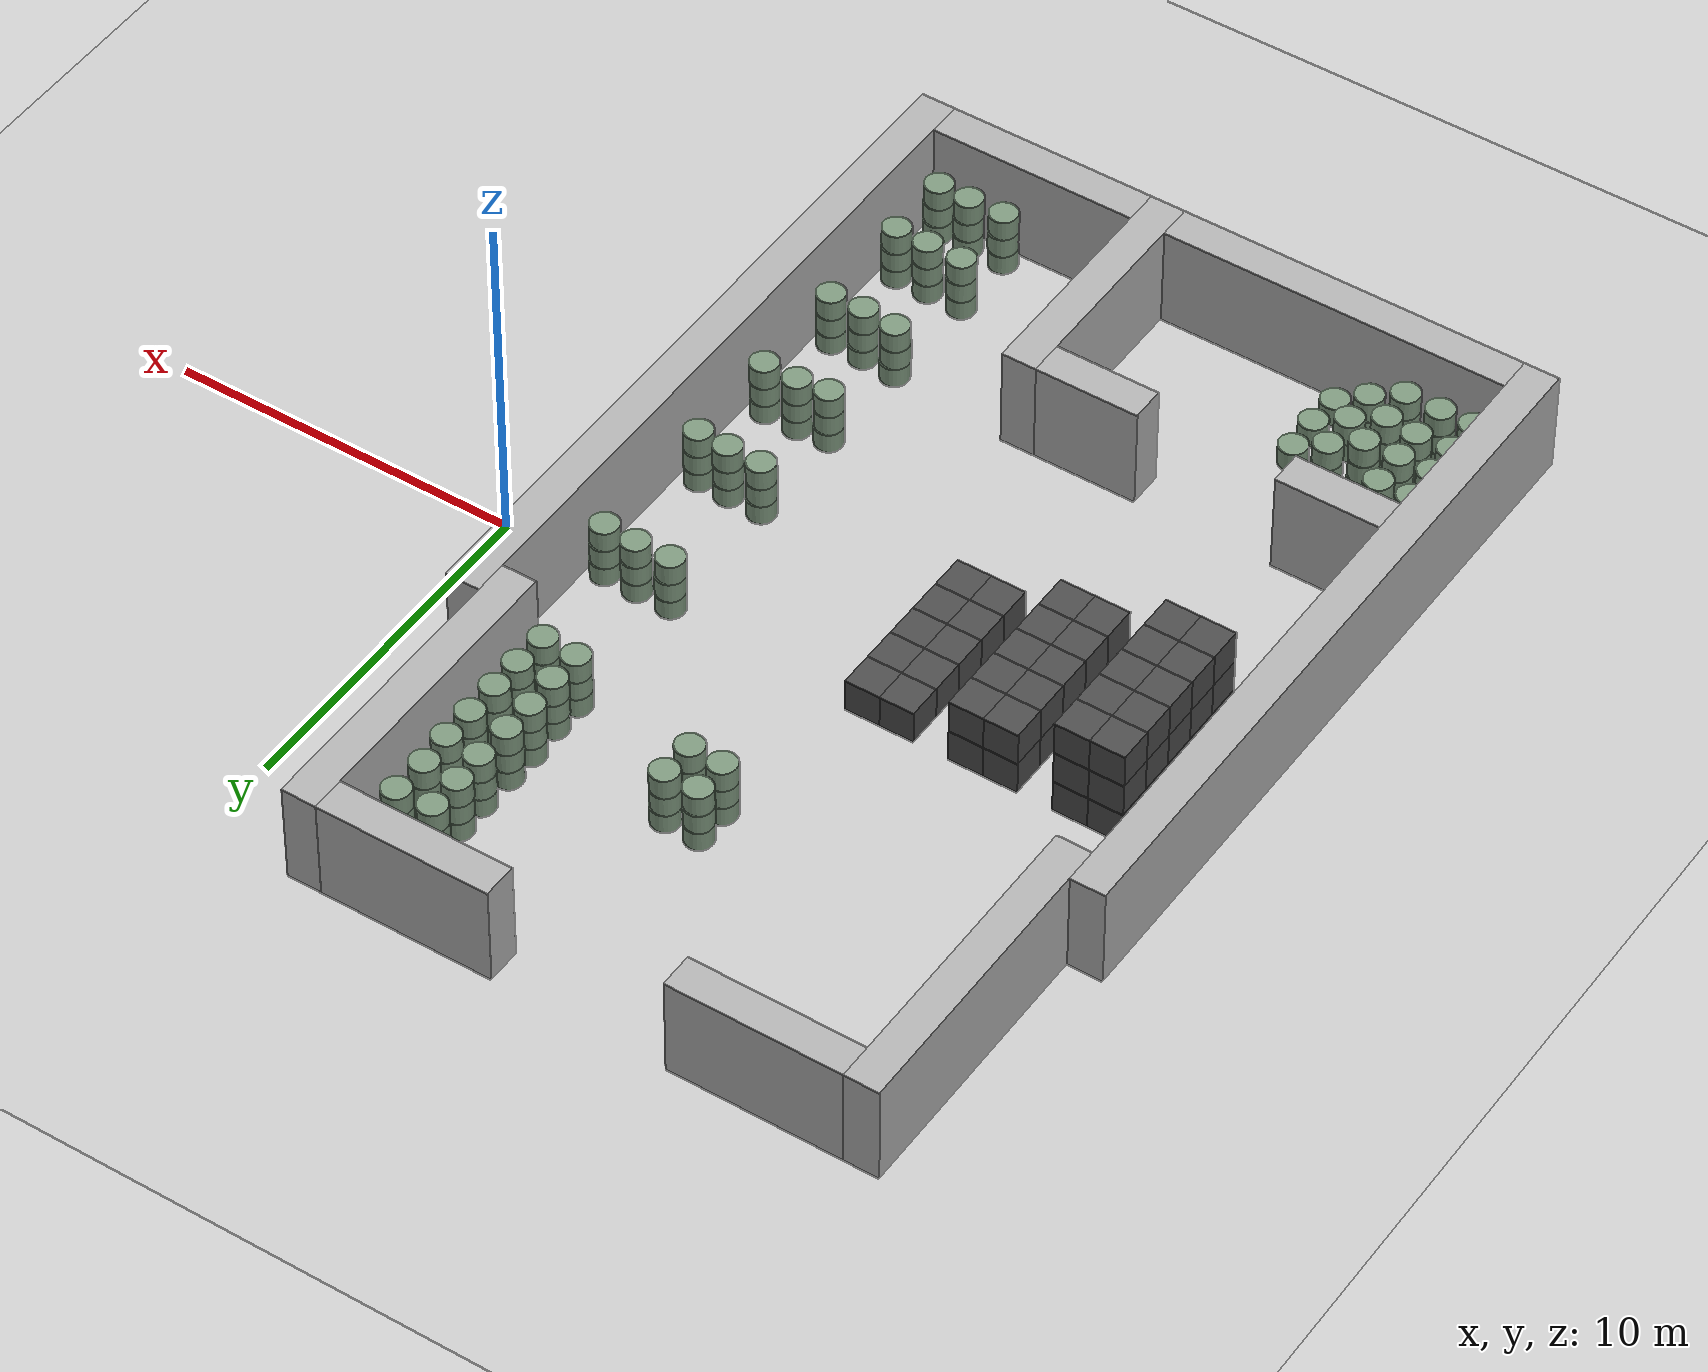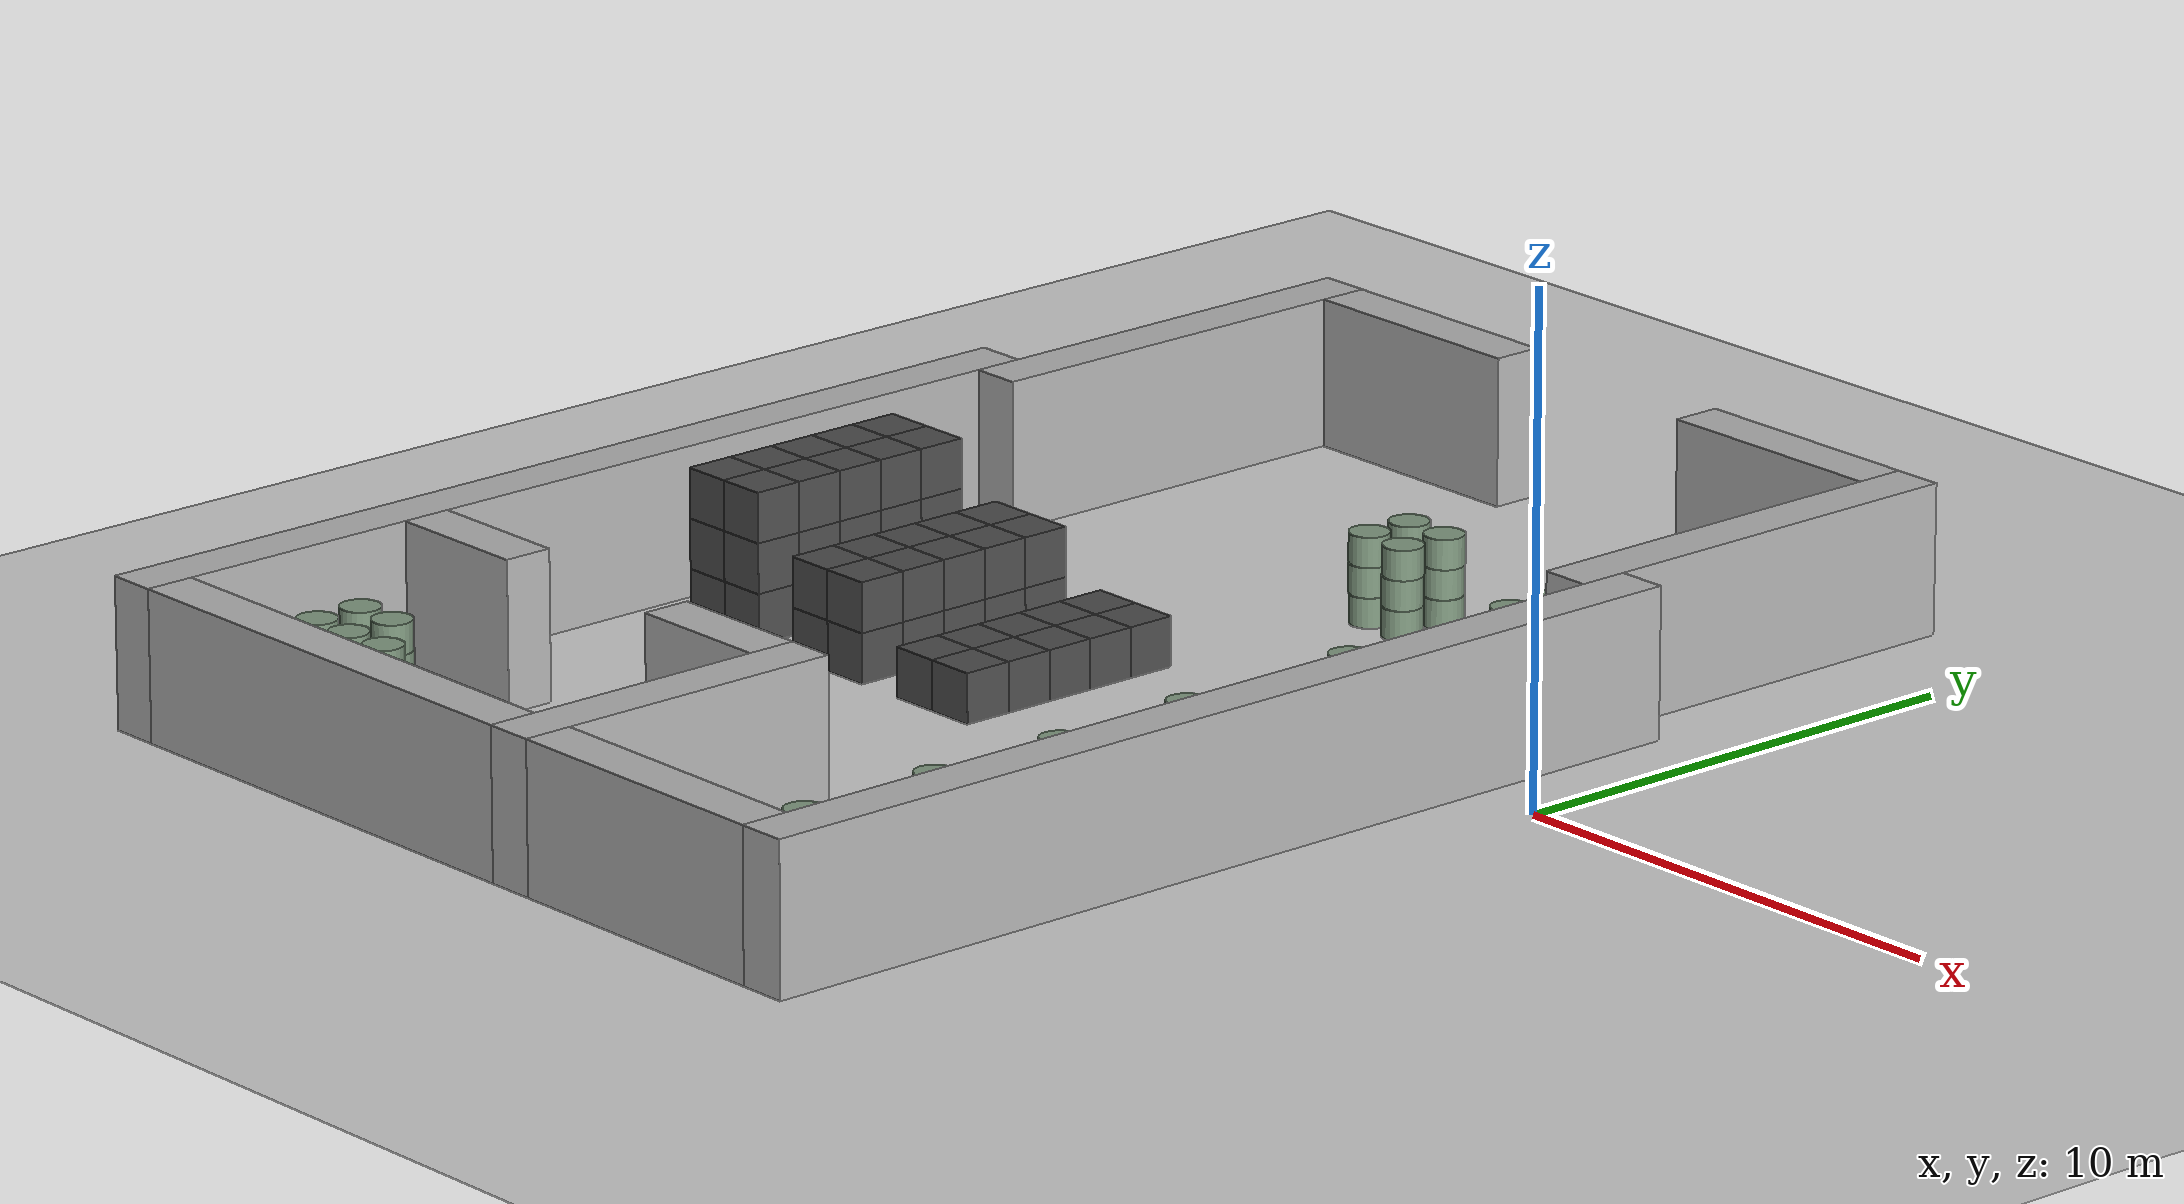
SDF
<sdf version="1.6">
 <world name="default">
  <light name="sun" type="directional">
   <cast_shadows>0</cast_shadows>
   <pose>0 0 10 0 -0 0</pose>
   <diffuse>0.8 0.8 0.8 1</diffuse>
   <specular>0.2 0.2 0.2 1</specular>
   <attenuation>
    <range>1000</range>
    <constant>0.9</constant>
    <linear>0.01</linear>
    <quadratic>0.001</quadratic>
   </attenuation>
   <direction>-0.5 0.1 -0.9</direction>
  </light>
  <include><uri>model://ground_plane</uri></include>
  <gravity>0 0 -9.8</gravity>
  <magnetic_field>6e-06 2.3e-05 -4.2e-05</magnetic_field>
  <atmosphere type="adiabatic"/>
  <physics name="default_physics" default="0" type="ode">
   <max_step_size>0.001</max_step_size>
   <real_time_factor>1</real_time_factor>
   <real_time_update_rate>1000</real_time_update_rate>
  </physics>
  <scene><ambient>0.4 0.4 0.4 1</ambient><background>0.7 0.7 0.7 1</background><shadows>0</shadows></scene>
  <spherical_coordinates>
   <surface_model>EARTH_WGS84</surface_model>
   <latitude_deg>0</latitude_deg>
   <longitude_deg>0</longitude_deg>
   <elevation>0</elevation>
   <heading_deg>0</heading_deg>
  </spherical_coordinates>
  <model name="wall_0">
   <pose>-20.0 -6.0 1.5 0 -0 0</pose>
   <static>True</static>
   <link name="link">
    <inertial>
     <mass>100</mass>
     <inertia>
      <ixx>0.166667</ixx>
      <ixy>0</ixy>
      <ixz>0</ixz>
      <iyy>0.166667</iyy>
      <iyz>0</iyz>
      <izz>0.166667</izz>
     </inertia>
    </inertial>
    <collision name="collision"><geometry><box><size>1.0 21.0 3.0</size></box></geometry></collision>
    <visual name="visual">
     <geometry><box><size>1.0 21.0 3.0</size></box></geometry>
     <material><ambient>0.7 0.7 0.7 1</ambient><diffuse>0.7 0.7 0.7 1</diffuse></material>
    </visual>
   </link>
  </model>
  <model name="wall_1">
   <pose>-19.0 8.0 1.5 0 -0 0</pose>
   <static>True</static>
   <link name="link">
    <inertial>
     <mass>100</mass>
     <inertia>
      <ixx>0.166667</ixx>
      <ixy>0</ixy>
      <ixz>0</ixz>
      <iyy>0.166667</iyy>
      <iyz>0</iyz>
      <izz>0.166667</izz>
     </inertia>
    </inertial>
    <collision name="collision"><geometry><box><size>1.0 9.0 3.0</size></box></geometry></collision>
    <visual name="visual">
     <geometry><box><size>1.0 9.0 3.0</size></box></geometry>
     <material><ambient>0.7 0.7 0.7 1</ambient><diffuse>0.7 0.7 0.7 1</diffuse></material>
    </visual>
   </link>
  </model>
  <model name="wall_2">
   <pose>-9.0 -13.0 1.5 0 -0 0</pose>
   <static>True</static>
   <link name="link">
    <inertial>
     <mass>100</mass>
     <inertia>
      <ixx>0.166667</ixx>
      <ixy>0</ixy>
      <ixz>0</ixz>
      <iyy>0.166667</iyy>
      <iyz>0</iyz>
      <izz>0.166667</izz>
     </inertia>
    </inertial>
    <collision name="collision"><geometry><box><size>1.0 7.0 3.0</size></box></geometry></collision>
    <visual name="visual">
     <geometry><box><size>1.0 7.0 3.0</size></box></geometry>
     <material><ambient>0.7 0.7 0.7 1</ambient><diffuse>0.7 0.7 0.7 1</diffuse></material>
    </visual>
   </link>
  </model>
  <model name="wall_3">
   <pose>-3.0 8.0 1.5 0 -0 0</pose>
   <static>True</static>
   <link name="link">
    <inertial>
     <mass>100</mass>
     <inertia>
      <ixx>0.166667</ixx>
      <ixy>0</ixy>
      <ixz>0</ixz>
      <iyy>0.166667</iyy>
      <iyz>0</iyz>
      <izz>0.166667</izz>
     </inertia>
    </inertial>
    <collision name="collision"><geometry><box><size>1.0 9.0 3.0</size></box></geometry></collision>
    <visual name="visual">
     <geometry><box><size>1.0 9.0 3.0</size></box></geometry>
     <material><ambient>0.7 0.7 0.7 1</ambient><diffuse>0.7 0.7 0.7 1</diffuse></material>
    </visual>
   </link>
  </model>
  <model name="wall_4">
   <pose>-2.0 -6.0 1.5 0 -0 0</pose>
   <static>True</static>
   <link name="link">
    <inertial>
     <mass>100</mass>
     <inertia>
      <ixx>0.166667</ixx>
      <ixy>0</ixy>
      <ixz>0</ixz>
      <iyy>0.166667</iyy>
      <iyz>0</iyz>
      <izz>0.166667</izz>
     </inertia>
    </inertial>
    <collision name="collision"><geometry><box><size>1.0 21.0 3.0</size></box></geometry></collision>
    <visual name="visual">
     <geometry><box><size>1.0 21.0 3.0</size></box></geometry>
     <material><ambient>0.7 0.7 0.7 1</ambient><diffuse>0.7 0.7 0.7 1</diffuse></material>
    </visual>
   </link>
  </model>
  <model name="wall_5">
   <pose>-14.5 -16.0 1.5 0 -0 0</pose>
   <static>True</static>
   <link name="link">
    <inertial>
     <mass>100</mass>
     <inertia>
      <ixx>0.166667</ixx>
      <ixy>0</ixy>
      <ixz>0</ixz>
      <iyy>0.166667</iyy>
      <iyz>0</iyz>
      <izz>0.166667</izz>
     </inertia>
    </inertial>
    <collision name="collision"><geometry><box><size>10.0 1.0 3.0</size></box></geometry></collision>
    <visual name="visual">
     <geometry><box><size>10.0 1.0 3.0</size></box></geometry>
     <material><ambient>0.7 0.7 0.7 1</ambient><diffuse>0.7 0.7 0.7 1</diffuse></material>
    </visual>
   </link>
  </model>
  <model name="wall_6">
   <pose>-5.5 -16.0 1.5 0 -0 0</pose>
   <static>True</static>
   <link name="link">
    <inertial>
     <mass>100</mass>
     <inertia>
      <ixx>0.166667</ixx>
      <ixy>0</ixy>
      <ixz>0</ixz>
      <iyy>0.166667</iyy>
      <iyz>0</iyz>
      <izz>0.166667</izz>
     </inertia>
    </inertial>
    <collision name="collision"><geometry><box><size>6.0 1.0 3.0</size></box></geometry></collision>
    <visual name="visual">
     <geometry><box><size>6.0 1.0 3.0</size></box></geometry>
     <material><ambient>0.7 0.7 0.7 1</ambient><diffuse>0.7 0.7 0.7 1</diffuse></material>
    </visual>
   </link>
  </model>
  <model name="wall_7">
   <pose>-18.0 -10.0 1.5 0 -0 0</pose>
   <static>True</static>
   <link name="link">
    <inertial>
     <mass>100</mass>
     <inertia>
      <ixx>0.166667</ixx>
      <ixy>0</ixy>
      <ixz>0</ixz>
      <iyy>0.166667</iyy>
      <iyz>0</iyz>
      <izz>0.166667</izz>
     </inertia>
    </inertial>
    <collision name="collision"><geometry><box><size>3.0 1.0 3.0</size></box></geometry></collision>
    <visual name="visual">
     <geometry><box><size>3.0 1.0 3.0</size></box></geometry>
     <material><ambient>0.7 0.7 0.7 1</ambient><diffuse>0.7 0.7 0.7 1</diffuse></material>
    </visual>
   </link>
  </model>
  <model name="wall_8">
   <pose>-11.0 -10.0 1.5 0 -0 0</pose>
   <static>True</static>
   <link name="link">
    <inertial>
     <mass>100</mass>
     <inertia>
      <ixx>0.166667</ixx>
      <ixy>0</ixy>
      <ixz>0</ixz>
      <iyy>0.166667</iyy>
      <iyz>0</iyz>
      <izz>0.166667</izz>
     </inertia>
    </inertial>
    <collision name="collision"><geometry><box><size>3.0 1.0 3.0</size></box></geometry></collision>
    <visual name="visual">
     <geometry><box><size>3.0 1.0 3.0</size></box></geometry>
     <material><ambient>0.7 0.7 0.7 1</ambient><diffuse>0.7 0.7 0.7 1</diffuse></material>
    </visual>
   </link>
  </model>
  <model name="wall_9">
   <pose>-16.0 12.0 1.5 0 -0 0</pose>
   <static>True</static>
   <link name="link">
    <inertial>
     <mass>100</mass>
     <inertia>
      <ixx>0.166667</ixx>
      <ixy>0</ixy>
      <ixz>0</ixz>
      <iyy>0.166667</iyy>
      <iyz>0</iyz>
      <izz>0.166667</izz>
     </inertia>
    </inertial>
    <collision name="collision"><geometry><box><size>5.0 1.0 3.0</size></box></geometry></collision>
    <visual name="visual">
     <geometry><box><size>5.0 1.0 3.0</size></box></geometry>
     <material><ambient>0.7 0.7 0.7 1</ambient><diffuse>0.7 0.7 0.7 1</diffuse></material>
    </visual>
   </link>
  </model>
  <model name="wall_10">
   <pose>-6.0 12.0 1.5 0 -0 0</pose>
   <static>True</static>
   <link name="link">
    <inertial>
     <mass>100</mass>
     <inertia>
      <ixx>0.166667</ixx>
      <ixy>0</ixy>
      <ixz>0</ixz>
      <iyy>0.166667</iyy>
      <iyz>0</iyz>
      <izz>0.166667</izz>
     </inertia>
    </inertial>
    <collision name="collision"><geometry><box><size>5.0 1.0 3.0</size></box></geometry></collision>
    <visual name="visual">
     <geometry><box><size>5.0 1.0 3.0</size></box></geometry>
     <material><ambient>0.7 0.7 0.7 1</ambient><diffuse>0.7 0.7 0.7 1</diffuse></material>
    </visual>
   </link>
  </model>
  <model name="unit_box_0">
   <pose>-18.0 -4.0 0.5 0 -0 0</pose>
   <static>True</static>
   <link name="link">
    <inertial>
     <mass>100</mass>
     <inertia>
      <ixx>0.166667</ixx>
      <ixy>0</ixy>
      <ixz>0</ixz>
      <iyy>0.166667</iyy>
      <iyz>0</iyz>
      <izz>0.166667</izz>
     </inertia>
    </inertial>
    <collision name="collision"><geometry><box><size>1.0 1.0 1.0</size></box></geometry></collision>
    <visual name="visual">
     <geometry><box><size>1.0 1.0 1.0</size></box></geometry>
     <material><ambient>0.3 0.3 0.3 1</ambient><diffuse>0.3 0.3 0.3 1</diffuse></material>
    </visual>
   </link>
  </model>
  <model name="unit_box_1">
   <pose>-18.0 -4.0 1.5 0 -0 0</pose>
   <static>True</static>
   <link name="link">
    <inertial>
     <mass>100</mass>
     <inertia>
      <ixx>0.166667</ixx>
      <ixy>0</ixy>
      <ixz>0</ixz>
      <iyy>0.166667</iyy>
      <iyz>0</iyz>
      <izz>0.166667</izz>
     </inertia>
    </inertial>
    <collision name="collision"><geometry><box><size>1.0 1.0 1.0</size></box></geometry></collision>
    <visual name="visual">
     <geometry><box><size>1.0 1.0 1.0</size></box></geometry>
     <material><ambient>0.3 0.3 0.3 1</ambient><diffuse>0.3 0.3 0.3 1</diffuse></material>
    </visual>
   </link>
  </model>
  <model name="unit_box_2">
   <pose>-18.0 -4.0 2.5 0 -0 0</pose>
   <static>True</static>
   <link name="link">
    <inertial>
     <mass>100</mass>
     <inertia>
      <ixx>0.166667</ixx>
      <ixy>0</ixy>
      <ixz>0</ixz>
      <iyy>0.166667</iyy>
      <iyz>0</iyz>
      <izz>0.166667</izz>
     </inertia>
    </inertial>
    <collision name="collision"><geometry><box><size>1.0 1.0 1.0</size></box></geometry></collision>
    <visual name="visual">
     <geometry><box><size>1.0 1.0 1.0</size></box></geometry>
     <material><ambient>0.3 0.3 0.3 1</ambient><diffuse>0.3 0.3 0.3 1</diffuse></material>
    </visual>
   </link>
  </model>
  <model name="unit_box_3">
   <pose>-18.0 -3.0 0.5 0 -0 0</pose>
   <static>True</static>
   <link name="link">
    <inertial>
     <mass>100</mass>
     <inertia>
      <ixx>0.166667</ixx>
      <ixy>0</ixy>
      <ixz>0</ixz>
      <iyy>0.166667</iyy>
      <iyz>0</iyz>
      <izz>0.166667</izz>
     </inertia>
    </inertial>
    <collision name="collision"><geometry><box><size>1.0 1.0 1.0</size></box></geometry></collision>
    <visual name="visual">
     <geometry><box><size>1.0 1.0 1.0</size></box></geometry>
     <material><ambient>0.3 0.3 0.3 1</ambient><diffuse>0.3 0.3 0.3 1</diffuse></material>
    </visual>
   </link>
  </model>
  <model name="unit_box_4">
   <pose>-18.0 -3.0 1.5 0 -0 0</pose>
   <static>True</static>
   <link name="link">
    <inertial>
     <mass>100</mass>
     <inertia>
      <ixx>0.166667</ixx>
      <ixy>0</ixy>
      <ixz>0</ixz>
      <iyy>0.166667</iyy>
      <iyz>0</iyz>
      <izz>0.166667</izz>
     </inertia>
    </inertial>
    <collision name="collision"><geometry><box><size>1.0 1.0 1.0</size></box></geometry></collision>
    <visual name="visual">
     <geometry><box><size>1.0 1.0 1.0</size></box></geometry>
     <material><ambient>0.3 0.3 0.3 1</ambient><diffuse>0.3 0.3 0.3 1</diffuse></material>
    </visual>
   </link>
  </model>
  <model name="unit_box_5">
   <pose>-18.0 -3.0 2.5 0 -0 0</pose>
   <static>True</static>
   <link name="link">
    <inertial>
     <mass>100</mass>
     <inertia>
      <ixx>0.166667</ixx>
      <ixy>0</ixy>
      <ixz>0</ixz>
      <iyy>0.166667</iyy>
      <iyz>0</iyz>
      <izz>0.166667</izz>
     </inertia>
    </inertial>
    <collision name="collision"><geometry><box><size>1.0 1.0 1.0</size></box></geometry></collision>
    <visual name="visual">
     <geometry><box><size>1.0 1.0 1.0</size></box></geometry>
     <material><ambient>0.3 0.3 0.3 1</ambient><diffuse>0.3 0.3 0.3 1</diffuse></material>
    </visual>
   </link>
  </model>
  <model name="unit_box_6">
   <pose>-18.0 -2.0 0.5 0 -0 0</pose>
   <static>True</static>
   <link name="link">
    <inertial>
     <mass>100</mass>
     <inertia>
      <ixx>0.166667</ixx>
      <ixy>0</ixy>
      <ixz>0</ixz>
      <iyy>0.166667</iyy>
      <iyz>0</iyz>
      <izz>0.166667</izz>
     </inertia>
    </inertial>
    <collision name="collision"><geometry><box><size>1.0 1.0 1.0</size></box></geometry></collision>
    <visual name="visual">
     <geometry><box><size>1.0 1.0 1.0</size></box></geometry>
     <material><ambient>0.3 0.3 0.3 1</ambient><diffuse>0.3 0.3 0.3 1</diffuse></material>
    </visual>
   </link>
  </model>
  <model name="unit_box_7">
   <pose>-18.0 -2.0 1.5 0 -0 0</pose>
   <static>True</static>
   <link name="link">
    <inertial>
     <mass>100</mass>
     <inertia>
      <ixx>0.166667</ixx>
      <ixy>0</ixy>
      <ixz>0</ixz>
      <iyy>0.166667</iyy>
      <iyz>0</iyz>
      <izz>0.166667</izz>
     </inertia>
    </inertial>
    <collision name="collision"><geometry><box><size>1.0 1.0 1.0</size></box></geometry></collision>
    <visual name="visual">
     <geometry><box><size>1.0 1.0 1.0</size></box></geometry>
     <material><ambient>0.3 0.3 0.3 1</ambient><diffuse>0.3 0.3 0.3 1</diffuse></material>
    </visual>
   </link>
  </model>
  <model name="unit_box_8">
   <pose>-18.0 -2.0 2.5 0 -0 0</pose>
   <static>True</static>
   <link name="link">
    <inertial>
     <mass>100</mass>
     <inertia>
      <ixx>0.166667</ixx>
      <ixy>0</ixy>
      <ixz>0</ixz>
      <iyy>0.166667</iyy>
      <iyz>0</iyz>
      <izz>0.166667</izz>
     </inertia>
    </inertial>
    <collision name="collision"><geometry><box><size>1.0 1.0 1.0</size></box></geometry></collision>
    <visual name="visual">
     <geometry><box><size>1.0 1.0 1.0</size></box></geometry>
     <material><ambient>0.3 0.3 0.3 1</ambient><diffuse>0.3 0.3 0.3 1</diffuse></material>
    </visual>
   </link>
  </model>
  <model name="unit_box_9">
   <pose>-18.0 -1.0 0.5 0 -0 0</pose>
   <static>True</static>
   <link name="link">
    <inertial>
     <mass>100</mass>
     <inertia>
      <ixx>0.166667</ixx>
      <ixy>0</ixy>
      <ixz>0</ixz>
      <iyy>0.166667</iyy>
      <iyz>0</iyz>
      <izz>0.166667</izz>
     </inertia>
    </inertial>
    <collision name="collision"><geometry><box><size>1.0 1.0 1.0</size></box></geometry></collision>
    <visual name="visual">
     <geometry><box><size>1.0 1.0 1.0</size></box></geometry>
     <material><ambient>0.3 0.3 0.3 1</ambient><diffuse>0.3 0.3 0.3 1</diffuse></material>
    </visual>
   </link>
  </model>
  <model name="unit_box_10">
   <pose>-18.0 -1.0 1.5 0 -0 0</pose>
   <static>True</static>
   <link name="link">
    <inertial>
     <mass>100</mass>
     <inertia>
      <ixx>0.166667</ixx>
      <ixy>0</ixy>
      <ixz>0</ixz>
      <iyy>0.166667</iyy>
      <iyz>0</iyz>
      <izz>0.166667</izz>
     </inertia>
    </inertial>
    <collision name="collision"><geometry><box><size>1.0 1.0 1.0</size></box></geometry></collision>
    <visual name="visual">
     <geometry><box><size>1.0 1.0 1.0</size></box></geometry>
     <material><ambient>0.3 0.3 0.3 1</ambient><diffuse>0.3 0.3 0.3 1</diffuse></material>
    </visual>
   </link>
  </model>
  <model name="unit_box_11">
   <pose>-18.0 -1.0 2.5 0 -0 0</pose>
   <static>True</static>
   <link name="link">
    <inertial>
     <mass>100</mass>
     <inertia>
      <ixx>0.166667</ixx>
      <ixy>0</ixy>
      <ixz>0</ixz>
      <iyy>0.166667</iyy>
      <iyz>0</iyz>
      <izz>0.166667</izz>
     </inertia>
    </inertial>
    <collision name="collision"><geometry><box><size>1.0 1.0 1.0</size></box></geometry></collision>
    <visual name="visual">
     <geometry><box><size>1.0 1.0 1.0</size></box></geometry>
     <material><ambient>0.3 0.3 0.3 1</ambient><diffuse>0.3 0.3 0.3 1</diffuse></material>
    </visual>
   </link>
  </model>
  <model name="unit_box_12">
   <pose>-18.0 0.0 0.5 0 -0 0</pose>
   <static>True</static>
   <link name="link">
    <inertial>
     <mass>100</mass>
     <inertia>
      <ixx>0.166667</ixx>
      <ixy>0</ixy>
      <ixz>0</ixz>
      <iyy>0.166667</iyy>
      <iyz>0</iyz>
      <izz>0.166667</izz>
     </inertia>
    </inertial>
    <collision name="collision"><geometry><box><size>1.0 1.0 1.0</size></box></geometry></collision>
    <visual name="visual">
     <geometry><box><size>1.0 1.0 1.0</size></box></geometry>
     <material><ambient>0.3 0.3 0.3 1</ambient><diffuse>0.3 0.3 0.3 1</diffuse></material>
    </visual>
   </link>
  </model>
  <model name="unit_box_13">
   <pose>-18.0 0.0 1.5 0 -0 0</pose>
   <static>True</static>
   <link name="link">
    <inertial>
     <mass>100</mass>
     <inertia>
      <ixx>0.166667</ixx>
      <ixy>0</ixy>
      <ixz>0</ixz>
      <iyy>0.166667</iyy>
      <iyz>0</iyz>
      <izz>0.166667</izz>
     </inertia>
    </inertial>
    <collision name="collision"><geometry><box><size>1.0 1.0 1.0</size></box></geometry></collision>
    <visual name="visual">
     <geometry><box><size>1.0 1.0 1.0</size></box></geometry>
     <material><ambient>0.3 0.3 0.3 1</ambient><diffuse>0.3 0.3 0.3 1</diffuse></material>
    </visual>
   </link>
  </model>
  <model name="unit_box_14">
   <pose>-18.0 0.0 2.5 0 -0 0</pose>
   <static>True</static>
   <link name="link">
    <inertial>
     <mass>100</mass>
     <inertia>
      <ixx>0.166667</ixx>
      <ixy>0</ixy>
      <ixz>0</ixz>
      <iyy>0.166667</iyy>
      <iyz>0</iyz>
      <izz>0.166667</izz>
     </inertia>
    </inertial>
    <collision name="collision"><geometry><box><size>1.0 1.0 1.0</size></box></geometry></collision>
    <visual name="visual">
     <geometry><box><size>1.0 1.0 1.0</size></box></geometry>
     <material><ambient>0.3 0.3 0.3 1</ambient><diffuse>0.3 0.3 0.3 1</diffuse></material>
    </visual>
   </link>
  </model>
  <model name="unit_box_15">
   <pose>-17.0 -4.0 0.5 0 -0 0</pose>
   <static>True</static>
   <link name="link">
    <inertial>
     <mass>100</mass>
     <inertia>
      <ixx>0.166667</ixx>
      <ixy>0</ixy>
      <ixz>0</ixz>
      <iyy>0.166667</iyy>
      <iyz>0</iyz>
      <izz>0.166667</izz>
     </inertia>
    </inertial>
    <collision name="collision"><geometry><box><size>1.0 1.0 1.0</size></box></geometry></collision>
    <visual name="visual">
     <geometry><box><size>1.0 1.0 1.0</size></box></geometry>
     <material><ambient>0.3 0.3 0.3 1</ambient><diffuse>0.3 0.3 0.3 1</diffuse></material>
    </visual>
   </link>
  </model>
  <model name="unit_box_16">
   <pose>-17.0 -4.0 1.5 0 -0 0</pose>
   <static>True</static>
   <link name="link">
    <inertial>
     <mass>100</mass>
     <inertia>
      <ixx>0.166667</ixx>
      <ixy>0</ixy>
      <ixz>0</ixz>
      <iyy>0.166667</iyy>
      <iyz>0</iyz>
      <izz>0.166667</izz>
     </inertia>
    </inertial>
    <collision name="collision"><geometry><box><size>1.0 1.0 1.0</size></box></geometry></collision>
    <visual name="visual">
     <geometry><box><size>1.0 1.0 1.0</size></box></geometry>
     <material><ambient>0.3 0.3 0.3 1</ambient><diffuse>0.3 0.3 0.3 1</diffuse></material>
    </visual>
   </link>
  </model>
  <model name="unit_box_17">
   <pose>-17.0 -4.0 2.5 0 -0 0</pose>
   <static>True</static>
   <link name="link">
    <inertial>
     <mass>100</mass>
     <inertia>
      <ixx>0.166667</ixx>
      <ixy>0</ixy>
      <ixz>0</ixz>
      <iyy>0.166667</iyy>
      <iyz>0</iyz>
      <izz>0.166667</izz>
     </inertia>
    </inertial>
    <collision name="collision"><geometry><box><size>1.0 1.0 1.0</size></box></geometry></collision>
    <visual name="visual">
     <geometry><box><size>1.0 1.0 1.0</size></box></geometry>
     <material><ambient>0.3 0.3 0.3 1</ambient><diffuse>0.3 0.3 0.3 1</diffuse></material>
    </visual>
   </link>
  </model>
  <model name="unit_box_18">
   <pose>-17.0 -3.0 0.5 0 -0 0</pose>
   <static>True</static>
   <link name="link">
    <inertial>
     <mass>100</mass>
     <inertia>
      <ixx>0.166667</ixx>
      <ixy>0</ixy>
      <ixz>0</ixz>
      <iyy>0.166667</iyy>
      <iyz>0</iyz>
      <izz>0.166667</izz>
     </inertia>
    </inertial>
    <collision name="collision"><geometry><box><size>1.0 1.0 1.0</size></box></geometry></collision>
    <visual name="visual">
     <geometry><box><size>1.0 1.0 1.0</size></box></geometry>
     <material><ambient>0.3 0.3 0.3 1</ambient><diffuse>0.3 0.3 0.3 1</diffuse></material>
    </visual>
   </link>
  </model>
  <model name="unit_box_19">
   <pose>-17.0 -3.0 1.5 0 -0 0</pose>
   <static>True</static>
   <link name="link">
    <inertial>
     <mass>100</mass>
     <inertia>
      <ixx>0.166667</ixx>
      <ixy>0</ixy>
      <ixz>0</ixz>
      <iyy>0.166667</iyy>
      <iyz>0</iyz>
      <izz>0.166667</izz>
     </inertia>
    </inertial>
    <collision name="collision"><geometry><box><size>1.0 1.0 1.0</size></box></geometry></collision>
    <visual name="visual">
     <geometry><box><size>1.0 1.0 1.0</size></box></geometry>
     <material><ambient>0.3 0.3 0.3 1</ambient><diffuse>0.3 0.3 0.3 1</diffuse></material>
    </visual>
   </link>
  </model>
  <model name="unit_box_20">
   <pose>-17.0 -3.0 2.5 0 -0 0</pose>
   <static>True</static>
   <link name="link">
    <inertial>
     <mass>100</mass>
     <inertia>
      <ixx>0.166667</ixx>
      <ixy>0</ixy>
      <ixz>0</ixz>
      <iyy>0.166667</iyy>
      <iyz>0</iyz>
      <izz>0.166667</izz>
     </inertia>
    </inertial>
    <collision name="collision"><geometry><box><size>1.0 1.0 1.0</size></box></geometry></collision>
    <visual name="visual">
     <geometry><box><size>1.0 1.0 1.0</size></box></geometry>
     <material><ambient>0.3 0.3 0.3 1</ambient><diffuse>0.3 0.3 0.3 1</diffuse></material>
    </visual>
   </link>
  </model>
  <model name="unit_box_21">
   <pose>-17.0 -2.0 0.5 0 -0 0</pose>
   <static>True</static>
   <link name="link">
    <inertial>
     <mass>100</mass>
     <inertia>
      <ixx>0.166667</ixx>
      <ixy>0</ixy>
      <ixz>0</ixz>
      <iyy>0.166667</iyy>
      <iyz>0</iyz>
      <izz>0.166667</izz>
     </inertia>
    </inertial>
    <collision name="collision"><geometry><box><size>1.0 1.0 1.0</size></box></geometry></collision>
    <visual name="visual">
     <geometry><box><size>1.0 1.0 1.0</size></box></geometry>
     <material><ambient>0.3 0.3 0.3 1</ambient><diffuse>0.3 0.3 0.3 1</diffuse></material>
    </visual>
   </link>
  </model>
  <model name="unit_box_22">
   <pose>-17.0 -2.0 1.5 0 -0 0</pose>
   <static>True</static>
   <link name="link">
    <inertial>
     <mass>100</mass>
     <inertia>
      <ixx>0.166667</ixx>
      <ixy>0</ixy>
      <ixz>0</ixz>
      <iyy>0.166667</iyy>
      <iyz>0</iyz>
      <izz>0.166667</izz>
     </inertia>
    </inertial>
    <collision name="collision"><geometry><box><size>1.0 1.0 1.0</size></box></geometry></collision>
    <visual name="visual">
     <geometry><box><size>1.0 1.0 1.0</size></box></geometry>
     <material><ambient>0.3 0.3 0.3 1</ambient><diffuse>0.3 0.3 0.3 1</diffuse></material>
    </visual>
   </link>
  </model>
  <model name="unit_box_23">
   <pose>-17.0 -2.0 2.5 0 -0 0</pose>
   <static>True</static>
   <link name="link">
    <inertial>
     <mass>100</mass>
     <inertia>
      <ixx>0.166667</ixx>
      <ixy>0</ixy>
      <ixz>0</ixz>
      <iyy>0.166667</iyy>
      <iyz>0</iyz>
      <izz>0.166667</izz>
     </inertia>
    </inertial>
    <collision name="collision"><geometry><box><size>1.0 1.0 1.0</size></box></geometry></collision>
    <visual name="visual">
     <geometry><box><size>1.0 1.0 1.0</size></box></geometry>
     <material><ambient>0.3 0.3 0.3 1</ambient><diffuse>0.3 0.3 0.3 1</diffuse></material>
    </visual>
   </link>
  </model>
  <model name="unit_box_24">
   <pose>-17.0 -1.0 0.5 0 -0 0</pose>
   <static>True</static>
   <link name="link">
    <inertial>
     <mass>100</mass>
     <inertia>
      <ixx>0.166667</ixx>
      <ixy>0</ixy>
      <ixz>0</ixz>
      <iyy>0.166667</iyy>
      <iyz>0</iyz>
      <izz>0.166667</izz>
     </inertia>
    </inertial>
    <collision name="collision"><geometry><box><size>1.0 1.0 1.0</size></box></geometry></collision>
    <visual name="visual">
     <geometry><box><size>1.0 1.0 1.0</size></box></geometry>
     <material><ambient>0.3 0.3 0.3 1</ambient><diffuse>0.3 0.3 0.3 1</diffuse></material>
    </visual>
   </link>
  </model>
  <model name="unit_box_25">
   <pose>-17.0 -1.0 1.5 0 -0 0</pose>
   <static>True</static>
   <link name="link">
    <inertial>
     <mass>100</mass>
     <inertia>
      <ixx>0.166667</ixx>
      <ixy>0</ixy>
      <ixz>0</ixz>
      <iyy>0.166667</iyy>
      <iyz>0</iyz>
      <izz>0.166667</izz>
     </inertia>
    </inertial>
    <collision name="collision"><geometry><box><size>1.0 1.0 1.0</size></box></geometry></collision>
    <visual name="visual">
     <geometry><box><size>1.0 1.0 1.0</size></box></geometry>
     <material><ambient>0.3 0.3 0.3 1</ambient><diffuse>0.3 0.3 0.3 1</diffuse></material>
    </visual>
   </link>
  </model>
  <model name="unit_box_26">
   <pose>-17.0 -1.0 2.5 0 -0 0</pose>
   <static>True</static>
   <link name="link">
    <inertial>
     <mass>100</mass>
     <inertia>
      <ixx>0.166667</ixx>
      <ixy>0</ixy>
      <ixz>0</ixz>
      <iyy>0.166667</iyy>
      <iyz>0</iyz>
      <izz>0.166667</izz>
     </inertia>
    </inertial>
    <collision name="collision"><geometry><box><size>1.0 1.0 1.0</size></box></geometry></collision>
    <visual name="visual">
     <geometry><box><size>1.0 1.0 1.0</size></box></geometry>
     <material><ambient>0.3 0.3 0.3 1</ambient><diffuse>0.3 0.3 0.3 1</diffuse></material>
    </visual>
   </link>
  </model>
  <model name="unit_box_27">
   <pose>-17.0 0.0 0.5 0 -0 0</pose>
   <static>True</static>
   <link name="link">
    <inertial>
     <mass>100</mass>
     <inertia>
      <ixx>0.166667</ixx>
      <ixy>0</ixy>
      <ixz>0</ixz>
      <iyy>0.166667</iyy>
      <iyz>0</iyz>
      <izz>0.166667</izz>
     </inertia>
    </inertial>
    <collision name="collision"><geometry><box><size>1.0 1.0 1.0</size></box></geometry></collision>
    <visual name="visual">
     <geometry><box><size>1.0 1.0 1.0</size></box></geometry>
     <material><ambient>0.3 0.3 0.3 1</ambient><diffuse>0.3 0.3 0.3 1</diffuse></material>
    </visual>
   </link>
  </model>
  <model name="unit_box_28">
   <pose>-17.0 0.0 1.5 0 -0 0</pose>
   <static>True</static>
   <link name="link">
    <inertial>
     <mass>100</mass>
     <inertia>
      <ixx>0.166667</ixx>
      <ixy>0</ixy>
      <ixz>0</ixz>
      <iyy>0.166667</iyy>
      <iyz>0</iyz>
      <izz>0.166667</izz>
     </inertia>
    </inertial>
    <collision name="collision"><geometry><box><size>1.0 1.0 1.0</size></box></geometry></collision>
    <visual name="visual">
     <geometry><box><size>1.0 1.0 1.0</size></box></geometry>
     <material><ambient>0.3 0.3 0.3 1</ambient><diffuse>0.3 0.3 0.3 1</diffuse></material>
    </visual>
   </link>
  </model>
  <model name="unit_box_29">
   <pose>-17.0 0.0 2.5 0 -0 0</pose>
   <static>True</static>
   <link name="link">
    <inertial>
     <mass>100</mass>
     <inertia>
      <ixx>0.166667</ixx>
      <ixy>0</ixy>
      <ixz>0</ixz>
      <iyy>0.166667</iyy>
      <iyz>0</iyz>
      <izz>0.166667</izz>
     </inertia>
    </inertial>
    <collision name="collision"><geometry><box><size>1.0 1.0 1.0</size></box></geometry></collision>
    <visual name="visual">
     <geometry><box><size>1.0 1.0 1.0</size></box></geometry>
     <material><ambient>0.3 0.3 0.3 1</ambient><diffuse>0.3 0.3 0.3 1</diffuse></material>
    </visual>
   </link>
  </model>
  <model name="unit_box_30">
   <pose>-15.0 -4.0 0.5 0 -0 0</pose>
   <static>True</static>
   <link name="link">
    <inertial>
     <mass>100</mass>
     <inertia>
      <ixx>0.166667</ixx>
      <ixy>0</ixy>
      <ixz>0</ixz>
      <iyy>0.166667</iyy>
      <iyz>0</iyz>
      <izz>0.166667</izz>
     </inertia>
    </inertial>
    <collision name="collision"><geometry><box><size>1.0 1.0 1.0</size></box></geometry></collision>
    <visual name="visual">
     <geometry><box><size>1.0 1.0 1.0</size></box></geometry>
     <material><ambient>0.3 0.3 0.3 1</ambient><diffuse>0.3 0.3 0.3 1</diffuse></material>
    </visual>
   </link>
  </model>
  <model name="unit_box_31">
   <pose>-15.0 -4.0 1.5 0 -0 0</pose>
   <static>True</static>
   <link name="link">
    <inertial>
     <mass>100</mass>
     <inertia>
      <ixx>0.166667</ixx>
      <ixy>0</ixy>
      <ixz>0</ixz>
      <iyy>0.166667</iyy>
      <iyz>0</iyz>
      <izz>0.166667</izz>
     </inertia>
    </inertial>
    <collision name="collision"><geometry><box><size>1.0 1.0 1.0</size></box></geometry></collision>
    <visual name="visual">
     <geometry><box><size>1.0 1.0 1.0</size></box></geometry>
     <material><ambient>0.3 0.3 0.3 1</ambient><diffuse>0.3 0.3 0.3 1</diffuse></material>
    </visual>
   </link>
  </model>
  <model name="unit_box_32">
   <pose>-15.0 -3.0 0.5 0 -0 0</pose>
   <static>True</static>
   <link name="link">
    <inertial>
     <mass>100</mass>
     <inertia>
      <ixx>0.166667</ixx>
      <ixy>0</ixy>
      <ixz>0</ixz>
      <iyy>0.166667</iyy>
      <iyz>0</iyz>
      <izz>0.166667</izz>
     </inertia>
    </inertial>
    <collision name="collision"><geometry><box><size>1.0 1.0 1.0</size></box></geometry></collision>
    <visual name="visual">
     <geometry><box><size>1.0 1.0 1.0</size></box></geometry>
     <material><ambient>0.3 0.3 0.3 1</ambient><diffuse>0.3 0.3 0.3 1</diffuse></material>
    </visual>
   </link>
  </model>
  <model name="unit_box_33">
   <pose>-15.0 -3.0 1.5 0 -0 0</pose>
   <static>True</static>
   <link name="link">
    <inertial>
     <mass>100</mass>
     <inertia>
      <ixx>0.166667</ixx>
      <ixy>0</ixy>
      <ixz>0</ixz>
      <iyy>0.166667</iyy>
      <iyz>0</iyz>
      <izz>0.166667</izz>
     </inertia>
    </inertial>
    <collision name="collision"><geometry><box><size>1.0 1.0 1.0</size></box></geometry></collision>
    <visual name="visual">
     <geometry><box><size>1.0 1.0 1.0</size></box></geometry>
     <material><ambient>0.3 0.3 0.3 1</ambient><diffuse>0.3 0.3 0.3 1</diffuse></material>
    </visual>
   </link>
  </model>
  <model name="unit_box_34">
   <pose>-15.0 -2.0 0.5 0 -0 0</pose>
   <static>True</static>
   <link name="link">
    <inertial>
     <mass>100</mass>
     <inertia>
      <ixx>0.166667</ixx>
      <ixy>0</ixy>
      <ixz>0</ixz>
      <iyy>0.166667</iyy>
      <iyz>0</iyz>
      <izz>0.166667</izz>
     </inertia>
    </inertial>
    <collision name="collision"><geometry><box><size>1.0 1.0 1.0</size></box></geometry></collision>
    <visual name="visual">
     <geometry><box><size>1.0 1.0 1.0</size></box></geometry>
     <material><ambient>0.3 0.3 0.3 1</ambient><diffuse>0.3 0.3 0.3 1</diffuse></material>
    </visual>
   </link>
  </model>
  <model name="unit_box_35">
   <pose>-15.0 -2.0 1.5 0 -0 0</pose>
   <static>True</static>
   <link name="link">
    <inertial>
     <mass>100</mass>
     <inertia>
      <ixx>0.166667</ixx>
      <ixy>0</ixy>
      <ixz>0</ixz>
      <iyy>0.166667</iyy>
      <iyz>0</iyz>
      <izz>0.166667</izz>
     </inertia>
    </inertial>
    <collision name="collision"><geometry><box><size>1.0 1.0 1.0</size></box></geometry></collision>
    <visual name="visual">
     <geometry><box><size>1.0 1.0 1.0</size></box></geometry>
     <material><ambient>0.3 0.3 0.3 1</ambient><diffuse>0.3 0.3 0.3 1</diffuse></material>
    </visual>
   </link>
  </model>
  <model name="unit_box_36">
   <pose>-15.0 -1.0 0.5 0 -0 0</pose>
   <static>True</static>
   <link name="link">
    <inertial>
     <mass>100</mass>
     <inertia>
      <ixx>0.166667</ixx>
      <ixy>0</ixy>
      <ixz>0</ixz>
      <iyy>0.166667</iyy>
      <iyz>0</iyz>
      <izz>0.166667</izz>
     </inertia>
    </inertial>
    <collision name="collision"><geometry><box><size>1.0 1.0 1.0</size></box></geometry></collision>
    <visual name="visual">
     <geometry><box><size>1.0 1.0 1.0</size></box></geometry>
     <material><ambient>0.3 0.3 0.3 1</ambient><diffuse>0.3 0.3 0.3 1</diffuse></material>
    </visual>
   </link>
  </model>
  <model name="unit_box_37">
   <pose>-15.0 -1.0 1.5 0 -0 0</pose>
   <static>True</static>
   <link name="link">
    <inertial>
     <mass>100</mass>
     <inertia>
      <ixx>0.166667</ixx>
      <ixy>0</ixy>
      <ixz>0</ixz>
      <iyy>0.166667</iyy>
      <iyz>0</iyz>
      <izz>0.166667</izz>
     </inertia>
    </inertial>
    <collision name="collision"><geometry><box><size>1.0 1.0 1.0</size></box></geometry></collision>
    <visual name="visual">
     <geometry><box><size>1.0 1.0 1.0</size></box></geometry>
     <material><ambient>0.3 0.3 0.3 1</ambient><diffuse>0.3 0.3 0.3 1</diffuse></material>
    </visual>
   </link>
  </model>
  <model name="unit_box_38">
   <pose>-15.0 0.0 0.5 0 -0 0</pose>
   <static>True</static>
   <link name="link">
    <inertial>
     <mass>100</mass>
     <inertia>
      <ixx>0.166667</ixx>
      <ixy>0</ixy>
      <ixz>0</ixz>
      <iyy>0.166667</iyy>
      <iyz>0</iyz>
      <izz>0.166667</izz>
     </inertia>
    </inertial>
    <collision name="collision"><geometry><box><size>1.0 1.0 1.0</size></box></geometry></collision>
    <visual name="visual">
     <geometry><box><size>1.0 1.0 1.0</size></box></geometry>
     <material><ambient>0.3 0.3 0.3 1</ambient><diffuse>0.3 0.3 0.3 1</diffuse></material>
    </visual>
   </link>
  </model>
  <model name="unit_box_39">
   <pose>-15.0 0.0 1.5 0 -0 0</pose>
   <static>True</static>
   <link name="link">
    <inertial>
     <mass>100</mass>
     <inertia>
      <ixx>0.166667</ixx>
      <ixy>0</ixy>
      <ixz>0</ixz>
      <iyy>0.166667</iyy>
      <iyz>0</iyz>
      <izz>0.166667</izz>
     </inertia>
    </inertial>
    <collision name="collision"><geometry><box><size>1.0 1.0 1.0</size></box></geometry></collision>
    <visual name="visual">
     <geometry><box><size>1.0 1.0 1.0</size></box></geometry>
     <material><ambient>0.3 0.3 0.3 1</ambient><diffuse>0.3 0.3 0.3 1</diffuse></material>
    </visual>
   </link>
  </model>
  <model name="unit_box_40">
   <pose>-14.0 -4.0 0.5 0 -0 0</pose>
   <static>True</static>
   <link name="link">
    <inertial>
     <mass>100</mass>
     <inertia>
      <ixx>0.166667</ixx>
      <ixy>0</ixy>
      <ixz>0</ixz>
      <iyy>0.166667</iyy>
      <iyz>0</iyz>
      <izz>0.166667</izz>
     </inertia>
    </inertial>
    <collision name="collision"><geometry><box><size>1.0 1.0 1.0</size></box></geometry></collision>
    <visual name="visual">
     <geometry><box><size>1.0 1.0 1.0</size></box></geometry>
     <material><ambient>0.3 0.3 0.3 1</ambient><diffuse>0.3 0.3 0.3 1</diffuse></material>
    </visual>
   </link>
  </model>
  <model name="unit_box_41">
   <pose>-14.0 -4.0 1.5 0 -0 0</pose>
   <static>True</static>
   <link name="link">
    <inertial>
     <mass>100</mass>
     <inertia>
      <ixx>0.166667</ixx>
      <ixy>0</ixy>
      <ixz>0</ixz>
      <iyy>0.166667</iyy>
      <iyz>0</iyz>
      <izz>0.166667</izz>
     </inertia>
    </inertial>
    <collision name="collision"><geometry><box><size>1.0 1.0 1.0</size></box></geometry></collision>
    <visual name="visual">
     <geometry><box><size>1.0 1.0 1.0</size></box></geometry>
     <material><ambient>0.3 0.3 0.3 1</ambient><diffuse>0.3 0.3 0.3 1</diffuse></material>
    </visual>
   </link>
  </model>
  <model name="unit_box_42">
   <pose>-14.0 -3.0 0.5 0 -0 0</pose>
   <static>True</static>
   <link name="link">
    <inertial>
     <mass>100</mass>
     <inertia>
      <ixx>0.166667</ixx>
      <ixy>0</ixy>
      <ixz>0</ixz>
      <iyy>0.166667</iyy>
      <iyz>0</iyz>
      <izz>0.166667</izz>
     </inertia>
    </inertial>
    <collision name="collision"><geometry><box><size>1.0 1.0 1.0</size></box></geometry></collision>
    <visual name="visual">
     <geometry><box><size>1.0 1.0 1.0</size></box></geometry>
     <material><ambient>0.3 0.3 0.3 1</ambient><diffuse>0.3 0.3 0.3 1</diffuse></material>
    </visual>
   </link>
  </model>
  <model name="unit_box_43">
   <pose>-14.0 -3.0 1.5 0 -0 0</pose>
   <static>True</static>
   <link name="link">
    <inertial>
     <mass>100</mass>
     <inertia>
      <ixx>0.166667</ixx>
      <ixy>0</ixy>
      <ixz>0</ixz>
      <iyy>0.166667</iyy>
      <iyz>0</iyz>
      <izz>0.166667</izz>
     </inertia>
    </inertial>
    <collision name="collision"><geometry><box><size>1.0 1.0 1.0</size></box></geometry></collision>
    <visual name="visual">
     <geometry><box><size>1.0 1.0 1.0</size></box></geometry>
     <material><ambient>0.3 0.3 0.3 1</ambient><diffuse>0.3 0.3 0.3 1</diffuse></material>
    </visual>
   </link>
  </model>
  <model name="unit_box_44">
   <pose>-14.0 -2.0 0.5 0 -0 0</pose>
   <static>True</static>
   <link name="link">
    <inertial>
     <mass>100</mass>
     <inertia>
      <ixx>0.166667</ixx>
      <ixy>0</ixy>
      <ixz>0</ixz>
      <iyy>0.166667</iyy>
      <iyz>0</iyz>
      <izz>0.166667</izz>
     </inertia>
    </inertial>
    <collision name="collision"><geometry><box><size>1.0 1.0 1.0</size></box></geometry></collision>
    <visual name="visual">
     <geometry><box><size>1.0 1.0 1.0</size></box></geometry>
     <material><ambient>0.3 0.3 0.3 1</ambient><diffuse>0.3 0.3 0.3 1</diffuse></material>
    </visual>
   </link>
  </model>
  <model name="unit_box_45">
   <pose>-14.0 -2.0 1.5 0 -0 0</pose>
   <static>True</static>
   <link name="link">
    <inertial>
     <mass>100</mass>
     <inertia>
      <ixx>0.166667</ixx>
      <ixy>0</ixy>
      <ixz>0</ixz>
      <iyy>0.166667</iyy>
      <iyz>0</iyz>
      <izz>0.166667</izz>
     </inertia>
    </inertial>
    <collision name="collision"><geometry><box><size>1.0 1.0 1.0</size></box></geometry></collision>
    <visual name="visual">
     <geometry><box><size>1.0 1.0 1.0</size></box></geometry>
     <material><ambient>0.3 0.3 0.3 1</ambient><diffuse>0.3 0.3 0.3 1</diffuse></material>
    </visual>
   </link>
  </model>
  <model name="unit_box_46">
   <pose>-14.0 -1.0 0.5 0 -0 0</pose>
   <static>True</static>
   <link name="link">
    <inertial>
     <mass>100</mass>
     <inertia>
      <ixx>0.166667</ixx>
      <ixy>0</ixy>
      <ixz>0</ixz>
      <iyy>0.166667</iyy>
      <iyz>0</iyz>
      <izz>0.166667</izz>
     </inertia>
    </inertial>
    <collision name="collision"><geometry><box><size>1.0 1.0 1.0</size></box></geometry></collision>
    <visual name="visual">
     <geometry><box><size>1.0 1.0 1.0</size></box></geometry>
     <material><ambient>0.3 0.3 0.3 1</ambient><diffuse>0.3 0.3 0.3 1</diffuse></material>
    </visual>
   </link>
  </model>
  <model name="unit_box_47">
   <pose>-14.0 -1.0 1.5 0 -0 0</pose>
   <static>True</static>
   <link name="link">
    <inertial>
     <mass>100</mass>
     <inertia>
      <ixx>0.166667</ixx>
      <ixy>0</ixy>
      <ixz>0</ixz>
      <iyy>0.166667</iyy>
      <iyz>0</iyz>
      <izz>0.166667</izz>
     </inertia>
    </inertial>
    <collision name="collision"><geometry><box><size>1.0 1.0 1.0</size></box></geometry></collision>
    <visual name="visual">
     <geometry><box><size>1.0 1.0 1.0</size></box></geometry>
     <material><ambient>0.3 0.3 0.3 1</ambient><diffuse>0.3 0.3 0.3 1</diffuse></material>
    </visual>
   </link>
  </model>
  <model name="unit_box_48">
   <pose>-14.0 0.0 0.5 0 -0 0</pose>
   <static>True</static>
   <link name="link">
    <inertial>
     <mass>100</mass>
     <inertia>
      <ixx>0.166667</ixx>
      <ixy>0</ixy>
      <ixz>0</ixz>
      <iyy>0.166667</iyy>
      <iyz>0</iyz>
      <izz>0.166667</izz>
     </inertia>
    </inertial>
    <collision name="collision"><geometry><box><size>1.0 1.0 1.0</size></box></geometry></collision>
    <visual name="visual">
     <geometry><box><size>1.0 1.0 1.0</size></box></geometry>
     <material><ambient>0.3 0.3 0.3 1</ambient><diffuse>0.3 0.3 0.3 1</diffuse></material>
    </visual>
   </link>
  </model>
  <model name="unit_box_49">
   <pose>-14.0 0.0 1.5 0 -0 0</pose>
   <static>True</static>
   <link name="link">
    <inertial>
     <mass>100</mass>
     <inertia>
      <ixx>0.166667</ixx>
      <ixy>0</ixy>
      <ixz>0</ixz>
      <iyy>0.166667</iyy>
      <iyz>0</iyz>
      <izz>0.166667</izz>
     </inertia>
    </inertial>
    <collision name="collision"><geometry><box><size>1.0 1.0 1.0</size></box></geometry></collision>
    <visual name="visual">
     <geometry><box><size>1.0 1.0 1.0</size></box></geometry>
     <material><ambient>0.3 0.3 0.3 1</ambient><diffuse>0.3 0.3 0.3 1</diffuse></material>
    </visual>
   </link>
  </model>
  <model name="unit_box_50">
   <pose>-12.0 -4.0 0.5 0 -0 0</pose>
   <static>True</static>
   <link name="link">
    <inertial>
     <mass>100</mass>
     <inertia>
      <ixx>0.166667</ixx>
      <ixy>0</ixy>
      <ixz>0</ixz>
      <iyy>0.166667</iyy>
      <iyz>0</iyz>
      <izz>0.166667</izz>
     </inertia>
    </inertial>
    <collision name="collision"><geometry><box><size>1.0 1.0 1.0</size></box></geometry></collision>
    <visual name="visual">
     <geometry><box><size>1.0 1.0 1.0</size></box></geometry>
     <material><ambient>0.3 0.3 0.3 1</ambient><diffuse>0.3 0.3 0.3 1</diffuse></material>
    </visual>
   </link>
  </model>
  <model name="unit_box_51">
   <pose>-12.0 -3.0 0.5 0 -0 0</pose>
   <static>True</static>
   <link name="link">
    <inertial>
     <mass>100</mass>
     <inertia>
      <ixx>0.166667</ixx>
      <ixy>0</ixy>
      <ixz>0</ixz>
      <iyy>0.166667</iyy>
      <iyz>0</iyz>
      <izz>0.166667</izz>
     </inertia>
    </inertial>
    <collision name="collision"><geometry><box><size>1.0 1.0 1.0</size></box></geometry></collision>
    <visual name="visual">
     <geometry><box><size>1.0 1.0 1.0</size></box></geometry>
     <material><ambient>0.3 0.3 0.3 1</ambient><diffuse>0.3 0.3 0.3 1</diffuse></material>
    </visual>
   </link>
  </model>
  <model name="unit_box_52">
   <pose>-12.0 -2.0 0.5 0 -0 0</pose>
   <static>True</static>
   <link name="link">
    <inertial>
     <mass>100</mass>
     <inertia>
      <ixx>0.166667</ixx>
      <ixy>0</ixy>
      <ixz>0</ixz>
      <iyy>0.166667</iyy>
      <iyz>0</iyz>
      <izz>0.166667</izz>
     </inertia>
    </inertial>
    <collision name="collision"><geometry><box><size>1.0 1.0 1.0</size></box></geometry></collision>
    <visual name="visual">
     <geometry><box><size>1.0 1.0 1.0</size></box></geometry>
     <material><ambient>0.3 0.3 0.3 1</ambient><diffuse>0.3 0.3 0.3 1</diffuse></material>
    </visual>
   </link>
  </model>
  <model name="unit_box_53">
   <pose>-12.0 -1.0 0.5 0 -0 0</pose>
   <static>True</static>
   <link name="link">
    <inertial>
     <mass>100</mass>
     <inertia>
      <ixx>0.166667</ixx>
      <ixy>0</ixy>
      <ixz>0</ixz>
      <iyy>0.166667</iyy>
      <iyz>0</iyz>
      <izz>0.166667</izz>
     </inertia>
    </inertial>
    <collision name="collision"><geometry><box><size>1.0 1.0 1.0</size></box></geometry></collision>
    <visual name="visual">
     <geometry><box><size>1.0 1.0 1.0</size></box></geometry>
     <material><ambient>0.3 0.3 0.3 1</ambient><diffuse>0.3 0.3 0.3 1</diffuse></material>
    </visual>
   </link>
  </model>
  <model name="unit_box_54">
   <pose>-12.0 0.0 0.5 0 -0 0</pose>
   <static>True</static>
   <link name="link">
    <inertial>
     <mass>100</mass>
     <inertia>
      <ixx>0.166667</ixx>
      <ixy>0</ixy>
      <ixz>0</ixz>
      <iyy>0.166667</iyy>
      <iyz>0</iyz>
      <izz>0.166667</izz>
     </inertia>
    </inertial>
    <collision name="collision"><geometry><box><size>1.0 1.0 1.0</size></box></geometry></collision>
    <visual name="visual">
     <geometry><box><size>1.0 1.0 1.0</size></box></geometry>
     <material><ambient>0.3 0.3 0.3 1</ambient><diffuse>0.3 0.3 0.3 1</diffuse></material>
    </visual>
   </link>
  </model>
  <model name="unit_box_55">
   <pose>-11.0 -4.0 0.5 0 -0 0</pose>
   <static>True</static>
   <link name="link">
    <inertial>
     <mass>100</mass>
     <inertia>
      <ixx>0.166667</ixx>
      <ixy>0</ixy>
      <ixz>0</ixz>
      <iyy>0.166667</iyy>
      <iyz>0</iyz>
      <izz>0.166667</izz>
     </inertia>
    </inertial>
    <collision name="collision"><geometry><box><size>1.0 1.0 1.0</size></box></geometry></collision>
    <visual name="visual">
     <geometry><box><size>1.0 1.0 1.0</size></box></geometry>
     <material><ambient>0.3 0.3 0.3 1</ambient><diffuse>0.3 0.3 0.3 1</diffuse></material>
    </visual>
   </link>
  </model>
  <model name="unit_box_56">
   <pose>-11.0 -3.0 0.5 0 -0 0</pose>
   <static>True</static>
   <link name="link">
    <inertial>
     <mass>100</mass>
     <inertia>
      <ixx>0.166667</ixx>
      <ixy>0</ixy>
      <ixz>0</ixz>
      <iyy>0.166667</iyy>
      <iyz>0</iyz>
      <izz>0.166667</izz>
     </inertia>
    </inertial>
    <collision name="collision"><geometry><box><size>1.0 1.0 1.0</size></box></geometry></collision>
    <visual name="visual">
     <geometry><box><size>1.0 1.0 1.0</size></box></geometry>
     <material><ambient>0.3 0.3 0.3 1</ambient><diffuse>0.3 0.3 0.3 1</diffuse></material>
    </visual>
   </link>
  </model>
  <model name="unit_box_57">
   <pose>-11.0 -2.0 0.5 0 -0 0</pose>
   <static>True</static>
   <link name="link">
    <inertial>
     <mass>100</mass>
     <inertia>
      <ixx>0.166667</ixx>
      <ixy>0</ixy>
      <ixz>0</ixz>
      <iyy>0.166667</iyy>
      <iyz>0</iyz>
      <izz>0.166667</izz>
     </inertia>
    </inertial>
    <collision name="collision"><geometry><box><size>1.0 1.0 1.0</size></box></geometry></collision>
    <visual name="visual">
     <geometry><box><size>1.0 1.0 1.0</size></box></geometry>
     <material><ambient>0.3 0.3 0.3 1</ambient><diffuse>0.3 0.3 0.3 1</diffuse></material>
    </visual>
   </link>
  </model>
  <model name="unit_box_58">
   <pose>-11.0 -1.0 0.5 0 -0 0</pose>
   <static>True</static>
   <link name="link">
    <inertial>
     <mass>100</mass>
     <inertia>
      <ixx>0.166667</ixx>
      <ixy>0</ixy>
      <ixz>0</ixz>
      <iyy>0.166667</iyy>
      <iyz>0</iyz>
      <izz>0.166667</izz>
     </inertia>
    </inertial>
    <collision name="collision"><geometry><box><size>1.0 1.0 1.0</size></box></geometry></collision>
    <visual name="visual">
     <geometry><box><size>1.0 1.0 1.0</size></box></geometry>
     <material><ambient>0.3 0.3 0.3 1</ambient><diffuse>0.3 0.3 0.3 1</diffuse></material>
    </visual>
   </link>
  </model>
  <model name="unit_box_59">
   <pose>-11.0 0.0 0.5 0 -0 0</pose>
   <static>True</static>
   <link name="link">
    <inertial>
     <mass>100</mass>
     <inertia>
      <ixx>0.166667</ixx>
      <ixy>0</ixy>
      <ixz>0</ixz>
      <iyy>0.166667</iyy>
      <iyz>0</iyz>
      <izz>0.166667</izz>
     </inertia>
    </inertial>
    <collision name="collision"><geometry><box><size>1.0 1.0 1.0</size></box></geometry></collision>
    <visual name="visual">
     <geometry><box><size>1.0 1.0 1.0</size></box></geometry>
     <material><ambient>0.3 0.3 0.3 1</ambient><diffuse>0.3 0.3 0.3 1</diffuse></material>
    </visual>
   </link>
  </model>
  <model name="unit_cylinder_0">
   <pose>-18.9848155146 -15.0436483596 0.3 0 -0 0</pose>
   <static>True</static>
   <link name="link">
    <inertial>
     <mass>100</mass>
     <inertia><ixx>0.145833</ixx><ixy>0</ixy><ixz>0</ixz><iyy>0.145833</iyy><iyz>0</iyz><izz>0.125</izz></inertia>
    </inertial>
    <collision name="collision">
     <geometry><cylinder><radius>0.4</radius><length>0.6</length></cylinder></geometry>
     <max_contacts>100</max_contacts>
    </collision>
    <visual name="visual">
     <geometry><cylinder><radius>0.4</radius><length>0.6</length></cylinder></geometry>
     <material><ambient>0.5 0.6 0.5 1</ambient><diffuse>0.5 0.6 0.5 1</diffuse></material>
    </visual>
   </link>
  </model>
  <model name="unit_cylinder_1">
   <pose>-18.9753081316 -15.0390703166 0.9 0 -0 0</pose>
   <static>True</static>
   <link name="link">
    <inertial>
     <mass>100</mass>
     <inertia><ixx>0.145833</ixx><ixy>0</ixy><ixz>0</ixz><iyy>0.145833</iyy><iyz>0</iyz><izz>0.125</izz></inertia>
    </inertial>
    <collision name="collision">
     <geometry><cylinder><radius>0.4</radius><length>0.6</length></cylinder></geometry>
     <max_contacts>100</max_contacts>
    </collision>
    <visual name="visual">
     <geometry><cylinder><radius>0.4</radius><length>0.6</length></cylinder></geometry>
     <material><ambient>0.5 0.6 0.5 1</ambient><diffuse>0.5 0.6 0.5 1</diffuse></material>
    </visual>
   </link>
  </model>
  <model name="unit_cylinder_2">
   <pose>-18.9786395941 -15.0282028375 1.5 0 -0 0</pose>
   <static>True</static>
   <link name="link">
    <inertial>
     <mass>100</mass>
     <inertia><ixx>0.145833</ixx><ixy>0</ixy><ixz>0</ixz><iyy>0.145833</iyy><iyz>0</iyz><izz>0.125</izz></inertia>
    </inertial>
    <collision name="collision">
     <geometry><cylinder><radius>0.4</radius><length>0.6</length></cylinder></geometry>
     <max_contacts>100</max_contacts>
    </collision>
    <visual name="visual">
     <geometry><cylinder><radius>0.4</radius><length>0.6</length></cylinder></geometry>
     <material><ambient>0.5 0.6 0.5 1</ambient><diffuse>0.5 0.6 0.5 1</diffuse></material>
    </visual>
   </link>
  </model>
  <model name="unit_cylinder_3">
   <pose>-18.9631828301 -13.9885523534 0.3 0 -0 0</pose>
   <static>True</static>
   <link name="link">
    <inertial>
     <mass>100</mass>
     <inertia><ixx>0.145833</ixx><ixy>0</ixy><ixz>0</ixz><iyy>0.145833</iyy><iyz>0</iyz><izz>0.125</izz></inertia>
    </inertial>
    <collision name="collision">
     <geometry><cylinder><radius>0.4</radius><length>0.6</length></cylinder></geometry>
     <max_contacts>100</max_contacts>
    </collision>
    <visual name="visual">
     <geometry><cylinder><radius>0.4</radius><length>0.6</length></cylinder></geometry>
     <material><ambient>0.5 0.6 0.5 1</ambient><diffuse>0.5 0.6 0.5 1</diffuse></material>
    </visual>
   </link>
  </model>
  <model name="unit_cylinder_4">
   <pose>-18.954876761 -13.9944220135 0.9 0 -0 0</pose>
   <static>True</static>
   <link name="link">
    <inertial>
     <mass>100</mass>
     <inertia><ixx>0.145833</ixx><ixy>0</ixy><ixz>0</ixz><iyy>0.145833</iyy><iyz>0</iyz><izz>0.125</izz></inertia>
    </inertial>
    <collision name="collision">
     <geometry><cylinder><radius>0.4</radius><length>0.6</length></cylinder></geometry>
     <max_contacts>100</max_contacts>
    </collision>
    <visual name="visual">
     <geometry><cylinder><radius>0.4</radius><length>0.6</length></cylinder></geometry>
     <material><ambient>0.5 0.6 0.5 1</ambient><diffuse>0.5 0.6 0.5 1</diffuse></material>
    </visual>
   </link>
  </model>
  <model name="unit_cylinder_5">
   <pose>-18.9597336843 -13.984637899 1.5 0 -0 0</pose>
   <static>True</static>
   <link name="link">
    <inertial>
     <mass>100</mass>
     <inertia><ixx>0.145833</ixx><ixy>0</ixy><ixz>0</ixz><iyy>0.145833</iyy><iyz>0</iyz><izz>0.125</izz></inertia>
    </inertial>
    <collision name="collision">
     <geometry><cylinder><radius>0.4</radius><length>0.6</length></cylinder></geometry>
     <max_contacts>100</max_contacts>
    </collision>
    <visual name="visual">
     <geometry><cylinder><radius>0.4</radius><length>0.6</length></cylinder></geometry>
     <material><ambient>0.5 0.6 0.5 1</ambient><diffuse>0.5 0.6 0.5 1</diffuse></material>
    </visual>
   </link>
  </model>
  <model name="unit_cylinder_6">
   <pose>-18.9671743121 -13.0188008547 0.3 0 -0 0</pose>
   <static>True</static>
   <link name="link">
    <inertial>
     <mass>100</mass>
     <inertia><ixx>0.145833</ixx><ixy>0</ixy><ixz>0</ixz><iyy>0.145833</iyy><iyz>0</iyz><izz>0.125</izz></inertia>
    </inertial>
    <collision name="collision">
     <geometry><cylinder><radius>0.4</radius><length>0.6</length></cylinder></geometry>
     <max_contacts>100</max_contacts>
    </collision>
    <visual name="visual">
     <geometry><cylinder><radius>0.4</radius><length>0.6</length></cylinder></geometry>
     <material><ambient>0.5 0.6 0.5 1</ambient><diffuse>0.5 0.6 0.5 1</diffuse></material>
    </visual>
   </link>
  </model>
  <model name="unit_cylinder_7">
   <pose>-18.9640005225 -13.0205766781 0.9 0 -0 0</pose>
   <static>True</static>
   <link name="link">
    <inertial>
     <mass>100</mass>
     <inertia><ixx>0.145833</ixx><ixy>0</ixy><ixz>0</ixz><iyy>0.145833</iyy><iyz>0</iyz><izz>0.125</izz></inertia>
    </inertial>
    <collision name="collision">
     <geometry><cylinder><radius>0.4</radius><length>0.6</length></cylinder></geometry>
     <max_contacts>100</max_contacts>
    </collision>
    <visual name="visual">
     <geometry><cylinder><radius>0.4</radius><length>0.6</length></cylinder></geometry>
     <material><ambient>0.5 0.6 0.5 1</ambient><diffuse>0.5 0.6 0.5 1</diffuse></material>
    </visual>
   </link>
  </model>
  <model name="unit_cylinder_8">
   <pose>-18.9644642062 -13.0171182267 1.5 0 -0 0</pose>
   <static>True</static>
   <link name="link">
    <inertial>
     <mass>100</mass>
     <inertia><ixx>0.145833</ixx><ixy>0</ixy><ixz>0</ixz><iyy>0.145833</iyy><iyz>0</iyz><izz>0.125</izz></inertia>
    </inertial>
    <collision name="collision">
     <geometry><cylinder><radius>0.4</radius><length>0.6</length></cylinder></geometry>
     <max_contacts>100</max_contacts>
    </collision>
    <visual name="visual">
     <geometry><cylinder><radius>0.4</radius><length>0.6</length></cylinder></geometry>
     <material><ambient>0.5 0.6 0.5 1</ambient><diffuse>0.5 0.6 0.5 1</diffuse></material>
    </visual>
   </link>
  </model>
  <model name="unit_cylinder_9">
   <pose>-18.9877027369 -11.987669307 0.3 0 -0 0</pose>
   <static>True</static>
   <link name="link">
    <inertial>
     <mass>100</mass>
     <inertia><ixx>0.145833</ixx><ixy>0</ixy><ixz>0</ixz><iyy>0.145833</iyy><iyz>0</iyz><izz>0.125</izz></inertia>
    </inertial>
    <collision name="collision">
     <geometry><cylinder><radius>0.4</radius><length>0.6</length></cylinder></geometry>
     <max_contacts>100</max_contacts>
    </collision>
    <visual name="visual">
     <geometry><cylinder><radius>0.4</radius><length>0.6</length></cylinder></geometry>
     <material><ambient>0.5 0.6 0.5 1</ambient><diffuse>0.5 0.6 0.5 1</diffuse></material>
    </visual>
   </link>
  </model>
  <model name="unit_cylinder_10">
   <pose>-18.9919541292 -11.9872807813 0.9 0 -0 0</pose>
   <static>True</static>
   <link name="link">
    <inertial>
     <mass>100</mass>
     <inertia><ixx>0.145833</ixx><ixy>0</ixy><ixz>0</ixz><iyy>0.145833</iyy><iyz>0</iyz><izz>0.125</izz></inertia>
    </inertial>
    <collision name="collision">
     <geometry><cylinder><radius>0.4</radius><length>0.6</length></cylinder></geometry>
     <max_contacts>100</max_contacts>
    </collision>
    <visual name="visual">
     <geometry><cylinder><radius>0.4</radius><length>0.6</length></cylinder></geometry>
     <material><ambient>0.5 0.6 0.5 1</ambient><diffuse>0.5 0.6 0.5 1</diffuse></material>
    </visual>
   </link>
  </model>
  <model name="unit_cylinder_11">
   <pose>-18.9874994229 -11.9821735183 1.5 0 -0 0</pose>
   <static>True</static>
   <link name="link">
    <inertial>
     <mass>100</mass>
     <inertia><ixx>0.145833</ixx><ixy>0</ixy><ixz>0</ixz><iyy>0.145833</iyy><iyz>0</iyz><izz>0.125</izz></inertia>
    </inertial>
    <collision name="collision">
     <geometry><cylinder><radius>0.4</radius><length>0.6</length></cylinder></geometry>
     <max_contacts>100</max_contacts>
    </collision>
    <visual name="visual">
     <geometry><cylinder><radius>0.4</radius><length>0.6</length></cylinder></geometry>
     <material><ambient>0.5 0.6 0.5 1</ambient><diffuse>0.5 0.6 0.5 1</diffuse></material>
    </visual>
   </link>
  </model>
  <model name="unit_cylinder_12">
   <pose>-18.0204128324 -15.0269023507 0.3 0 -0 0</pose>
   <static>True</static>
   <link name="link">
    <inertial>
     <mass>100</mass>
     <inertia><ixx>0.145833</ixx><ixy>0</ixy><ixz>0</ixz><iyy>0.145833</iyy><iyz>0</iyz><izz>0.125</izz></inertia>
    </inertial>
    <collision name="collision">
     <geometry><cylinder><radius>0.4</radius><length>0.6</length></cylinder></geometry>
     <max_contacts>100</max_contacts>
    </collision>
    <visual name="visual">
     <geometry><cylinder><radius>0.4</radius><length>0.6</length></cylinder></geometry>
     <material><ambient>0.5 0.6 0.5 1</ambient><diffuse>0.5 0.6 0.5 1</diffuse></material>
    </visual>
   </link>
  </model>
  <model name="unit_cylinder_13">
   <pose>-18.0298365788 -15.026688041 0.9 0 -0 0</pose>
   <static>True</static>
   <link name="link">
    <inertial>
     <mass>100</mass>
     <inertia><ixx>0.145833</ixx><ixy>0</ixy><ixz>0</ixz><iyy>0.145833</iyy><iyz>0</iyz><izz>0.125</izz></inertia>
    </inertial>
    <collision name="collision">
     <geometry><cylinder><radius>0.4</radius><length>0.6</length></cylinder></geometry>
     <max_contacts>100</max_contacts>
    </collision>
    <visual name="visual">
     <geometry><cylinder><radius>0.4</radius><length>0.6</length></cylinder></geometry>
     <material><ambient>0.5 0.6 0.5 1</ambient><diffuse>0.5 0.6 0.5 1</diffuse></material>
    </visual>
   </link>
  </model>
  <model name="unit_cylinder_14">
   <pose>-18.0144476516 -15.0240585985 1.5 0 -0 0</pose>
   <static>True</static>
   <link name="link">
    <inertial>
     <mass>100</mass>
     <inertia><ixx>0.145833</ixx><ixy>0</ixy><ixz>0</ixz><iyy>0.145833</iyy><iyz>0</iyz><izz>0.125</izz></inertia>
    </inertial>
    <collision name="collision">
     <geometry><cylinder><radius>0.4</radius><length>0.6</length></cylinder></geometry>
     <max_contacts>100</max_contacts>
    </collision>
    <visual name="visual">
     <geometry><cylinder><radius>0.4</radius><length>0.6</length></cylinder></geometry>
     <material><ambient>0.5 0.6 0.5 1</ambient><diffuse>0.5 0.6 0.5 1</diffuse></material>
    </visual>
   </link>
  </model>
  <model name="unit_cylinder_15">
   <pose>-17.9576998785 -13.9495635678 0.3 0 -0 0</pose>
   <static>True</static>
   <link name="link">
    <inertial>
     <mass>100</mass>
     <inertia><ixx>0.145833</ixx><ixy>0</ixy><ixz>0</ixz><iyy>0.145833</iyy><iyz>0</iyz><izz>0.125</izz></inertia>
    </inertial>
    <collision name="collision">
     <geometry><cylinder><radius>0.4</radius><length>0.6</length></cylinder></geometry>
     <max_contacts>100</max_contacts>
    </collision>
    <visual name="visual">
     <geometry><cylinder><radius>0.4</radius><length>0.6</length></cylinder></geometry>
     <material><ambient>0.5 0.6 0.5 1</ambient><diffuse>0.5 0.6 0.5 1</diffuse></material>
    </visual>
   </link>
  </model>
  <model name="unit_cylinder_16">
   <pose>-17.9600712989 -13.9569904692 0.9 0 -0 0</pose>
   <static>True</static>
   <link name="link">
    <inertial>
     <mass>100</mass>
     <inertia><ixx>0.145833</ixx><ixy>0</ixy><ixz>0</ixz><iyy>0.145833</iyy><iyz>0</iyz><izz>0.125</izz></inertia>
    </inertial>
    <collision name="collision">
     <geometry><cylinder><radius>0.4</radius><length>0.6</length></cylinder></geometry>
     <max_contacts>100</max_contacts>
    </collision>
    <visual name="visual">
     <geometry><cylinder><radius>0.4</radius><length>0.6</length></cylinder></geometry>
     <material><ambient>0.5 0.6 0.5 1</ambient><diffuse>0.5 0.6 0.5 1</diffuse></material>
    </visual>
   </link>
  </model>
  <model name="unit_cylinder_17">
   <pose>-17.9620759223 -13.9413163294 1.5 0 -0 0</pose>
   <static>True</static>
   <link name="link">
    <inertial>
     <mass>100</mass>
     <inertia><ixx>0.145833</ixx><ixy>0</ixy><ixz>0</ixz><iyy>0.145833</iyy><iyz>0</iyz><izz>0.125</izz></inertia>
    </inertial>
    <collision name="collision">
     <geometry><cylinder><radius>0.4</radius><length>0.6</length></cylinder></geometry>
     <max_contacts>100</max_contacts>
    </collision>
    <visual name="visual">
     <geometry><cylinder><radius>0.4</radius><length>0.6</length></cylinder></geometry>
     <material><ambient>0.5 0.6 0.5 1</ambient><diffuse>0.5 0.6 0.5 1</diffuse></material>
    </visual>
   </link>
  </model>
  <model name="unit_cylinder_18">
   <pose>-17.9924236941 -13.0440022226 0.3 0 -0 0</pose>
   <static>True</static>
   <link name="link">
    <inertial>
     <mass>100</mass>
     <inertia><ixx>0.145833</ixx><ixy>0</ixy><ixz>0</ixz><iyy>0.145833</iyy><iyz>0</iyz><izz>0.125</izz></inertia>
    </inertial>
    <collision name="collision">
     <geometry><cylinder><radius>0.4</radius><length>0.6</length></cylinder></geometry>
     <max_contacts>100</max_contacts>
    </collision>
    <visual name="visual">
     <geometry><cylinder><radius>0.4</radius><length>0.6</length></cylinder></geometry>
     <material><ambient>0.5 0.6 0.5 1</ambient><diffuse>0.5 0.6 0.5 1</diffuse></material>
    </visual>
   </link>
  </model>
  <model name="unit_cylinder_19">
   <pose>-17.9819134674 -13.0532966091 0.9 0 -0 0</pose>
   <static>True</static>
   <link name="link">
    <inertial>
     <mass>100</mass>
     <inertia><ixx>0.145833</ixx><ixy>0</ixy><ixz>0</ixz><iyy>0.145833</iyy><iyz>0</iyz><izz>0.125</izz></inertia>
    </inertial>
    <collision name="collision">
     <geometry><cylinder><radius>0.4</radius><length>0.6</length></cylinder></geometry>
     <max_contacts>100</max_contacts>
    </collision>
    <visual name="visual">
     <geometry><cylinder><radius>0.4</radius><length>0.6</length></cylinder></geometry>
     <material><ambient>0.5 0.6 0.5 1</ambient><diffuse>0.5 0.6 0.5 1</diffuse></material>
    </visual>
   </link>
  </model>
  <model name="unit_cylinder_20">
   <pose>-17.9927643782 -13.0396149408 1.5 0 -0 0</pose>
   <static>True</static>
   <link name="link">
    <inertial>
     <mass>100</mass>
     <inertia><ixx>0.145833</ixx><ixy>0</ixy><ixz>0</ixz><iyy>0.145833</iyy><iyz>0</iyz><izz>0.125</izz></inertia>
    </inertial>
    <collision name="collision">
     <geometry><cylinder><radius>0.4</radius><length>0.6</length></cylinder></geometry>
     <max_contacts>100</max_contacts>
    </collision>
    <visual name="visual">
     <geometry><cylinder><radius>0.4</radius><length>0.6</length></cylinder></geometry>
     <material><ambient>0.5 0.6 0.5 1</ambient><diffuse>0.5 0.6 0.5 1</diffuse></material>
    </visual>
   </link>
  </model>
  <model name="unit_cylinder_21">
   <pose>-18.0317449401 -11.986351398 0.3 0 -0 0</pose>
   <static>True</static>
   <link name="link">
    <inertial>
     <mass>100</mass>
     <inertia><ixx>0.145833</ixx><ixy>0</ixy><ixz>0</ixz><iyy>0.145833</iyy><iyz>0</iyz><izz>0.125</izz></inertia>
    </inertial>
    <collision name="collision">
     <geometry><cylinder><radius>0.4</radius><length>0.6</length></cylinder></geometry>
     <max_contacts>100</max_contacts>
    </collision>
    <visual name="visual">
     <geometry><cylinder><radius>0.4</radius><length>0.6</length></cylinder></geometry>
     <material><ambient>0.5 0.6 0.5 1</ambient><diffuse>0.5 0.6 0.5 1</diffuse></material>
    </visual>
   </link>
  </model>
  <model name="unit_cylinder_22">
   <pose>-18.0202980924 -11.989979792 0.9 0 -0 0</pose>
   <static>True</static>
   <link name="link">
    <inertial>
     <mass>100</mass>
     <inertia><ixx>0.145833</ixx><ixy>0</ixy><ixz>0</ixz><iyy>0.145833</iyy><iyz>0</iyz><izz>0.125</izz></inertia>
    </inertial>
    <collision name="collision">
     <geometry><cylinder><radius>0.4</radius><length>0.6</length></cylinder></geometry>
     <max_contacts>100</max_contacts>
    </collision>
    <visual name="visual">
     <geometry><cylinder><radius>0.4</radius><length>0.6</length></cylinder></geometry>
     <material><ambient>0.5 0.6 0.5 1</ambient><diffuse>0.5 0.6 0.5 1</diffuse></material>
    </visual>
   </link>
  </model>
  <model name="unit_cylinder_23">
   <pose>-18.029693472 -11.9972655251 1.5 0 -0 0</pose>
   <static>True</static>
   <link name="link">
    <inertial>
     <mass>100</mass>
     <inertia><ixx>0.145833</ixx><ixy>0</ixy><ixz>0</ixz><iyy>0.145833</iyy><iyz>0</iyz><izz>0.125</izz></inertia>
    </inertial>
    <collision name="collision">
     <geometry><cylinder><radius>0.4</radius><length>0.6</length></cylinder></geometry>
     <max_contacts>100</max_contacts>
    </collision>
    <visual name="visual">
     <geometry><cylinder><radius>0.4</radius><length>0.6</length></cylinder></geometry>
     <material><ambient>0.5 0.6 0.5 1</ambient><diffuse>0.5 0.6 0.5 1</diffuse></material>
    </visual>
   </link>
  </model>
  <model name="unit_cylinder_24">
   <pose>-17.0066823207 -15.056057694 0.3 0 -0 0</pose>
   <static>True</static>
   <link name="link">
    <inertial>
     <mass>100</mass>
     <inertia><ixx>0.145833</ixx><ixy>0</ixy><ixz>0</ixz><iyy>0.145833</iyy><iyz>0</iyz><izz>0.125</izz></inertia>
    </inertial>
    <collision name="collision">
     <geometry><cylinder><radius>0.4</radius><length>0.6</length></cylinder></geometry>
     <max_contacts>100</max_contacts>
    </collision>
    <visual name="visual">
     <geometry><cylinder><radius>0.4</radius><length>0.6</length></cylinder></geometry>
     <material><ambient>0.5 0.6 0.5 1</ambient><diffuse>0.5 0.6 0.5 1</diffuse></material>
    </visual>
   </link>
  </model>
  <model name="unit_cylinder_25">
   <pose>-16.9952405052 -15.0450160968 0.9 0 -0 0</pose>
   <static>True</static>
   <link name="link">
    <inertial>
     <mass>100</mass>
     <inertia><ixx>0.145833</ixx><ixy>0</ixy><ixz>0</ixz><iyy>0.145833</iyy><iyz>0</iyz><izz>0.125</izz></inertia>
    </inertial>
    <collision name="collision">
     <geometry><cylinder><radius>0.4</radius><length>0.6</length></cylinder></geometry>
     <max_contacts>100</max_contacts>
    </collision>
    <visual name="visual">
     <geometry><cylinder><radius>0.4</radius><length>0.6</length></cylinder></geometry>
     <material><ambient>0.5 0.6 0.5 1</ambient><diffuse>0.5 0.6 0.5 1</diffuse></material>
    </visual>
   </link>
  </model>
  <model name="unit_cylinder_26">
   <pose>-16.9949218765 -15.0424731974 1.5 0 -0 0</pose>
   <static>True</static>
   <link name="link">
    <inertial>
     <mass>100</mass>
     <inertia><ixx>0.145833</ixx><ixy>0</ixy><ixz>0</ixz><iyy>0.145833</iyy><iyz>0</iyz><izz>0.125</izz></inertia>
    </inertial>
    <collision name="collision">
     <geometry><cylinder><radius>0.4</radius><length>0.6</length></cylinder></geometry>
     <max_contacts>100</max_contacts>
    </collision>
    <visual name="visual">
     <geometry><cylinder><radius>0.4</radius><length>0.6</length></cylinder></geometry>
     <material><ambient>0.5 0.6 0.5 1</ambient><diffuse>0.5 0.6 0.5 1</diffuse></material>
    </visual>
   </link>
  </model>
  <model name="unit_cylinder_27">
   <pose>-17.0371873118 -14.0525036945 0.3 0 -0 0</pose>
   <static>True</static>
   <link name="link">
    <inertial>
     <mass>100</mass>
     <inertia><ixx>0.145833</ixx><ixy>0</ixy><ixz>0</ixz><iyy>0.145833</iyy><iyz>0</iyz><izz>0.125</izz></inertia>
    </inertial>
    <collision name="collision">
     <geometry><cylinder><radius>0.4</radius><length>0.6</length></cylinder></geometry>
     <max_contacts>100</max_contacts>
    </collision>
    <visual name="visual">
     <geometry><cylinder><radius>0.4</radius><length>0.6</length></cylinder></geometry>
     <material><ambient>0.5 0.6 0.5 1</ambient><diffuse>0.5 0.6 0.5 1</diffuse></material>
    </visual>
   </link>
  </model>
  <model name="unit_cylinder_28">
   <pose>-17.032144684 -14.0506049132 0.9 0 -0 0</pose>
   <static>True</static>
   <link name="link">
    <inertial>
     <mass>100</mass>
     <inertia><ixx>0.145833</ixx><ixy>0</ixy><ixz>0</ixz><iyy>0.145833</iyy><iyz>0</iyz><izz>0.125</izz></inertia>
    </inertial>
    <collision name="collision">
     <geometry><cylinder><radius>0.4</radius><length>0.6</length></cylinder></geometry>
     <max_contacts>100</max_contacts>
    </collision>
    <visual name="visual">
     <geometry><cylinder><radius>0.4</radius><length>0.6</length></cylinder></geometry>
     <material><ambient>0.5 0.6 0.5 1</ambient><diffuse>0.5 0.6 0.5 1</diffuse></material>
    </visual>
   </link>
  </model>
  <model name="unit_cylinder_29">
   <pose>-17.0393326802 -14.0471451607 1.5 0 -0 0</pose>
   <static>True</static>
   <link name="link">
    <inertial>
     <mass>100</mass>
     <inertia><ixx>0.145833</ixx><ixy>0</ixy><ixz>0</ixz><iyy>0.145833</iyy><iyz>0</iyz><izz>0.125</izz></inertia>
    </inertial>
    <collision name="collision">
     <geometry><cylinder><radius>0.4</radius><length>0.6</length></cylinder></geometry>
     <max_contacts>100</max_contacts>
    </collision>
    <visual name="visual">
     <geometry><cylinder><radius>0.4</radius><length>0.6</length></cylinder></geometry>
     <material><ambient>0.5 0.6 0.5 1</ambient><diffuse>0.5 0.6 0.5 1</diffuse></material>
    </visual>
   </link>
  </model>
  <model name="unit_cylinder_30">
   <pose>-17.0029380052 -13.0306715033 0.3 0 -0 0</pose>
   <static>True</static>
   <link name="link">
    <inertial>
     <mass>100</mass>
     <inertia><ixx>0.145833</ixx><ixy>0</ixy><ixz>0</ixz><iyy>0.145833</iyy><iyz>0</iyz><izz>0.125</izz></inertia>
    </inertial>
    <collision name="collision">
     <geometry><cylinder><radius>0.4</radius><length>0.6</length></cylinder></geometry>
     <max_contacts>100</max_contacts>
    </collision>
    <visual name="visual">
     <geometry><cylinder><radius>0.4</radius><length>0.6</length></cylinder></geometry>
     <material><ambient>0.5 0.6 0.5 1</ambient><diffuse>0.5 0.6 0.5 1</diffuse></material>
    </visual>
   </link>
  </model>
  <model name="unit_cylinder_31">
   <pose>-17.0162159168 -13.0232113672 0.9 0 -0 0</pose>
   <static>True</static>
   <link name="link">
    <inertial>
     <mass>100</mass>
     <inertia><ixx>0.145833</ixx><ixy>0</ixy><ixz>0</ixz><iyy>0.145833</iyy><iyz>0</iyz><izz>0.125</izz></inertia>
    </inertial>
    <collision name="collision">
     <geometry><cylinder><radius>0.4</radius><length>0.6</length></cylinder></geometry>
     <max_contacts>100</max_contacts>
    </collision>
    <visual name="visual">
     <geometry><cylinder><radius>0.4</radius><length>0.6</length></cylinder></geometry>
     <material><ambient>0.5 0.6 0.5 1</ambient><diffuse>0.5 0.6 0.5 1</diffuse></material>
    </visual>
   </link>
  </model>
  <model name="unit_cylinder_32">
   <pose>-17.001068551 -13.0222493787 1.5 0 -0 0</pose>
   <static>True</static>
   <link name="link">
    <inertial>
     <mass>100</mass>
     <inertia><ixx>0.145833</ixx><ixy>0</ixy><ixz>0</ixz><iyy>0.145833</iyy><iyz>0</iyz><izz>0.125</izz></inertia>
    </inertial>
    <collision name="collision">
     <geometry><cylinder><radius>0.4</radius><length>0.6</length></cylinder></geometry>
     <max_contacts>100</max_contacts>
    </collision>
    <visual name="visual">
     <geometry><cylinder><radius>0.4</radius><length>0.6</length></cylinder></geometry>
     <material><ambient>0.5 0.6 0.5 1</ambient><diffuse>0.5 0.6 0.5 1</diffuse></material>
    </visual>
   </link>
  </model>
  <model name="unit_cylinder_33">
   <pose>-15.9753678514 -15.0225111895 0.3 0 -0 0</pose>
   <static>True</static>
   <link name="link">
    <inertial>
     <mass>100</mass>
     <inertia><ixx>0.145833</ixx><ixy>0</ixy><ixz>0</ixz><iyy>0.145833</iyy><iyz>0</iyz><izz>0.125</izz></inertia>
    </inertial>
    <collision name="collision">
     <geometry><cylinder><radius>0.4</radius><length>0.6</length></cylinder></geometry>
     <max_contacts>100</max_contacts>
    </collision>
    <visual name="visual">
     <geometry><cylinder><radius>0.4</radius><length>0.6</length></cylinder></geometry>
     <material><ambient>0.5 0.6 0.5 1</ambient><diffuse>0.5 0.6 0.5 1</diffuse></material>
    </visual>
   </link>
  </model>
  <model name="unit_cylinder_34">
   <pose>-15.9729724065 -15.0273721478 0.9 0 -0 0</pose>
   <static>True</static>
   <link name="link">
    <inertial>
     <mass>100</mass>
     <inertia><ixx>0.145833</ixx><ixy>0</ixy><ixz>0</ixz><iyy>0.145833</iyy><iyz>0</iyz><izz>0.125</izz></inertia>
    </inertial>
    <collision name="collision">
     <geometry><cylinder><radius>0.4</radius><length>0.6</length></cylinder></geometry>
     <max_contacts>100</max_contacts>
    </collision>
    <visual name="visual">
     <geometry><cylinder><radius>0.4</radius><length>0.6</length></cylinder></geometry>
     <material><ambient>0.5 0.6 0.5 1</ambient><diffuse>0.5 0.6 0.5 1</diffuse></material>
    </visual>
   </link>
  </model>
  <model name="unit_cylinder_35">
   <pose>-15.9838445312 -14.0356315084 0.3 0 -0 0</pose>
   <static>True</static>
   <link name="link">
    <inertial>
     <mass>100</mass>
     <inertia><ixx>0.145833</ixx><ixy>0</ixy><ixz>0</ixz><iyy>0.145833</iyy><iyz>0</iyz><izz>0.125</izz></inertia>
    </inertial>
    <collision name="collision">
     <geometry><cylinder><radius>0.4</radius><length>0.6</length></cylinder></geometry>
     <max_contacts>100</max_contacts>
    </collision>
    <visual name="visual">
     <geometry><cylinder><radius>0.4</radius><length>0.6</length></cylinder></geometry>
     <material><ambient>0.5 0.6 0.5 1</ambient><diffuse>0.5 0.6 0.5 1</diffuse></material>
    </visual>
   </link>
  </model>
  <model name="unit_cylinder_36">
   <pose>-15.9813674382 -14.0503216331 0.9 0 -0 0</pose>
   <static>True</static>
   <link name="link">
    <inertial>
     <mass>100</mass>
     <inertia><ixx>0.145833</ixx><ixy>0</ixy><ixz>0</ixz><iyy>0.145833</iyy><iyz>0</iyz><izz>0.125</izz></inertia>
    </inertial>
    <collision name="collision">
     <geometry><cylinder><radius>0.4</radius><length>0.6</length></cylinder></geometry>
     <max_contacts>100</max_contacts>
    </collision>
    <visual name="visual">
     <geometry><cylinder><radius>0.4</radius><length>0.6</length></cylinder></geometry>
     <material><ambient>0.5 0.6 0.5 1</ambient><diffuse>0.5 0.6 0.5 1</diffuse></material>
    </visual>
   </link>
  </model>
  <model name="unit_cylinder_37">
   <pose>-16.0164100256 -12.9582960464 0.3 0 -0 0</pose>
   <static>True</static>
   <link name="link">
    <inertial>
     <mass>100</mass>
     <inertia><ixx>0.145833</ixx><ixy>0</ixy><ixz>0</ixz><iyy>0.145833</iyy><iyz>0</iyz><izz>0.125</izz></inertia>
    </inertial>
    <collision name="collision">
     <geometry><cylinder><radius>0.4</radius><length>0.6</length></cylinder></geometry>
     <max_contacts>100</max_contacts>
    </collision>
    <visual name="visual">
     <geometry><cylinder><radius>0.4</radius><length>0.6</length></cylinder></geometry>
     <material><ambient>0.5 0.6 0.5 1</ambient><diffuse>0.5 0.6 0.5 1</diffuse></material>
    </visual>
   </link>
  </model>
  <model name="unit_cylinder_38">
   <pose>-16.0112150292 -12.9624734192 0.9 0 -0 0</pose>
   <static>True</static>
   <link name="link">
    <inertial>
     <mass>100</mass>
     <inertia><ixx>0.145833</ixx><ixy>0</ixy><ixz>0</ixz><iyy>0.145833</iyy><iyz>0</iyz><izz>0.125</izz></inertia>
    </inertial>
    <collision name="collision">
     <geometry><cylinder><radius>0.4</radius><length>0.6</length></cylinder></geometry>
     <max_contacts>100</max_contacts>
    </collision>
    <visual name="visual">
     <geometry><cylinder><radius>0.4</radius><length>0.6</length></cylinder></geometry>
     <material><ambient>0.5 0.6 0.5 1</ambient><diffuse>0.5 0.6 0.5 1</diffuse></material>
    </visual>
   </link>
  </model>
  <model name="unit_cylinder_39">
   <pose>-15.0350770541 -14.952495513 0.3 0 -0 0</pose>
   <static>True</static>
   <link name="link">
    <inertial>
     <mass>100</mass>
     <inertia><ixx>0.145833</ixx><ixy>0</ixy><ixz>0</ixz><iyy>0.145833</iyy><iyz>0</iyz><izz>0.125</izz></inertia>
    </inertial>
    <collision name="collision">
     <geometry><cylinder><radius>0.4</radius><length>0.6</length></cylinder></geometry>
     <max_contacts>100</max_contacts>
    </collision>
    <visual name="visual">
     <geometry><cylinder><radius>0.4</radius><length>0.6</length></cylinder></geometry>
     <material><ambient>0.5 0.6 0.5 1</ambient><diffuse>0.5 0.6 0.5 1</diffuse></material>
    </visual>
   </link>
  </model>
  <model name="unit_cylinder_40">
   <pose>-14.9763541599 -14.0039779979 0.3 0 -0 0</pose>
   <static>True</static>
   <link name="link">
    <inertial>
     <mass>100</mass>
     <inertia><ixx>0.145833</ixx><ixy>0</ixy><ixz>0</ixz><iyy>0.145833</iyy><iyz>0</iyz><izz>0.125</izz></inertia>
    </inertial>
    <collision name="collision">
     <geometry><cylinder><radius>0.4</radius><length>0.6</length></cylinder></geometry>
     <max_contacts>100</max_contacts>
    </collision>
    <visual name="visual">
     <geometry><cylinder><radius>0.4</radius><length>0.6</length></cylinder></geometry>
     <material><ambient>0.5 0.6 0.5 1</ambient><diffuse>0.5 0.6 0.5 1</diffuse></material>
    </visual>
   </link>
  </model>
  <model name="unit_cylinder_41">
   <pose>-15.0187362026 -12.9639026009 0.3 0 -0 0</pose>
   <static>True</static>
   <link name="link">
    <inertial>
     <mass>100</mass>
     <inertia><ixx>0.145833</ixx><ixy>0</ixy><ixz>0</ixz><iyy>0.145833</iyy><iyz>0</iyz><izz>0.125</izz></inertia>
    </inertial>
    <collision name="collision">
     <geometry><cylinder><radius>0.4</radius><length>0.6</length></cylinder></geometry>
     <max_contacts>100</max_contacts>
    </collision>
    <visual name="visual">
     <geometry><cylinder><radius>0.4</radius><length>0.6</length></cylinder></geometry>
     <material><ambient>0.5 0.6 0.5 1</ambient><diffuse>0.5 0.6 0.5 1</diffuse></material>
    </visual>
   </link>
  </model>
  <model name="unit_cylinder_42">
   <pose>-9.9962751299 5.02793632946 0.3 0 -0 0</pose>
   <static>True</static>
   <link name="link">
    <inertial>
     <mass>100</mass>
     <inertia><ixx>0.145833</ixx><ixy>0</ixy><ixz>0</ixz><iyy>0.145833</iyy><iyz>0</iyz><izz>0.125</izz></inertia>
    </inertial>
    <collision name="collision">
     <geometry><cylinder><radius>0.4</radius><length>0.6</length></cylinder></geometry>
     <max_contacts>100</max_contacts>
    </collision>
    <visual name="visual">
     <geometry><cylinder><radius>0.4</radius><length>0.6</length></cylinder></geometry>
     <material><ambient>0.5 0.6 0.5 1</ambient><diffuse>0.5 0.6 0.5 1</diffuse></material>
    </visual>
   </link>
  </model>
  <model name="unit_cylinder_43">
   <pose>-10.0079927718 5.017064914 0.9 0 -0 0</pose>
   <static>True</static>
   <link name="link">
    <inertial>
     <mass>100</mass>
     <inertia><ixx>0.145833</ixx><ixy>0</ixy><ixz>0</ixz><iyy>0.145833</iyy><iyz>0</iyz><izz>0.125</izz></inertia>
    </inertial>
    <collision name="collision">
     <geometry><cylinder><radius>0.4</radius><length>0.6</length></cylinder></geometry>
     <max_contacts>100</max_contacts>
    </collision>
    <visual name="visual">
     <geometry><cylinder><radius>0.4</radius><length>0.6</length></cylinder></geometry>
     <material><ambient>0.5 0.6 0.5 1</ambient><diffuse>0.5 0.6 0.5 1</diffuse></material>
    </visual>
   </link>
  </model>
  <model name="unit_cylinder_44">
   <pose>-10.006089926 5.02251733369 1.5 0 -0 0</pose>
   <static>True</static>
   <link name="link">
    <inertial>
     <mass>100</mass>
     <inertia><ixx>0.145833</ixx><ixy>0</ixy><ixz>0</ixz><iyy>0.145833</iyy><iyz>0</iyz><izz>0.125</izz></inertia>
    </inertial>
    <collision name="collision">
     <geometry><cylinder><radius>0.4</radius><length>0.6</length></cylinder></geometry>
     <max_contacts>100</max_contacts>
    </collision>
    <visual name="visual">
     <geometry><cylinder><radius>0.4</radius><length>0.6</length></cylinder></geometry>
     <material><ambient>0.5 0.6 0.5 1</ambient><diffuse>0.5 0.6 0.5 1</diffuse></material>
    </visual>
   </link>
  </model>
  <model name="unit_cylinder_45">
   <pose>-9.99096862885 6.01936558593 0.3 0 -0 0</pose>
   <static>True</static>
   <link name="link">
    <inertial>
     <mass>100</mass>
     <inertia><ixx>0.145833</ixx><ixy>0</ixy><ixz>0</ixz><iyy>0.145833</iyy><iyz>0</iyz><izz>0.125</izz></inertia>
    </inertial>
    <collision name="collision">
     <geometry><cylinder><radius>0.4</radius><length>0.6</length></cylinder></geometry>
     <max_contacts>100</max_contacts>
    </collision>
    <visual name="visual">
     <geometry><cylinder><radius>0.4</radius><length>0.6</length></cylinder></geometry>
     <material><ambient>0.5 0.6 0.5 1</ambient><diffuse>0.5 0.6 0.5 1</diffuse></material>
    </visual>
   </link>
  </model>
  <model name="unit_cylinder_46">
   <pose>-9.99267678784 6.02279993023 0.9 0 -0 0</pose>
   <static>True</static>
   <link name="link">
    <inertial>
     <mass>100</mass>
     <inertia><ixx>0.145833</ixx><ixy>0</ixy><ixz>0</ixz><iyy>0.145833</iyy><iyz>0</iyz><izz>0.125</izz></inertia>
    </inertial>
    <collision name="collision">
     <geometry><cylinder><radius>0.4</radius><length>0.6</length></cylinder></geometry>
     <max_contacts>100</max_contacts>
    </collision>
    <visual name="visual">
     <geometry><cylinder><radius>0.4</radius><length>0.6</length></cylinder></geometry>
     <material><ambient>0.5 0.6 0.5 1</ambient><diffuse>0.5 0.6 0.5 1</diffuse></material>
    </visual>
   </link>
  </model>
  <model name="unit_cylinder_47">
   <pose>-9.98191840131 6.01087331639 1.5 0 -0 0</pose>
   <static>True</static>
   <link name="link">
    <inertial>
     <mass>100</mass>
     <inertia><ixx>0.145833</ixx><ixy>0</ixy><ixz>0</ixz><iyy>0.145833</iyy><iyz>0</iyz><izz>0.125</izz></inertia>
    </inertial>
    <collision name="collision">
     <geometry><cylinder><radius>0.4</radius><length>0.6</length></cylinder></geometry>
     <max_contacts>100</max_contacts>
    </collision>
    <visual name="visual">
     <geometry><cylinder><radius>0.4</radius><length>0.6</length></cylinder></geometry>
     <material><ambient>0.5 0.6 0.5 1</ambient><diffuse>0.5 0.6 0.5 1</diffuse></material>
    </visual>
   </link>
  </model>
  <model name="unit_cylinder_48">
   <pose>-9.0259332732 4.9709126253 0.3 0 -0 0</pose>
   <static>True</static>
   <link name="link">
    <inertial>
     <mass>100</mass>
     <inertia><ixx>0.145833</ixx><ixy>0</ixy><ixz>0</ixz><iyy>0.145833</iyy><iyz>0</iyz><izz>0.125</izz></inertia>
    </inertial>
    <collision name="collision">
     <geometry><cylinder><radius>0.4</radius><length>0.6</length></cylinder></geometry>
     <max_contacts>100</max_contacts>
    </collision>
    <visual name="visual">
     <geometry><cylinder><radius>0.4</radius><length>0.6</length></cylinder></geometry>
     <material><ambient>0.5 0.6 0.5 1</ambient><diffuse>0.5 0.6 0.5 1</diffuse></material>
    </visual>
   </link>
  </model>
  <model name="unit_cylinder_49">
   <pose>-9.0311368581 4.97640264407 0.9 0 -0 0</pose>
   <static>True</static>
   <link name="link">
    <inertial>
     <mass>100</mass>
     <inertia><ixx>0.145833</ixx><ixy>0</ixy><ixz>0</ixz><iyy>0.145833</iyy><iyz>0</iyz><izz>0.125</izz></inertia>
    </inertial>
    <collision name="collision">
     <geometry><cylinder><radius>0.4</radius><length>0.6</length></cylinder></geometry>
     <max_contacts>100</max_contacts>
    </collision>
    <visual name="visual">
     <geometry><cylinder><radius>0.4</radius><length>0.6</length></cylinder></geometry>
     <material><ambient>0.5 0.6 0.5 1</ambient><diffuse>0.5 0.6 0.5 1</diffuse></material>
    </visual>
   </link>
  </model>
  <model name="unit_cylinder_50">
   <pose>-9.02149361675 4.98102876837 1.5 0 -0 0</pose>
   <static>True</static>
   <link name="link">
    <inertial>
     <mass>100</mass>
     <inertia><ixx>0.145833</ixx><ixy>0</ixy><ixz>0</ixz><iyy>0.145833</iyy><iyz>0</iyz><izz>0.125</izz></inertia>
    </inertial>
    <collision name="collision">
     <geometry><cylinder><radius>0.4</radius><length>0.6</length></cylinder></geometry>
     <max_contacts>100</max_contacts>
    </collision>
    <visual name="visual">
     <geometry><cylinder><radius>0.4</radius><length>0.6</length></cylinder></geometry>
     <material><ambient>0.5 0.6 0.5 1</ambient><diffuse>0.5 0.6 0.5 1</diffuse></material>
    </visual>
   </link>
  </model>
  <model name="unit_cylinder_51">
   <pose>-8.99035929041 5.99466357245 0.3 0 -0 0</pose>
   <static>True</static>
   <link name="link">
    <inertial>
     <mass>100</mass>
     <inertia><ixx>0.145833</ixx><ixy>0</ixy><ixz>0</ixz><iyy>0.145833</iyy><iyz>0</iyz><izz>0.125</izz></inertia>
    </inertial>
    <collision name="collision">
     <geometry><cylinder><radius>0.4</radius><length>0.6</length></cylinder></geometry>
     <max_contacts>100</max_contacts>
    </collision>
    <visual name="visual">
     <geometry><cylinder><radius>0.4</radius><length>0.6</length></cylinder></geometry>
     <material><ambient>0.5 0.6 0.5 1</ambient><diffuse>0.5 0.6 0.5 1</diffuse></material>
    </visual>
   </link>
  </model>
  <model name="unit_cylinder_52">
   <pose>-9.00563231466 5.99468827887 0.9 0 -0 0</pose>
   <static>True</static>
   <link name="link">
    <inertial>
     <mass>100</mass>
     <inertia><ixx>0.145833</ixx><ixy>0</ixy><ixz>0</ixz><iyy>0.145833</iyy><iyz>0</iyz><izz>0.125</izz></inertia>
    </inertial>
    <collision name="collision">
     <geometry><cylinder><radius>0.4</radius><length>0.6</length></cylinder></geometry>
     <max_contacts>100</max_contacts>
    </collision>
    <visual name="visual">
     <geometry><cylinder><radius>0.4</radius><length>0.6</length></cylinder></geometry>
     <material><ambient>0.5 0.6 0.5 1</ambient><diffuse>0.5 0.6 0.5 1</diffuse></material>
    </visual>
   </link>
  </model>
  <model name="unit_cylinder_53">
   <pose>-8.98951806787 5.99332738558 1.5 0 -0 0</pose>
   <static>True</static>
   <link name="link">
    <inertial>
     <mass>100</mass>
     <inertia><ixx>0.145833</ixx><ixy>0</ixy><ixz>0</ixz><iyy>0.145833</iyy><iyz>0</iyz><izz>0.125</izz></inertia>
    </inertial>
    <collision name="collision">
     <geometry><cylinder><radius>0.4</radius><length>0.6</length></cylinder></geometry>
     <max_contacts>100</max_contacts>
    </collision>
    <visual name="visual">
     <geometry><cylinder><radius>0.4</radius><length>0.6</length></cylinder></geometry>
     <material><ambient>0.5 0.6 0.5 1</ambient><diffuse>0.5 0.6 0.5 1</diffuse></material>
    </visual>
   </link>
  </model>
  <model name="unit_cylinder_54">
   <pose>-5.00921092306 -14.9922750467 0.3 0 -0 0</pose>
   <static>True</static>
   <link name="link">
    <inertial>
     <mass>100</mass>
     <inertia><ixx>0.145833</ixx><ixy>0</ixy><ixz>0</ixz><iyy>0.145833</iyy><iyz>0</iyz><izz>0.125</izz></inertia>
    </inertial>
    <collision name="collision">
     <geometry><cylinder><radius>0.4</radius><length>0.6</length></cylinder></geometry>
     <max_contacts>100</max_contacts>
    </collision>
    <visual name="visual">
     <geometry><cylinder><radius>0.4</radius><length>0.6</length></cylinder></geometry>
     <material><ambient>0.5 0.6 0.5 1</ambient><diffuse>0.5 0.6 0.5 1</diffuse></material>
    </visual>
   </link>
  </model>
  <model name="unit_cylinder_55">
   <pose>-4.99778310944 -14.9755416685 0.9 0 -0 0</pose>
   <static>True</static>
   <link name="link">
    <inertial>
     <mass>100</mass>
     <inertia><ixx>0.145833</ixx><ixy>0</ixy><ixz>0</ixz><iyy>0.145833</iyy><iyz>0</iyz><izz>0.125</izz></inertia>
    </inertial>
    <collision name="collision">
     <geometry><cylinder><radius>0.4</radius><length>0.6</length></cylinder></geometry>
     <max_contacts>100</max_contacts>
    </collision>
    <visual name="visual">
     <geometry><cylinder><radius>0.4</radius><length>0.6</length></cylinder></geometry>
     <material><ambient>0.5 0.6 0.5 1</ambient><diffuse>0.5 0.6 0.5 1</diffuse></material>
    </visual>
   </link>
  </model>
  <model name="unit_cylinder_56">
   <pose>-5.00950720244 -14.9846965916 1.5 0 -0 0</pose>
   <static>True</static>
   <link name="link">
    <inertial>
     <mass>100</mass>
     <inertia><ixx>0.145833</ixx><ixy>0</ixy><ixz>0</ixz><iyy>0.145833</iyy><iyz>0</iyz><izz>0.125</izz></inertia>
    </inertial>
    <collision name="collision">
     <geometry><cylinder><radius>0.4</radius><length>0.6</length></cylinder></geometry>
     <max_contacts>100</max_contacts>
    </collision>
    <visual name="visual">
     <geometry><cylinder><radius>0.4</radius><length>0.6</length></cylinder></geometry>
     <material><ambient>0.5 0.6 0.5 1</ambient><diffuse>0.5 0.6 0.5 1</diffuse></material>
    </visual>
   </link>
  </model>
  <model name="unit_cylinder_57">
   <pose>-5.04824495338 -12.969737944 0.3 0 -0 0</pose>
   <static>True</static>
   <link name="link">
    <inertial>
     <mass>100</mass>
     <inertia><ixx>0.145833</ixx><ixy>0</ixy><ixz>0</ixz><iyy>0.145833</iyy><iyz>0</iyz><izz>0.125</izz></inertia>
    </inertial>
    <collision name="collision">
     <geometry><cylinder><radius>0.4</radius><length>0.6</length></cylinder></geometry>
     <max_contacts>100</max_contacts>
    </collision>
    <visual name="visual">
     <geometry><cylinder><radius>0.4</radius><length>0.6</length></cylinder></geometry>
     <material><ambient>0.5 0.6 0.5 1</ambient><diffuse>0.5 0.6 0.5 1</diffuse></material>
    </visual>
   </link>
  </model>
  <model name="unit_cylinder_58">
   <pose>-5.03633777549 -12.9618991564 0.9 0 -0 0</pose>
   <static>True</static>
   <link name="link">
    <inertial>
     <mass>100</mass>
     <inertia><ixx>0.145833</ixx><ixy>0</ixy><ixz>0</ixz><iyy>0.145833</iyy><iyz>0</iyz><izz>0.125</izz></inertia>
    </inertial>
    <collision name="collision">
     <geometry><cylinder><radius>0.4</radius><length>0.6</length></cylinder></geometry>
     <max_contacts>100</max_contacts>
    </collision>
    <visual name="visual">
     <geometry><cylinder><radius>0.4</radius><length>0.6</length></cylinder></geometry>
     <material><ambient>0.5 0.6 0.5 1</ambient><diffuse>0.5 0.6 0.5 1</diffuse></material>
    </visual>
   </link>
  </model>
  <model name="unit_cylinder_59">
   <pose>-5.04140824016 -12.9633216501 1.5 0 -0 0</pose>
   <static>True</static>
   <link name="link">
    <inertial>
     <mass>100</mass>
     <inertia><ixx>0.145833</ixx><ixy>0</ixy><ixz>0</ixz><iyy>0.145833</iyy><iyz>0</iyz><izz>0.125</izz></inertia>
    </inertial>
    <collision name="collision">
     <geometry><cylinder><radius>0.4</radius><length>0.6</length></cylinder></geometry>
     <max_contacts>100</max_contacts>
    </collision>
    <visual name="visual">
     <geometry><cylinder><radius>0.4</radius><length>0.6</length></cylinder></geometry>
     <material><ambient>0.5 0.6 0.5 1</ambient><diffuse>0.5 0.6 0.5 1</diffuse></material>
    </visual>
   </link>
  </model>
  <model name="unit_cylinder_60">
   <pose>-5.00932272516 -9.94224104226 0.3 0 -0 0</pose>
   <static>True</static>
   <link name="link">
    <inertial>
     <mass>100</mass>
     <inertia><ixx>0.145833</ixx><ixy>0</ixy><ixz>0</ixz><iyy>0.145833</iyy><iyz>0</iyz><izz>0.125</izz></inertia>
    </inertial>
    <collision name="collision">
     <geometry><cylinder><radius>0.4</radius><length>0.6</length></cylinder></geometry>
     <max_contacts>100</max_contacts>
    </collision>
    <visual name="visual">
     <geometry><cylinder><radius>0.4</radius><length>0.6</length></cylinder></geometry>
     <material><ambient>0.5 0.6 0.5 1</ambient><diffuse>0.5 0.6 0.5 1</diffuse></material>
    </visual>
   </link>
  </model>
  <model name="unit_cylinder_61">
   <pose>-5.02406625147 -9.9564383121 0.9 0 -0 0</pose>
   <static>True</static>
   <link name="link">
    <inertial>
     <mass>100</mass>
     <inertia><ixx>0.145833</ixx><ixy>0</ixy><ixz>0</ixz><iyy>0.145833</iyy><iyz>0</iyz><izz>0.125</izz></inertia>
    </inertial>
    <collision name="collision">
     <geometry><cylinder><radius>0.4</radius><length>0.6</length></cylinder></geometry>
     <max_contacts>100</max_contacts>
    </collision>
    <visual name="visual">
     <geometry><cylinder><radius>0.4</radius><length>0.6</length></cylinder></geometry>
     <material><ambient>0.5 0.6 0.5 1</ambient><diffuse>0.5 0.6 0.5 1</diffuse></material>
    </visual>
   </link>
  </model>
  <model name="unit_cylinder_62">
   <pose>-5.00924745538 -9.95126444267 1.5 0 -0 0</pose>
   <static>True</static>
   <link name="link">
    <inertial>
     <mass>100</mass>
     <inertia><ixx>0.145833</ixx><ixy>0</ixy><ixz>0</ixz><iyy>0.145833</iyy><iyz>0</iyz><izz>0.125</izz></inertia>
    </inertial>
    <collision name="collision">
     <geometry><cylinder><radius>0.4</radius><length>0.6</length></cylinder></geometry>
     <max_contacts>100</max_contacts>
    </collision>
    <visual name="visual">
     <geometry><cylinder><radius>0.4</radius><length>0.6</length></cylinder></geometry>
     <material><ambient>0.5 0.6 0.5 1</ambient><diffuse>0.5 0.6 0.5 1</diffuse></material>
    </visual>
   </link>
  </model>
  <model name="unit_cylinder_63">
   <pose>-4.94908651332 -7.03726353755 0.3 0 -0 0</pose>
   <static>True</static>
   <link name="link">
    <inertial>
     <mass>100</mass>
     <inertia><ixx>0.145833</ixx><ixy>0</ixy><ixz>0</ixz><iyy>0.145833</iyy><iyz>0</iyz><izz>0.125</izz></inertia>
    </inertial>
    <collision name="collision">
     <geometry><cylinder><radius>0.4</radius><length>0.6</length></cylinder></geometry>
     <max_contacts>100</max_contacts>
    </collision>
    <visual name="visual">
     <geometry><cylinder><radius>0.4</radius><length>0.6</length></cylinder></geometry>
     <material><ambient>0.5 0.6 0.5 1</ambient><diffuse>0.5 0.6 0.5 1</diffuse></material>
    </visual>
   </link>
  </model>
  <model name="unit_cylinder_64">
   <pose>-4.94931587333 -7.0487035002 0.9 0 -0 0</pose>
   <static>True</static>
   <link name="link">
    <inertial>
     <mass>100</mass>
     <inertia><ixx>0.145833</ixx><ixy>0</ixy><ixz>0</ixz><iyy>0.145833</iyy><iyz>0</iyz><izz>0.125</izz></inertia>
    </inertial>
    <collision name="collision">
     <geometry><cylinder><radius>0.4</radius><length>0.6</length></cylinder></geometry>
     <max_contacts>100</max_contacts>
    </collision>
    <visual name="visual">
     <geometry><cylinder><radius>0.4</radius><length>0.6</length></cylinder></geometry>
     <material><ambient>0.5 0.6 0.5 1</ambient><diffuse>0.5 0.6 0.5 1</diffuse></material>
    </visual>
   </link>
  </model>
  <model name="unit_cylinder_65">
   <pose>-4.94812632937 -7.04876677766 1.5 0 -0 0</pose>
   <static>True</static>
   <link name="link">
    <inertial>
     <mass>100</mass>
     <inertia><ixx>0.145833</ixx><ixy>0</ixy><ixz>0</ixz><iyy>0.145833</iyy><iyz>0</iyz><izz>0.125</izz></inertia>
    </inertial>
    <collision name="collision">
     <geometry><cylinder><radius>0.4</radius><length>0.6</length></cylinder></geometry>
     <max_contacts>100</max_contacts>
    </collision>
    <visual name="visual">
     <geometry><cylinder><radius>0.4</radius><length>0.6</length></cylinder></geometry>
     <material><ambient>0.5 0.6 0.5 1</ambient><diffuse>0.5 0.6 0.5 1</diffuse></material>
    </visual>
   </link>
  </model>
  <model name="unit_cylinder_66">
   <pose>-4.98372278232 -3.97250482977 0.3 0 -0 0</pose>
   <static>True</static>
   <link name="link">
    <inertial>
     <mass>100</mass>
     <inertia><ixx>0.145833</ixx><ixy>0</ixy><ixz>0</ixz><iyy>0.145833</iyy><iyz>0</iyz><izz>0.125</izz></inertia>
    </inertial>
    <collision name="collision">
     <geometry><cylinder><radius>0.4</radius><length>0.6</length></cylinder></geometry>
     <max_contacts>100</max_contacts>
    </collision>
    <visual name="visual">
     <geometry><cylinder><radius>0.4</radius><length>0.6</length></cylinder></geometry>
     <material><ambient>0.5 0.6 0.5 1</ambient><diffuse>0.5 0.6 0.5 1</diffuse></material>
    </visual>
   </link>
  </model>
  <model name="unit_cylinder_67">
   <pose>-4.98593946183 -3.97732042238 0.9 0 -0 0</pose>
   <static>True</static>
   <link name="link">
    <inertial>
     <mass>100</mass>
     <inertia><ixx>0.145833</ixx><ixy>0</ixy><ixz>0</ixz><iyy>0.145833</iyy><iyz>0</iyz><izz>0.125</izz></inertia>
    </inertial>
    <collision name="collision">
     <geometry><cylinder><radius>0.4</radius><length>0.6</length></cylinder></geometry>
     <max_contacts>100</max_contacts>
    </collision>
    <visual name="visual">
     <geometry><cylinder><radius>0.4</radius><length>0.6</length></cylinder></geometry>
     <material><ambient>0.5 0.6 0.5 1</ambient><diffuse>0.5 0.6 0.5 1</diffuse></material>
    </visual>
   </link>
  </model>
  <model name="unit_cylinder_68">
   <pose>-4.9863197627 -3.96942350339 1.5 0 -0 0</pose>
   <static>True</static>
   <link name="link">
    <inertial>
     <mass>100</mass>
     <inertia><ixx>0.145833</ixx><ixy>0</ixy><ixz>0</ixz><iyy>0.145833</iyy><iyz>0</iyz><izz>0.125</izz></inertia>
    </inertial>
    <collision name="collision">
     <geometry><cylinder><radius>0.4</radius><length>0.6</length></cylinder></geometry>
     <max_contacts>100</max_contacts>
    </collision>
    <visual name="visual">
     <geometry><cylinder><radius>0.4</radius><length>0.6</length></cylinder></geometry>
     <material><ambient>0.5 0.6 0.5 1</ambient><diffuse>0.5 0.6 0.5 1</diffuse></material>
    </visual>
   </link>
  </model>
  <model name="unit_cylinder_69">
   <pose>-4.99848152052 0.0227726292561 0.3 0 -0 0</pose>
   <static>True</static>
   <link name="link">
    <inertial>
     <mass>100</mass>
     <inertia><ixx>0.145833</ixx><ixy>0</ixy><ixz>0</ixz><iyy>0.145833</iyy><iyz>0</iyz><izz>0.125</izz></inertia>
    </inertial>
    <collision name="collision">
     <geometry><cylinder><radius>0.4</radius><length>0.6</length></cylinder></geometry>
     <max_contacts>100</max_contacts>
    </collision>
    <visual name="visual">
     <geometry><cylinder><radius>0.4</radius><length>0.6</length></cylinder></geometry>
     <material><ambient>0.5 0.6 0.5 1</ambient><diffuse>0.5 0.6 0.5 1</diffuse></material>
    </visual>
   </link>
  </model>
  <model name="unit_cylinder_70">
   <pose>-4.99345696738 0.0264924979025 0.9 0 -0 0</pose>
   <static>True</static>
   <link name="link">
    <inertial>
     <mass>100</mass>
     <inertia><ixx>0.145833</ixx><ixy>0</ixy><ixz>0</ixz><iyy>0.145833</iyy><iyz>0</iyz><izz>0.125</izz></inertia>
    </inertial>
    <collision name="collision">
     <geometry><cylinder><radius>0.4</radius><length>0.6</length></cylinder></geometry>
     <max_contacts>100</max_contacts>
    </collision>
    <visual name="visual">
     <geometry><cylinder><radius>0.4</radius><length>0.6</length></cylinder></geometry>
     <material><ambient>0.5 0.6 0.5 1</ambient><diffuse>0.5 0.6 0.5 1</diffuse></material>
    </visual>
   </link>
  </model>
  <model name="unit_cylinder_71">
   <pose>-5.00890611027 0.00850810186309 1.5 0 -0 0</pose>
   <static>True</static>
   <link name="link">
    <inertial>
     <mass>100</mass>
     <inertia><ixx>0.145833</ixx><ixy>0</ixy><ixz>0</ixz><iyy>0.145833</iyy><iyz>0</iyz><izz>0.125</izz></inertia>
    </inertial>
    <collision name="collision">
     <geometry><cylinder><radius>0.4</radius><length>0.6</length></cylinder></geometry>
     <max_contacts>100</max_contacts>
    </collision>
    <visual name="visual">
     <geometry><cylinder><radius>0.4</radius><length>0.6</length></cylinder></geometry>
     <material><ambient>0.5 0.6 0.5 1</ambient><diffuse>0.5 0.6 0.5 1</diffuse></material>
    </visual>
   </link>
  </model>
  <model name="unit_cylinder_72">
   <pose>-5.01350735114 4.0374060946 0.3 0 -0 0</pose>
   <static>True</static>
   <link name="link">
    <inertial>
     <mass>100</mass>
     <inertia><ixx>0.145833</ixx><ixy>0</ixy><ixz>0</ixz><iyy>0.145833</iyy><iyz>0</iyz><izz>0.125</izz></inertia>
    </inertial>
    <collision name="collision">
     <geometry><cylinder><radius>0.4</radius><length>0.6</length></cylinder></geometry>
     <max_contacts>100</max_contacts>
    </collision>
    <visual name="visual">
     <geometry><cylinder><radius>0.4</radius><length>0.6</length></cylinder></geometry>
     <material><ambient>0.5 0.6 0.5 1</ambient><diffuse>0.5 0.6 0.5 1</diffuse></material>
    </visual>
   </link>
  </model>
  <model name="unit_cylinder_73">
   <pose>-5.00704929442 4.02517461353 0.9 0 -0 0</pose>
   <static>True</static>
   <link name="link">
    <inertial>
     <mass>100</mass>
     <inertia><ixx>0.145833</ixx><ixy>0</ixy><ixz>0</ixz><iyy>0.145833</iyy><iyz>0</iyz><izz>0.125</izz></inertia>
    </inertial>
    <collision name="collision">
     <geometry><cylinder><radius>0.4</radius><length>0.6</length></cylinder></geometry>
     <max_contacts>100</max_contacts>
    </collision>
    <visual name="visual">
     <geometry><cylinder><radius>0.4</radius><length>0.6</length></cylinder></geometry>
     <material><ambient>0.5 0.6 0.5 1</ambient><diffuse>0.5 0.6 0.5 1</diffuse></material>
    </visual>
   </link>
  </model>
  <model name="unit_cylinder_74">
   <pose>-5.02067601518 4.0399817038 1.5 0 -0 0</pose>
   <static>True</static>
   <link name="link">
    <inertial>
     <mass>100</mass>
     <inertia><ixx>0.145833</ixx><ixy>0</ixy><ixz>0</ixz><iyy>0.145833</iyy><iyz>0</iyz><izz>0.125</izz></inertia>
    </inertial>
    <collision name="collision">
     <geometry><cylinder><radius>0.4</radius><length>0.6</length></cylinder></geometry>
     <max_contacts>100</max_contacts>
    </collision>
    <visual name="visual">
     <geometry><cylinder><radius>0.4</radius><length>0.6</length></cylinder></geometry>
     <material><ambient>0.5 0.6 0.5 1</ambient><diffuse>0.5 0.6 0.5 1</diffuse></material>
    </visual>
   </link>
  </model>
  <model name="unit_cylinder_75">
   <pose>-4.98786642314 4.98616906211 0.3 0 -0 0</pose>
   <static>True</static>
   <link name="link">
    <inertial>
     <mass>100</mass>
     <inertia><ixx>0.145833</ixx><ixy>0</ixy><ixz>0</ixz><iyy>0.145833</iyy><iyz>0</iyz><izz>0.125</izz></inertia>
    </inertial>
    <collision name="collision">
     <geometry><cylinder><radius>0.4</radius><length>0.6</length></cylinder></geometry>
     <max_contacts>100</max_contacts>
    </collision>
    <visual name="visual">
     <geometry><cylinder><radius>0.4</radius><length>0.6</length></cylinder></geometry>
     <material><ambient>0.5 0.6 0.5 1</ambient><diffuse>0.5 0.6 0.5 1</diffuse></material>
    </visual>
   </link>
  </model>
  <model name="unit_cylinder_76">
   <pose>-5.00452122358 4.99758510314 0.9 0 -0 0</pose>
   <static>True</static>
   <link name="link">
    <inertial>
     <mass>100</mass>
     <inertia><ixx>0.145833</ixx><ixy>0</ixy><ixz>0</ixz><iyy>0.145833</iyy><iyz>0</iyz><izz>0.125</izz></inertia>
    </inertial>
    <collision name="collision">
     <geometry><cylinder><radius>0.4</radius><length>0.6</length></cylinder></geometry>
     <max_contacts>100</max_contacts>
    </collision>
    <visual name="visual">
     <geometry><cylinder><radius>0.4</radius><length>0.6</length></cylinder></geometry>
     <material><ambient>0.5 0.6 0.5 1</ambient><diffuse>0.5 0.6 0.5 1</diffuse></material>
    </visual>
   </link>
  </model>
  <model name="unit_cylinder_77">
   <pose>-4.99413302788 4.98899225001 1.5 0 -0 0</pose>
   <static>True</static>
   <link name="link">
    <inertial>
     <mass>100</mass>
     <inertia><ixx>0.145833</ixx><ixy>0</ixy><ixz>0</ixz><iyy>0.145833</iyy><iyz>0</iyz><izz>0.125</izz></inertia>
    </inertial>
    <collision name="collision">
     <geometry><cylinder><radius>0.4</radius><length>0.6</length></cylinder></geometry>
     <max_contacts>100</max_contacts>
    </collision>
    <visual name="visual">
     <geometry><cylinder><radius>0.4</radius><length>0.6</length></cylinder></geometry>
     <material><ambient>0.5 0.6 0.5 1</ambient><diffuse>0.5 0.6 0.5 1</diffuse></material>
    </visual>
   </link>
  </model>
  <model name="unit_cylinder_78">
   <pose>-5.04710195503 6.02162401489 0.3 0 -0 0</pose>
   <static>True</static>
   <link name="link">
    <inertial>
     <mass>100</mass>
     <inertia><ixx>0.145833</ixx><ixy>0</ixy><ixz>0</ixz><iyy>0.145833</iyy><iyz>0</iyz><izz>0.125</izz></inertia>
    </inertial>
    <collision name="collision">
     <geometry><cylinder><radius>0.4</radius><length>0.6</length></cylinder></geometry>
     <max_contacts>100</max_contacts>
    </collision>
    <visual name="visual">
     <geometry><cylinder><radius>0.4</radius><length>0.6</length></cylinder></geometry>
     <material><ambient>0.5 0.6 0.5 1</ambient><diffuse>0.5 0.6 0.5 1</diffuse></material>
    </visual>
   </link>
  </model>
  <model name="unit_cylinder_79">
   <pose>-5.04280553614 6.01037416078 0.9 0 -0 0</pose>
   <static>True</static>
   <link name="link">
    <inertial>
     <mass>100</mass>
     <inertia><ixx>0.145833</ixx><ixy>0</ixy><ixz>0</ixz><iyy>0.145833</iyy><iyz>0</iyz><izz>0.125</izz></inertia>
    </inertial>
    <collision name="collision">
     <geometry><cylinder><radius>0.4</radius><length>0.6</length></cylinder></geometry>
     <max_contacts>100</max_contacts>
    </collision>
    <visual name="visual">
     <geometry><cylinder><radius>0.4</radius><length>0.6</length></cylinder></geometry>
     <material><ambient>0.5 0.6 0.5 1</ambient><diffuse>0.5 0.6 0.5 1</diffuse></material>
    </visual>
   </link>
  </model>
  <model name="unit_cylinder_80">
   <pose>-5.04932792121 6.00983588227 1.5 0 -0 0</pose>
   <static>True</static>
   <link name="link">
    <inertial>
     <mass>100</mass>
     <inertia><ixx>0.145833</ixx><ixy>0</ixy><ixz>0</ixz><iyy>0.145833</iyy><iyz>0</iyz><izz>0.125</izz></inertia>
    </inertial>
    <collision name="collision">
     <geometry><cylinder><radius>0.4</radius><length>0.6</length></cylinder></geometry>
     <max_contacts>100</max_contacts>
    </collision>
    <visual name="visual">
     <geometry><cylinder><radius>0.4</radius><length>0.6</length></cylinder></geometry>
     <material><ambient>0.5 0.6 0.5 1</ambient><diffuse>0.5 0.6 0.5 1</diffuse></material>
    </visual>
   </link>
  </model>
  <model name="unit_cylinder_81">
   <pose>-5.04393185823 6.95451794134 0.3 0 -0 0</pose>
   <static>True</static>
   <link name="link">
    <inertial>
     <mass>100</mass>
     <inertia><ixx>0.145833</ixx><ixy>0</ixy><ixz>0</ixz><iyy>0.145833</iyy><iyz>0</iyz><izz>0.125</izz></inertia>
    </inertial>
    <collision name="collision">
     <geometry><cylinder><radius>0.4</radius><length>0.6</length></cylinder></geometry>
     <max_contacts>100</max_contacts>
    </collision>
    <visual name="visual">
     <geometry><cylinder><radius>0.4</radius><length>0.6</length></cylinder></geometry>
     <material><ambient>0.5 0.6 0.5 1</ambient><diffuse>0.5 0.6 0.5 1</diffuse></material>
    </visual>
   </link>
  </model>
  <model name="unit_cylinder_82">
   <pose>-5.03932090455 6.94506136108 0.9 0 -0 0</pose>
   <static>True</static>
   <link name="link">
    <inertial>
     <mass>100</mass>
     <inertia><ixx>0.145833</ixx><ixy>0</ixy><ixz>0</ixz><iyy>0.145833</iyy><iyz>0</iyz><izz>0.125</izz></inertia>
    </inertial>
    <collision name="collision">
     <geometry><cylinder><radius>0.4</radius><length>0.6</length></cylinder></geometry>
     <max_contacts>100</max_contacts>
    </collision>
    <visual name="visual">
     <geometry><cylinder><radius>0.4</radius><length>0.6</length></cylinder></geometry>
     <material><ambient>0.5 0.6 0.5 1</ambient><diffuse>0.5 0.6 0.5 1</diffuse></material>
    </visual>
   </link>
  </model>
  <model name="unit_cylinder_83">
   <pose>-5.03553407795 6.95505699556 1.5 0 -0 0</pose>
   <static>True</static>
   <link name="link">
    <inertial>
     <mass>100</mass>
     <inertia><ixx>0.145833</ixx><ixy>0</ixy><ixz>0</ixz><iyy>0.145833</iyy><iyz>0</iyz><izz>0.125</izz></inertia>
    </inertial>
    <collision name="collision">
     <geometry><cylinder><radius>0.4</radius><length>0.6</length></cylinder></geometry>
     <max_contacts>100</max_contacts>
    </collision>
    <visual name="visual">
     <geometry><cylinder><radius>0.4</radius><length>0.6</length></cylinder></geometry>
     <material><ambient>0.5 0.6 0.5 1</ambient><diffuse>0.5 0.6 0.5 1</diffuse></material>
    </visual>
   </link>
  </model>
  <model name="unit_cylinder_84">
   <pose>-5.00933928022 8.0511418127 0.3 0 -0 0</pose>
   <static>True</static>
   <link name="link">
    <inertial>
     <mass>100</mass>
     <inertia><ixx>0.145833</ixx><ixy>0</ixy><ixz>0</ixz><iyy>0.145833</iyy><iyz>0</iyz><izz>0.125</izz></inertia>
    </inertial>
    <collision name="collision">
     <geometry><cylinder><radius>0.4</radius><length>0.6</length></cylinder></geometry>
     <max_contacts>100</max_contacts>
    </collision>
    <visual name="visual">
     <geometry><cylinder><radius>0.4</radius><length>0.6</length></cylinder></geometry>
     <material><ambient>0.5 0.6 0.5 1</ambient><diffuse>0.5 0.6 0.5 1</diffuse></material>
    </visual>
   </link>
  </model>
  <model name="unit_cylinder_85">
   <pose>-5.01664832256 8.04524498264 0.9 0 -0 0</pose>
   <static>True</static>
   <link name="link">
    <inertial>
     <mass>100</mass>
     <inertia><ixx>0.145833</ixx><ixy>0</ixy><ixz>0</ixz><iyy>0.145833</iyy><iyz>0</iyz><izz>0.125</izz></inertia>
    </inertial>
    <collision name="collision">
     <geometry><cylinder><radius>0.4</radius><length>0.6</length></cylinder></geometry>
     <max_contacts>100</max_contacts>
    </collision>
    <visual name="visual">
     <geometry><cylinder><radius>0.4</radius><length>0.6</length></cylinder></geometry>
     <material><ambient>0.5 0.6 0.5 1</ambient><diffuse>0.5 0.6 0.5 1</diffuse></material>
    </visual>
   </link>
  </model>
  <model name="unit_cylinder_86">
   <pose>-5.00025906629 8.04694959571 1.5 0 -0 0</pose>
   <static>True</static>
   <link name="link">
    <inertial>
     <mass>100</mass>
     <inertia><ixx>0.145833</ixx><ixy>0</ixy><ixz>0</ixz><iyy>0.145833</iyy><iyz>0</iyz><izz>0.125</izz></inertia>
    </inertial>
    <collision name="collision">
     <geometry><cylinder><radius>0.4</radius><length>0.6</length></cylinder></geometry>
     <max_contacts>100</max_contacts>
    </collision>
    <visual name="visual">
     <geometry><cylinder><radius>0.4</radius><length>0.6</length></cylinder></geometry>
     <material><ambient>0.5 0.6 0.5 1</ambient><diffuse>0.5 0.6 0.5 1</diffuse></material>
    </visual>
   </link>
  </model>
  <model name="unit_cylinder_87">
   <pose>-5.03361583227 8.9899572261 0.3 0 -0 0</pose>
   <static>True</static>
   <link name="link">
    <inertial>
     <mass>100</mass>
     <inertia><ixx>0.145833</ixx><ixy>0</ixy><ixz>0</ixz><iyy>0.145833</iyy><iyz>0</iyz><izz>0.125</izz></inertia>
    </inertial>
    <collision name="collision">
     <geometry><cylinder><radius>0.4</radius><length>0.6</length></cylinder></geometry>
     <max_contacts>100</max_contacts>
    </collision>
    <visual name="visual">
     <geometry><cylinder><radius>0.4</radius><length>0.6</length></cylinder></geometry>
     <material><ambient>0.5 0.6 0.5 1</ambient><diffuse>0.5 0.6 0.5 1</diffuse></material>
    </visual>
   </link>
  </model>
  <model name="unit_cylinder_88">
   <pose>-5.0315301935 8.99975556771 0.9 0 -0 0</pose>
   <static>True</static>
   <link name="link">
    <inertial>
     <mass>100</mass>
     <inertia><ixx>0.145833</ixx><ixy>0</ixy><ixz>0</ixz><iyy>0.145833</iyy><iyz>0</iyz><izz>0.125</izz></inertia>
    </inertial>
    <collision name="collision">
     <geometry><cylinder><radius>0.4</radius><length>0.6</length></cylinder></geometry>
     <max_contacts>100</max_contacts>
    </collision>
    <visual name="visual">
     <geometry><cylinder><radius>0.4</radius><length>0.6</length></cylinder></geometry>
     <material><ambient>0.5 0.6 0.5 1</ambient><diffuse>0.5 0.6 0.5 1</diffuse></material>
    </visual>
   </link>
  </model>
  <model name="unit_cylinder_89">
   <pose>-5.04416052345 8.99440187815 1.5 0 -0 0</pose>
   <static>True</static>
   <link name="link">
    <inertial>
     <mass>100</mass>
     <inertia><ixx>0.145833</ixx><ixy>0</ixy><ixz>0</ixz><iyy>0.145833</iyy><iyz>0</iyz><izz>0.125</izz></inertia>
    </inertial>
    <collision name="collision">
     <geometry><cylinder><radius>0.4</radius><length>0.6</length></cylinder></geometry>
     <max_contacts>100</max_contacts>
    </collision>
    <visual name="visual">
     <geometry><cylinder><radius>0.4</radius><length>0.6</length></cylinder></geometry>
     <material><ambient>0.5 0.6 0.5 1</ambient><diffuse>0.5 0.6 0.5 1</diffuse></material>
    </visual>
   </link>
  </model>
  <model name="unit_cylinder_90">
   <pose>-5.04374934187 10.0009645564 0.3 0 -0 0</pose>
   <static>True</static>
   <link name="link">
    <inertial>
     <mass>100</mass>
     <inertia><ixx>0.145833</ixx><ixy>0</ixy><ixz>0</ixz><iyy>0.145833</iyy><iyz>0</iyz><izz>0.125</izz></inertia>
    </inertial>
    <collision name="collision">
     <geometry><cylinder><radius>0.4</radius><length>0.6</length></cylinder></geometry>
     <max_contacts>100</max_contacts>
    </collision>
    <visual name="visual">
     <geometry><cylinder><radius>0.4</radius><length>0.6</length></cylinder></geometry>
     <material><ambient>0.5 0.6 0.5 1</ambient><diffuse>0.5 0.6 0.5 1</diffuse></material>
    </visual>
   </link>
  </model>
  <model name="unit_cylinder_91">
   <pose>-5.04897909909 10.0027931005 0.9 0 -0 0</pose>
   <static>True</static>
   <link name="link">
    <inertial>
     <mass>100</mass>
     <inertia><ixx>0.145833</ixx><ixy>0</ixy><ixz>0</ixz><iyy>0.145833</iyy><iyz>0</iyz><izz>0.125</izz></inertia>
    </inertial>
    <collision name="collision">
     <geometry><cylinder><radius>0.4</radius><length>0.6</length></cylinder></geometry>
     <max_contacts>100</max_contacts>
    </collision>
    <visual name="visual">
     <geometry><cylinder><radius>0.4</radius><length>0.6</length></cylinder></geometry>
     <material><ambient>0.5 0.6 0.5 1</ambient><diffuse>0.5 0.6 0.5 1</diffuse></material>
    </visual>
   </link>
  </model>
  <model name="unit_cylinder_92">
   <pose>-5.04818146659 9.99925096238 1.5 0 -0 0</pose>
   <static>True</static>
   <link name="link">
    <inertial>
     <mass>100</mass>
     <inertia><ixx>0.145833</ixx><ixy>0</ixy><ixz>0</ixz><iyy>0.145833</iyy><iyz>0</iyz><izz>0.125</izz></inertia>
    </inertial>
    <collision name="collision">
     <geometry><cylinder><radius>0.4</radius><length>0.6</length></cylinder></geometry>
     <max_contacts>100</max_contacts>
    </collision>
    <visual name="visual">
     <geometry><cylinder><radius>0.4</radius><length>0.6</length></cylinder></geometry>
     <material><ambient>0.5 0.6 0.5 1</ambient><diffuse>0.5 0.6 0.5 1</diffuse></material>
    </visual>
   </link>
  </model>
  <model name="unit_cylinder_93">
   <pose>-4.99656106606 11.031565169 0.3 0 -0 0</pose>
   <static>True</static>
   <link name="link">
    <inertial>
     <mass>100</mass>
     <inertia><ixx>0.145833</ixx><ixy>0</ixy><ixz>0</ixz><iyy>0.145833</iyy><iyz>0</iyz><izz>0.125</izz></inertia>
    </inertial>
    <collision name="collision">
     <geometry><cylinder><radius>0.4</radius><length>0.6</length></cylinder></geometry>
     <max_contacts>100</max_contacts>
    </collision>
    <visual name="visual">
     <geometry><cylinder><radius>0.4</radius><length>0.6</length></cylinder></geometry>
     <material><ambient>0.5 0.6 0.5 1</ambient><diffuse>0.5 0.6 0.5 1</diffuse></material>
    </visual>
   </link>
  </model>
  <model name="unit_cylinder_94">
   <pose>-5.00983286028 11.0314992949 0.9 0 -0 0</pose>
   <static>True</static>
   <link name="link">
    <inertial>
     <mass>100</mass>
     <inertia><ixx>0.145833</ixx><ixy>0</ixy><ixz>0</ixz><iyy>0.145833</iyy><iyz>0</iyz><izz>0.125</izz></inertia>
    </inertial>
    <collision name="collision">
     <geometry><cylinder><radius>0.4</radius><length>0.6</length></cylinder></geometry>
     <max_contacts>100</max_contacts>
    </collision>
    <visual name="visual">
     <geometry><cylinder><radius>0.4</radius><length>0.6</length></cylinder></geometry>
     <material><ambient>0.5 0.6 0.5 1</ambient><diffuse>0.5 0.6 0.5 1</diffuse></material>
    </visual>
   </link>
  </model>
  <model name="unit_cylinder_95">
   <pose>-5.01122460113 11.024978619 1.5 0 -0 0</pose>
   <static>True</static>
   <link name="link">
    <inertial>
     <mass>100</mass>
     <inertia><ixx>0.145833</ixx><ixy>0</ixy><ixz>0</ixz><iyy>0.145833</iyy><iyz>0</iyz><izz>0.125</izz></inertia>
    </inertial>
    <collision name="collision">
     <geometry><cylinder><radius>0.4</radius><length>0.6</length></cylinder></geometry>
     <max_contacts>100</max_contacts>
    </collision>
    <visual name="visual">
     <geometry><cylinder><radius>0.4</radius><length>0.6</length></cylinder></geometry>
     <material><ambient>0.5 0.6 0.5 1</ambient><diffuse>0.5 0.6 0.5 1</diffuse></material>
    </visual>
   </link>
  </model>
  <model name="unit_cylinder_96">
   <pose>-3.95040286666 -14.9591318792 0.3 0 -0 0</pose>
   <static>True</static>
   <link name="link">
    <inertial>
     <mass>100</mass>
     <inertia><ixx>0.145833</ixx><ixy>0</ixy><ixz>0</ixz><iyy>0.145833</iyy><iyz>0</iyz><izz>0.125</izz></inertia>
    </inertial>
    <collision name="collision">
     <geometry><cylinder><radius>0.4</radius><length>0.6</length></cylinder></geometry>
     <max_contacts>100</max_contacts>
    </collision>
    <visual name="visual">
     <geometry><cylinder><radius>0.4</radius><length>0.6</length></cylinder></geometry>
     <material><ambient>0.5 0.6 0.5 1</ambient><diffuse>0.5 0.6 0.5 1</diffuse></material>
    </visual>
   </link>
  </model>
  <model name="unit_cylinder_97">
   <pose>-3.95172016169 -14.9592469098 0.9 0 -0 0</pose>
   <static>True</static>
   <link name="link">
    <inertial>
     <mass>100</mass>
     <inertia><ixx>0.145833</ixx><ixy>0</ixy><ixz>0</ixz><iyy>0.145833</iyy><iyz>0</iyz><izz>0.125</izz></inertia>
    </inertial>
    <collision name="collision">
     <geometry><cylinder><radius>0.4</radius><length>0.6</length></cylinder></geometry>
     <max_contacts>100</max_contacts>
    </collision>
    <visual name="visual">
     <geometry><cylinder><radius>0.4</radius><length>0.6</length></cylinder></geometry>
     <material><ambient>0.5 0.6 0.5 1</ambient><diffuse>0.5 0.6 0.5 1</diffuse></material>
    </visual>
   </link>
  </model>
  <model name="unit_cylinder_98">
   <pose>-3.95370553888 -14.9688130033 1.5 0 -0 0</pose>
   <static>True</static>
   <link name="link">
    <inertial>
     <mass>100</mass>
     <inertia><ixx>0.145833</ixx><ixy>0</ixy><ixz>0</ixz><iyy>0.145833</iyy><iyz>0</iyz><izz>0.125</izz></inertia>
    </inertial>
    <collision name="collision">
     <geometry><cylinder><radius>0.4</radius><length>0.6</length></cylinder></geometry>
     <max_contacts>100</max_contacts>
    </collision>
    <visual name="visual">
     <geometry><cylinder><radius>0.4</radius><length>0.6</length></cylinder></geometry>
     <material><ambient>0.5 0.6 0.5 1</ambient><diffuse>0.5 0.6 0.5 1</diffuse></material>
    </visual>
   </link>
  </model>
  <model name="unit_cylinder_99">
   <pose>-4.00394758843 -12.9892273169 0.3 0 -0 0</pose>
   <static>True</static>
   <link name="link">
    <inertial>
     <mass>100</mass>
     <inertia><ixx>0.145833</ixx><ixy>0</ixy><ixz>0</ixz><iyy>0.145833</iyy><iyz>0</iyz><izz>0.125</izz></inertia>
    </inertial>
    <collision name="collision">
     <geometry><cylinder><radius>0.4</radius><length>0.6</length></cylinder></geometry>
     <max_contacts>100</max_contacts>
    </collision>
    <visual name="visual">
     <geometry><cylinder><radius>0.4</radius><length>0.6</length></cylinder></geometry>
     <material><ambient>0.5 0.6 0.5 1</ambient><diffuse>0.5 0.6 0.5 1</diffuse></material>
    </visual>
   </link>
  </model>
  <model name="unit_cylinder_100">
   <pose>-3.99201920196 -12.9904538686 0.9 0 -0 0</pose>
   <static>True</static>
   <link name="link">
    <inertial>
     <mass>100</mass>
     <inertia><ixx>0.145833</ixx><ixy>0</ixy><ixz>0</ixz><iyy>0.145833</iyy><iyz>0</iyz><izz>0.125</izz></inertia>
    </inertial>
    <collision name="collision">
     <geometry><cylinder><radius>0.4</radius><length>0.6</length></cylinder></geometry>
     <max_contacts>100</max_contacts>
    </collision>
    <visual name="visual">
     <geometry><cylinder><radius>0.4</radius><length>0.6</length></cylinder></geometry>
     <material><ambient>0.5 0.6 0.5 1</ambient><diffuse>0.5 0.6 0.5 1</diffuse></material>
    </visual>
   </link>
  </model>
  <model name="unit_cylinder_101">
   <pose>-3.99146774416 -12.9828771531 1.5 0 -0 0</pose>
   <static>True</static>
   <link name="link">
    <inertial>
     <mass>100</mass>
     <inertia><ixx>0.145833</ixx><ixy>0</ixy><ixz>0</ixz><iyy>0.145833</iyy><iyz>0</iyz><izz>0.125</izz></inertia>
    </inertial>
    <collision name="collision">
     <geometry><cylinder><radius>0.4</radius><length>0.6</length></cylinder></geometry>
     <max_contacts>100</max_contacts>
    </collision>
    <visual name="visual">
     <geometry><cylinder><radius>0.4</radius><length>0.6</length></cylinder></geometry>
     <material><ambient>0.5 0.6 0.5 1</ambient><diffuse>0.5 0.6 0.5 1</diffuse></material>
    </visual>
   </link>
  </model>
  <model name="unit_cylinder_102">
   <pose>-3.99315205062 -10.0287865042 0.3 0 -0 0</pose>
   <static>True</static>
   <link name="link">
    <inertial>
     <mass>100</mass>
     <inertia><ixx>0.145833</ixx><ixy>0</ixy><ixz>0</ixz><iyy>0.145833</iyy><iyz>0</iyz><izz>0.125</izz></inertia>
    </inertial>
    <collision name="collision">
     <geometry><cylinder><radius>0.4</radius><length>0.6</length></cylinder></geometry>
     <max_contacts>100</max_contacts>
    </collision>
    <visual name="visual">
     <geometry><cylinder><radius>0.4</radius><length>0.6</length></cylinder></geometry>
     <material><ambient>0.5 0.6 0.5 1</ambient><diffuse>0.5 0.6 0.5 1</diffuse></material>
    </visual>
   </link>
  </model>
  <model name="unit_cylinder_103">
   <pose>-3.98268586779 -10.0465916437 0.9 0 -0 0</pose>
   <static>True</static>
   <link name="link">
    <inertial>
     <mass>100</mass>
     <inertia><ixx>0.145833</ixx><ixy>0</ixy><ixz>0</ixz><iyy>0.145833</iyy><iyz>0</iyz><izz>0.125</izz></inertia>
    </inertial>
    <collision name="collision">
     <geometry><cylinder><radius>0.4</radius><length>0.6</length></cylinder></geometry>
     <max_contacts>100</max_contacts>
    </collision>
    <visual name="visual">
     <geometry><cylinder><radius>0.4</radius><length>0.6</length></cylinder></geometry>
     <material><ambient>0.5 0.6 0.5 1</ambient><diffuse>0.5 0.6 0.5 1</diffuse></material>
    </visual>
   </link>
  </model>
  <model name="unit_cylinder_104">
   <pose>-3.99053016172 -10.0406893156 1.5 0 -0 0</pose>
   <static>True</static>
   <link name="link">
    <inertial>
     <mass>100</mass>
     <inertia><ixx>0.145833</ixx><ixy>0</ixy><ixz>0</ixz><iyy>0.145833</iyy><iyz>0</iyz><izz>0.125</izz></inertia>
    </inertial>
    <collision name="collision">
     <geometry><cylinder><radius>0.4</radius><length>0.6</length></cylinder></geometry>
     <max_contacts>100</max_contacts>
    </collision>
    <visual name="visual">
     <geometry><cylinder><radius>0.4</radius><length>0.6</length></cylinder></geometry>
     <material><ambient>0.5 0.6 0.5 1</ambient><diffuse>0.5 0.6 0.5 1</diffuse></material>
    </visual>
   </link>
  </model>
  <model name="unit_cylinder_105">
   <pose>-4.03610390271 -6.96576111977 0.3 0 -0 0</pose>
   <static>True</static>
   <link name="link">
    <inertial>
     <mass>100</mass>
     <inertia><ixx>0.145833</ixx><ixy>0</ixy><ixz>0</ixz><iyy>0.145833</iyy><iyz>0</iyz><izz>0.125</izz></inertia>
    </inertial>
    <collision name="collision">
     <geometry><cylinder><radius>0.4</radius><length>0.6</length></cylinder></geometry>
     <max_contacts>100</max_contacts>
    </collision>
    <visual name="visual">
     <geometry><cylinder><radius>0.4</radius><length>0.6</length></cylinder></geometry>
     <material><ambient>0.5 0.6 0.5 1</ambient><diffuse>0.5 0.6 0.5 1</diffuse></material>
    </visual>
   </link>
  </model>
  <model name="unit_cylinder_106">
   <pose>-4.03748591853 -6.96704959129 0.9 0 -0 0</pose>
   <static>True</static>
   <link name="link">
    <inertial>
     <mass>100</mass>
     <inertia><ixx>0.145833</ixx><ixy>0</ixy><ixz>0</ixz><iyy>0.145833</iyy><iyz>0</iyz><izz>0.125</izz></inertia>
    </inertial>
    <collision name="collision">
     <geometry><cylinder><radius>0.4</radius><length>0.6</length></cylinder></geometry>
     <max_contacts>100</max_contacts>
    </collision>
    <visual name="visual">
     <geometry><cylinder><radius>0.4</radius><length>0.6</length></cylinder></geometry>
     <material><ambient>0.5 0.6 0.5 1</ambient><diffuse>0.5 0.6 0.5 1</diffuse></material>
    </visual>
   </link>
  </model>
  <model name="unit_cylinder_107">
   <pose>-4.03488139326 -6.96546634955 1.5 0 -0 0</pose>
   <static>True</static>
   <link name="link">
    <inertial>
     <mass>100</mass>
     <inertia><ixx>0.145833</ixx><ixy>0</ixy><ixz>0</ixz><iyy>0.145833</iyy><iyz>0</iyz><izz>0.125</izz></inertia>
    </inertial>
    <collision name="collision">
     <geometry><cylinder><radius>0.4</radius><length>0.6</length></cylinder></geometry>
     <max_contacts>100</max_contacts>
    </collision>
    <visual name="visual">
     <geometry><cylinder><radius>0.4</radius><length>0.6</length></cylinder></geometry>
     <material><ambient>0.5 0.6 0.5 1</ambient><diffuse>0.5 0.6 0.5 1</diffuse></material>
    </visual>
   </link>
  </model>
  <model name="unit_cylinder_108">
   <pose>-3.9688465805 -4.00685970517 0.3 0 -0 0</pose>
   <static>True</static>
   <link name="link">
    <inertial>
     <mass>100</mass>
     <inertia><ixx>0.145833</ixx><ixy>0</ixy><ixz>0</ixz><iyy>0.145833</iyy><iyz>0</iyz><izz>0.125</izz></inertia>
    </inertial>
    <collision name="collision">
     <geometry><cylinder><radius>0.4</radius><length>0.6</length></cylinder></geometry>
     <max_contacts>100</max_contacts>
    </collision>
    <visual name="visual">
     <geometry><cylinder><radius>0.4</radius><length>0.6</length></cylinder></geometry>
     <material><ambient>0.5 0.6 0.5 1</ambient><diffuse>0.5 0.6 0.5 1</diffuse></material>
    </visual>
   </link>
  </model>
  <model name="unit_cylinder_109">
   <pose>-3.96665791353 -4.00804987411 0.9 0 -0 0</pose>
   <static>True</static>
   <link name="link">
    <inertial>
     <mass>100</mass>
     <inertia><ixx>0.145833</ixx><ixy>0</ixy><ixz>0</ixz><iyy>0.145833</iyy><iyz>0</iyz><izz>0.125</izz></inertia>
    </inertial>
    <collision name="collision">
     <geometry><cylinder><radius>0.4</radius><length>0.6</length></cylinder></geometry>
     <max_contacts>100</max_contacts>
    </collision>
    <visual name="visual">
     <geometry><cylinder><radius>0.4</radius><length>0.6</length></cylinder></geometry>
     <material><ambient>0.5 0.6 0.5 1</ambient><diffuse>0.5 0.6 0.5 1</diffuse></material>
    </visual>
   </link>
  </model>
  <model name="unit_cylinder_110">
   <pose>-3.95655191073 -4.00409932653 1.5 0 -0 0</pose>
   <static>True</static>
   <link name="link">
    <inertial>
     <mass>100</mass>
     <inertia><ixx>0.145833</ixx><ixy>0</ixy><ixz>0</ixz><iyy>0.145833</iyy><iyz>0</iyz><izz>0.125</izz></inertia>
    </inertial>
    <collision name="collision">
     <geometry><cylinder><radius>0.4</radius><length>0.6</length></cylinder></geometry>
     <max_contacts>100</max_contacts>
    </collision>
    <visual name="visual">
     <geometry><cylinder><radius>0.4</radius><length>0.6</length></cylinder></geometry>
     <material><ambient>0.5 0.6 0.5 1</ambient><diffuse>0.5 0.6 0.5 1</diffuse></material>
    </visual>
   </link>
  </model>
  <model name="unit_cylinder_111">
   <pose>-3.97921936671 0.0157081070823 0.3 0 -0 0</pose>
   <static>True</static>
   <link name="link">
    <inertial>
     <mass>100</mass>
     <inertia><ixx>0.145833</ixx><ixy>0</ixy><ixz>0</ixz><iyy>0.145833</iyy><iyz>0</iyz><izz>0.125</izz></inertia>
    </inertial>
    <collision name="collision">
     <geometry><cylinder><radius>0.4</radius><length>0.6</length></cylinder></geometry>
     <max_contacts>100</max_contacts>
    </collision>
    <visual name="visual">
     <geometry><cylinder><radius>0.4</radius><length>0.6</length></cylinder></geometry>
     <material><ambient>0.5 0.6 0.5 1</ambient><diffuse>0.5 0.6 0.5 1</diffuse></material>
    </visual>
   </link>
  </model>
  <model name="unit_cylinder_112">
   <pose>-3.97015070305 0.0192689229875 0.9 0 -0 0</pose>
   <static>True</static>
   <link name="link">
    <inertial>
     <mass>100</mass>
     <inertia><ixx>0.145833</ixx><ixy>0</ixy><ixz>0</ixz><iyy>0.145833</iyy><iyz>0</iyz><izz>0.125</izz></inertia>
    </inertial>
    <collision name="collision">
     <geometry><cylinder><radius>0.4</radius><length>0.6</length></cylinder></geometry>
     <max_contacts>100</max_contacts>
    </collision>
    <visual name="visual">
     <geometry><cylinder><radius>0.4</radius><length>0.6</length></cylinder></geometry>
     <material><ambient>0.5 0.6 0.5 1</ambient><diffuse>0.5 0.6 0.5 1</diffuse></material>
    </visual>
   </link>
  </model>
  <model name="unit_cylinder_113">
   <pose>-3.97194083613 0.0175867608281 1.5 0 -0 0</pose>
   <static>True</static>
   <link name="link">
    <inertial>
     <mass>100</mass>
     <inertia><ixx>0.145833</ixx><ixy>0</ixy><ixz>0</ixz><iyy>0.145833</iyy><iyz>0</iyz><izz>0.125</izz></inertia>
    </inertial>
    <collision name="collision">
     <geometry><cylinder><radius>0.4</radius><length>0.6</length></cylinder></geometry>
     <max_contacts>100</max_contacts>
    </collision>
    <visual name="visual">
     <geometry><cylinder><radius>0.4</radius><length>0.6</length></cylinder></geometry>
     <material><ambient>0.5 0.6 0.5 1</ambient><diffuse>0.5 0.6 0.5 1</diffuse></material>
    </visual>
   </link>
  </model>
  <model name="unit_cylinder_114">
   <pose>-3.99296988119 3.99175529385 0.3 0 -0 0</pose>
   <static>True</static>
   <link name="link">
    <inertial>
     <mass>100</mass>
     <inertia><ixx>0.145833</ixx><ixy>0</ixy><ixz>0</ixz><iyy>0.145833</iyy><iyz>0</iyz><izz>0.125</izz></inertia>
    </inertial>
    <collision name="collision">
     <geometry><cylinder><radius>0.4</radius><length>0.6</length></cylinder></geometry>
     <max_contacts>100</max_contacts>
    </collision>
    <visual name="visual">
     <geometry><cylinder><radius>0.4</radius><length>0.6</length></cylinder></geometry>
     <material><ambient>0.5 0.6 0.5 1</ambient><diffuse>0.5 0.6 0.5 1</diffuse></material>
    </visual>
   </link>
  </model>
  <model name="unit_cylinder_115">
   <pose>-4.00048408363 3.9909042298 0.9 0 -0 0</pose>
   <static>True</static>
   <link name="link">
    <inertial>
     <mass>100</mass>
     <inertia><ixx>0.145833</ixx><ixy>0</ixy><ixz>0</ixz><iyy>0.145833</iyy><iyz>0</iyz><izz>0.125</izz></inertia>
    </inertial>
    <collision name="collision">
     <geometry><cylinder><radius>0.4</radius><length>0.6</length></cylinder></geometry>
     <max_contacts>100</max_contacts>
    </collision>
    <visual name="visual">
     <geometry><cylinder><radius>0.4</radius><length>0.6</length></cylinder></geometry>
     <material><ambient>0.5 0.6 0.5 1</ambient><diffuse>0.5 0.6 0.5 1</diffuse></material>
    </visual>
   </link>
  </model>
  <model name="unit_cylinder_116">
   <pose>-3.99976567244 3.98904871571 1.5 0 -0 0</pose>
   <static>True</static>
   <link name="link">
    <inertial>
     <mass>100</mass>
     <inertia><ixx>0.145833</ixx><ixy>0</ixy><ixz>0</ixz><iyy>0.145833</iyy><iyz>0</iyz><izz>0.125</izz></inertia>
    </inertial>
    <collision name="collision">
     <geometry><cylinder><radius>0.4</radius><length>0.6</length></cylinder></geometry>
     <max_contacts>100</max_contacts>
    </collision>
    <visual name="visual">
     <geometry><cylinder><radius>0.4</radius><length>0.6</length></cylinder></geometry>
     <material><ambient>0.5 0.6 0.5 1</ambient><diffuse>0.5 0.6 0.5 1</diffuse></material>
    </visual>
   </link>
  </model>
  <model name="unit_cylinder_117">
   <pose>-3.94980847988 5.00428597641 0.3 0 -0 0</pose>
   <static>True</static>
   <link name="link">
    <inertial>
     <mass>100</mass>
     <inertia><ixx>0.145833</ixx><ixy>0</ixy><ixz>0</ixz><iyy>0.145833</iyy><iyz>0</iyz><izz>0.125</izz></inertia>
    </inertial>
    <collision name="collision">
     <geometry><cylinder><radius>0.4</radius><length>0.6</length></cylinder></geometry>
     <max_contacts>100</max_contacts>
    </collision>
    <visual name="visual">
     <geometry><cylinder><radius>0.4</radius><length>0.6</length></cylinder></geometry>
     <material><ambient>0.5 0.6 0.5 1</ambient><diffuse>0.5 0.6 0.5 1</diffuse></material>
    </visual>
   </link>
  </model>
  <model name="unit_cylinder_118">
   <pose>-3.96190752068 4.99112704398 0.9 0 -0 0</pose>
   <static>True</static>
   <link name="link">
    <inertial>
     <mass>100</mass>
     <inertia><ixx>0.145833</ixx><ixy>0</ixy><ixz>0</ixz><iyy>0.145833</iyy><iyz>0</iyz><izz>0.125</izz></inertia>
    </inertial>
    <collision name="collision">
     <geometry><cylinder><radius>0.4</radius><length>0.6</length></cylinder></geometry>
     <max_contacts>100</max_contacts>
    </collision>
    <visual name="visual">
     <geometry><cylinder><radius>0.4</radius><length>0.6</length></cylinder></geometry>
     <material><ambient>0.5 0.6 0.5 1</ambient><diffuse>0.5 0.6 0.5 1</diffuse></material>
    </visual>
   </link>
  </model>
  <model name="unit_cylinder_119">
   <pose>-3.96051881383 5.00188878624 1.5 0 -0 0</pose>
   <static>True</static>
   <link name="link">
    <inertial>
     <mass>100</mass>
     <inertia><ixx>0.145833</ixx><ixy>0</ixy><ixz>0</ixz><iyy>0.145833</iyy><iyz>0</iyz><izz>0.125</izz></inertia>
    </inertial>
    <collision name="collision">
     <geometry><cylinder><radius>0.4</radius><length>0.6</length></cylinder></geometry>
     <max_contacts>100</max_contacts>
    </collision>
    <visual name="visual">
     <geometry><cylinder><radius>0.4</radius><length>0.6</length></cylinder></geometry>
     <material><ambient>0.5 0.6 0.5 1</ambient><diffuse>0.5 0.6 0.5 1</diffuse></material>
    </visual>
   </link>
  </model>
  <model name="unit_cylinder_120">
   <pose>-3.97608582329 5.94442832306 0.3 0 -0 0</pose>
   <static>True</static>
   <link name="link">
    <inertial>
     <mass>100</mass>
     <inertia><ixx>0.145833</ixx><ixy>0</ixy><ixz>0</ixz><iyy>0.145833</iyy><iyz>0</iyz><izz>0.125</izz></inertia>
    </inertial>
    <collision name="collision">
     <geometry><cylinder><radius>0.4</radius><length>0.6</length></cylinder></geometry>
     <max_contacts>100</max_contacts>
    </collision>
    <visual name="visual">
     <geometry><cylinder><radius>0.4</radius><length>0.6</length></cylinder></geometry>
     <material><ambient>0.5 0.6 0.5 1</ambient><diffuse>0.5 0.6 0.5 1</diffuse></material>
    </visual>
   </link>
  </model>
  <model name="unit_cylinder_121">
   <pose>-3.97438545376 5.94584037535 0.9 0 -0 0</pose>
   <static>True</static>
   <link name="link">
    <inertial>
     <mass>100</mass>
     <inertia><ixx>0.145833</ixx><ixy>0</ixy><ixz>0</ixz><iyy>0.145833</iyy><iyz>0</iyz><izz>0.125</izz></inertia>
    </inertial>
    <collision name="collision">
     <geometry><cylinder><radius>0.4</radius><length>0.6</length></cylinder></geometry>
     <max_contacts>100</max_contacts>
    </collision>
    <visual name="visual">
     <geometry><cylinder><radius>0.4</radius><length>0.6</length></cylinder></geometry>
     <material><ambient>0.5 0.6 0.5 1</ambient><diffuse>0.5 0.6 0.5 1</diffuse></material>
    </visual>
   </link>
  </model>
  <model name="unit_cylinder_122">
   <pose>-3.96511692237 5.96040752363 1.5 0 -0 0</pose>
   <static>True</static>
   <link name="link">
    <inertial>
     <mass>100</mass>
     <inertia><ixx>0.145833</ixx><ixy>0</ixy><ixz>0</ixz><iyy>0.145833</iyy><iyz>0</iyz><izz>0.125</izz></inertia>
    </inertial>
    <collision name="collision">
     <geometry><cylinder><radius>0.4</radius><length>0.6</length></cylinder></geometry>
     <max_contacts>100</max_contacts>
    </collision>
    <visual name="visual">
     <geometry><cylinder><radius>0.4</radius><length>0.6</length></cylinder></geometry>
     <material><ambient>0.5 0.6 0.5 1</ambient><diffuse>0.5 0.6 0.5 1</diffuse></material>
    </visual>
   </link>
  </model>
  <model name="unit_cylinder_123">
   <pose>-3.96828025736 6.98576930949 0.3 0 -0 0</pose>
   <static>True</static>
   <link name="link">
    <inertial>
     <mass>100</mass>
     <inertia><ixx>0.145833</ixx><ixy>0</ixy><ixz>0</ixz><iyy>0.145833</iyy><iyz>0</iyz><izz>0.125</izz></inertia>
    </inertial>
    <collision name="collision">
     <geometry><cylinder><radius>0.4</radius><length>0.6</length></cylinder></geometry>
     <max_contacts>100</max_contacts>
    </collision>
    <visual name="visual">
     <geometry><cylinder><radius>0.4</radius><length>0.6</length></cylinder></geometry>
     <material><ambient>0.5 0.6 0.5 1</ambient><diffuse>0.5 0.6 0.5 1</diffuse></material>
    </visual>
   </link>
  </model>
  <model name="unit_cylinder_124">
   <pose>-3.97316254293 6.98152589552 0.9 0 -0 0</pose>
   <static>True</static>
   <link name="link">
    <inertial>
     <mass>100</mass>
     <inertia><ixx>0.145833</ixx><ixy>0</ixy><ixz>0</ixz><iyy>0.145833</iyy><iyz>0</iyz><izz>0.125</izz></inertia>
    </inertial>
    <collision name="collision">
     <geometry><cylinder><radius>0.4</radius><length>0.6</length></cylinder></geometry>
     <max_contacts>100</max_contacts>
    </collision>
    <visual name="visual">
     <geometry><cylinder><radius>0.4</radius><length>0.6</length></cylinder></geometry>
     <material><ambient>0.5 0.6 0.5 1</ambient><diffuse>0.5 0.6 0.5 1</diffuse></material>
    </visual>
   </link>
  </model>
  <model name="unit_cylinder_125">
   <pose>-3.97108153946 6.98472804267 1.5 0 -0 0</pose>
   <static>True</static>
   <link name="link">
    <inertial>
     <mass>100</mass>
     <inertia><ixx>0.145833</ixx><ixy>0</ixy><ixz>0</ixz><iyy>0.145833</iyy><iyz>0</iyz><izz>0.125</izz></inertia>
    </inertial>
    <collision name="collision">
     <geometry><cylinder><radius>0.4</radius><length>0.6</length></cylinder></geometry>
     <max_contacts>100</max_contacts>
    </collision>
    <visual name="visual">
     <geometry><cylinder><radius>0.4</radius><length>0.6</length></cylinder></geometry>
     <material><ambient>0.5 0.6 0.5 1</ambient><diffuse>0.5 0.6 0.5 1</diffuse></material>
    </visual>
   </link>
  </model>
  <model name="unit_cylinder_126">
   <pose>-3.98537463893 7.95970642519 0.3 0 -0 0</pose>
   <static>True</static>
   <link name="link">
    <inertial>
     <mass>100</mass>
     <inertia><ixx>0.145833</ixx><ixy>0</ixy><ixz>0</ixz><iyy>0.145833</iyy><iyz>0</iyz><izz>0.125</izz></inertia>
    </inertial>
    <collision name="collision">
     <geometry><cylinder><radius>0.4</radius><length>0.6</length></cylinder></geometry>
     <max_contacts>100</max_contacts>
    </collision>
    <visual name="visual">
     <geometry><cylinder><radius>0.4</radius><length>0.6</length></cylinder></geometry>
     <material><ambient>0.5 0.6 0.5 1</ambient><diffuse>0.5 0.6 0.5 1</diffuse></material>
    </visual>
   </link>
  </model>
  <model name="unit_cylinder_127">
   <pose>-3.98520981673 7.96263631538 0.9 0 -0 0</pose>
   <static>True</static>
   <link name="link">
    <inertial>
     <mass>100</mass>
     <inertia><ixx>0.145833</ixx><ixy>0</ixy><ixz>0</ixz><iyy>0.145833</iyy><iyz>0</iyz><izz>0.125</izz></inertia>
    </inertial>
    <collision name="collision">
     <geometry><cylinder><radius>0.4</radius><length>0.6</length></cylinder></geometry>
     <max_contacts>100</max_contacts>
    </collision>
    <visual name="visual">
     <geometry><cylinder><radius>0.4</radius><length>0.6</length></cylinder></geometry>
     <material><ambient>0.5 0.6 0.5 1</ambient><diffuse>0.5 0.6 0.5 1</diffuse></material>
    </visual>
   </link>
  </model>
  <model name="unit_cylinder_128">
   <pose>-3.98070994857 7.96487833722 1.5 0 -0 0</pose>
   <static>True</static>
   <link name="link">
    <inertial>
     <mass>100</mass>
     <inertia><ixx>0.145833</ixx><ixy>0</ixy><ixz>0</ixz><iyy>0.145833</iyy><iyz>0</iyz><izz>0.125</izz></inertia>
    </inertial>
    <collision name="collision">
     <geometry><cylinder><radius>0.4</radius><length>0.6</length></cylinder></geometry>
     <max_contacts>100</max_contacts>
    </collision>
    <visual name="visual">
     <geometry><cylinder><radius>0.4</radius><length>0.6</length></cylinder></geometry>
     <material><ambient>0.5 0.6 0.5 1</ambient><diffuse>0.5 0.6 0.5 1</diffuse></material>
    </visual>
   </link>
  </model>
  <model name="unit_cylinder_129">
   <pose>-4.04096031573 8.94668369466 0.3 0 -0 0</pose>
   <static>True</static>
   <link name="link">
    <inertial>
     <mass>100</mass>
     <inertia><ixx>0.145833</ixx><ixy>0</ixy><ixz>0</ixz><iyy>0.145833</iyy><iyz>0</iyz><izz>0.125</izz></inertia>
    </inertial>
    <collision name="collision">
     <geometry><cylinder><radius>0.4</radius><length>0.6</length></cylinder></geometry>
     <max_contacts>100</max_contacts>
    </collision>
    <visual name="visual">
     <geometry><cylinder><radius>0.4</radius><length>0.6</length></cylinder></geometry>
     <material><ambient>0.5 0.6 0.5 1</ambient><diffuse>0.5 0.6 0.5 1</diffuse></material>
    </visual>
   </link>
  </model>
  <model name="unit_cylinder_130">
   <pose>-4.04666883911 8.963228766 0.9 0 -0 0</pose>
   <static>True</static>
   <link name="link">
    <inertial>
     <mass>100</mass>
     <inertia><ixx>0.145833</ixx><ixy>0</ixy><ixz>0</ixz><iyy>0.145833</iyy><iyz>0</iyz><izz>0.125</izz></inertia>
    </inertial>
    <collision name="collision">
     <geometry><cylinder><radius>0.4</radius><length>0.6</length></cylinder></geometry>
     <max_contacts>100</max_contacts>
    </collision>
    <visual name="visual">
     <geometry><cylinder><radius>0.4</radius><length>0.6</length></cylinder></geometry>
     <material><ambient>0.5 0.6 0.5 1</ambient><diffuse>0.5 0.6 0.5 1</diffuse></material>
    </visual>
   </link>
  </model>
  <model name="unit_cylinder_131">
   <pose>-4.04568813131 8.96192910493 1.5 0 -0 0</pose>
   <static>True</static>
   <link name="link">
    <inertial>
     <mass>100</mass>
     <inertia><ixx>0.145833</ixx><ixy>0</ixy><ixz>0</ixz><iyy>0.145833</iyy><iyz>0</iyz><izz>0.125</izz></inertia>
    </inertial>
    <collision name="collision">
     <geometry><cylinder><radius>0.4</radius><length>0.6</length></cylinder></geometry>
     <max_contacts>100</max_contacts>
    </collision>
    <visual name="visual">
     <geometry><cylinder><radius>0.4</radius><length>0.6</length></cylinder></geometry>
     <material><ambient>0.5 0.6 0.5 1</ambient><diffuse>0.5 0.6 0.5 1</diffuse></material>
    </visual>
   </link>
  </model>
  <model name="unit_cylinder_132">
   <pose>-4.01268646141 10.045243006 0.3 0 -0 0</pose>
   <static>True</static>
   <link name="link">
    <inertial>
     <mass>100</mass>
     <inertia><ixx>0.145833</ixx><ixy>0</ixy><ixz>0</ixz><iyy>0.145833</iyy><iyz>0</iyz><izz>0.125</izz></inertia>
    </inertial>
    <collision name="collision">
     <geometry><cylinder><radius>0.4</radius><length>0.6</length></cylinder></geometry>
     <max_contacts>100</max_contacts>
    </collision>
    <visual name="visual">
     <geometry><cylinder><radius>0.4</radius><length>0.6</length></cylinder></geometry>
     <material><ambient>0.5 0.6 0.5 1</ambient><diffuse>0.5 0.6 0.5 1</diffuse></material>
    </visual>
   </link>
  </model>
  <model name="unit_cylinder_133">
   <pose>-4.01887493301 10.0396556776 0.9 0 -0 0</pose>
   <static>True</static>
   <link name="link">
    <inertial>
     <mass>100</mass>
     <inertia><ixx>0.145833</ixx><ixy>0</ixy><ixz>0</ixz><iyy>0.145833</iyy><iyz>0</iyz><izz>0.125</izz></inertia>
    </inertial>
    <collision name="collision">
     <geometry><cylinder><radius>0.4</radius><length>0.6</length></cylinder></geometry>
     <max_contacts>100</max_contacts>
    </collision>
    <visual name="visual">
     <geometry><cylinder><radius>0.4</radius><length>0.6</length></cylinder></geometry>
     <material><ambient>0.5 0.6 0.5 1</ambient><diffuse>0.5 0.6 0.5 1</diffuse></material>
    </visual>
   </link>
  </model>
  <model name="unit_cylinder_134">
   <pose>-4.02050881887 10.0476204208 1.5 0 -0 0</pose>
   <static>True</static>
   <link name="link">
    <inertial>
     <mass>100</mass>
     <inertia><ixx>0.145833</ixx><ixy>0</ixy><ixz>0</ixz><iyy>0.145833</iyy><iyz>0</iyz><izz>0.125</izz></inertia>
    </inertial>
    <collision name="collision">
     <geometry><cylinder><radius>0.4</radius><length>0.6</length></cylinder></geometry>
     <max_contacts>100</max_contacts>
    </collision>
    <visual name="visual">
     <geometry><cylinder><radius>0.4</radius><length>0.6</length></cylinder></geometry>
     <material><ambient>0.5 0.6 0.5 1</ambient><diffuse>0.5 0.6 0.5 1</diffuse></material>
    </visual>
   </link>
  </model>
  <model name="unit_cylinder_135">
   <pose>-3.98719968011 11.0049387255 0.3 0 -0 0</pose>
   <static>True</static>
   <link name="link">
    <inertial>
     <mass>100</mass>
     <inertia><ixx>0.145833</ixx><ixy>0</ixy><ixz>0</ixz><iyy>0.145833</iyy><iyz>0</iyz><izz>0.125</izz></inertia>
    </inertial>
    <collision name="collision">
     <geometry><cylinder><radius>0.4</radius><length>0.6</length></cylinder></geometry>
     <max_contacts>100</max_contacts>
    </collision>
    <visual name="visual">
     <geometry><cylinder><radius>0.4</radius><length>0.6</length></cylinder></geometry>
     <material><ambient>0.5 0.6 0.5 1</ambient><diffuse>0.5 0.6 0.5 1</diffuse></material>
    </visual>
   </link>
  </model>
  <model name="unit_cylinder_136">
   <pose>-3.97757236664 11.0157687692 0.9 0 -0 0</pose>
   <static>True</static>
   <link name="link">
    <inertial>
     <mass>100</mass>
     <inertia><ixx>0.145833</ixx><ixy>0</ixy><ixz>0</ixz><iyy>0.145833</iyy><iyz>0</iyz><izz>0.125</izz></inertia>
    </inertial>
    <collision name="collision">
     <geometry><cylinder><radius>0.4</radius><length>0.6</length></cylinder></geometry>
     <max_contacts>100</max_contacts>
    </collision>
    <visual name="visual">
     <geometry><cylinder><radius>0.4</radius><length>0.6</length></cylinder></geometry>
     <material><ambient>0.5 0.6 0.5 1</ambient><diffuse>0.5 0.6 0.5 1</diffuse></material>
    </visual>
   </link>
  </model>
  <model name="unit_cylinder_137">
   <pose>-3.97512927614 11.0220146944 1.5 0 -0 0</pose>
   <static>True</static>
   <link name="link">
    <inertial>
     <mass>100</mass>
     <inertia><ixx>0.145833</ixx><ixy>0</ixy><ixz>0</ixz><iyy>0.145833</iyy><iyz>0</iyz><izz>0.125</izz></inertia>
    </inertial>
    <collision name="collision">
     <geometry><cylinder><radius>0.4</radius><length>0.6</length></cylinder></geometry>
     <max_contacts>100</max_contacts>
    </collision>
    <visual name="visual">
     <geometry><cylinder><radius>0.4</radius><length>0.6</length></cylinder></geometry>
     <material><ambient>0.5 0.6 0.5 1</ambient><diffuse>0.5 0.6 0.5 1</diffuse></material>
    </visual>
   </link>
  </model>
  <model name="unit_cylinder_138">
   <pose>-3.00985498538 -14.9815796268 0.3 0 -0 0</pose>
   <static>True</static>
   <link name="link">
    <inertial>
     <mass>100</mass>
     <inertia><ixx>0.145833</ixx><ixy>0</ixy><ixz>0</ixz><iyy>0.145833</iyy><iyz>0</iyz><izz>0.125</izz></inertia>
    </inertial>
    <collision name="collision">
     <geometry><cylinder><radius>0.4</radius><length>0.6</length></cylinder></geometry>
     <max_contacts>100</max_contacts>
    </collision>
    <visual name="visual">
     <geometry><cylinder><radius>0.4</radius><length>0.6</length></cylinder></geometry>
     <material><ambient>0.5 0.6 0.5 1</ambient><diffuse>0.5 0.6 0.5 1</diffuse></material>
    </visual>
   </link>
  </model>
  <model name="unit_cylinder_139">
   <pose>-3.00240791509 -14.9994234731 0.9 0 -0 0</pose>
   <static>True</static>
   <link name="link">
    <inertial>
     <mass>100</mass>
     <inertia><ixx>0.145833</ixx><ixy>0</ixy><ixz>0</ixz><iyy>0.145833</iyy><iyz>0</iyz><izz>0.125</izz></inertia>
    </inertial>
    <collision name="collision">
     <geometry><cylinder><radius>0.4</radius><length>0.6</length></cylinder></geometry>
     <max_contacts>100</max_contacts>
    </collision>
    <visual name="visual">
     <geometry><cylinder><radius>0.4</radius><length>0.6</length></cylinder></geometry>
     <material><ambient>0.5 0.6 0.5 1</ambient><diffuse>0.5 0.6 0.5 1</diffuse></material>
    </visual>
   </link>
  </model>
  <model name="unit_cylinder_140">
   <pose>-3.01309051384 -14.9959069571 1.5 0 -0 0</pose>
   <static>True</static>
   <link name="link">
    <inertial>
     <mass>100</mass>
     <inertia><ixx>0.145833</ixx><ixy>0</ixy><ixz>0</ixz><iyy>0.145833</iyy><iyz>0</iyz><izz>0.125</izz></inertia>
    </inertial>
    <collision name="collision">
     <geometry><cylinder><radius>0.4</radius><length>0.6</length></cylinder></geometry>
     <max_contacts>100</max_contacts>
    </collision>
    <visual name="visual">
     <geometry><cylinder><radius>0.4</radius><length>0.6</length></cylinder></geometry>
     <material><ambient>0.5 0.6 0.5 1</ambient><diffuse>0.5 0.6 0.5 1</diffuse></material>
    </visual>
   </link>
  </model>
  <model name="unit_cylinder_141">
   <pose>-3.02223069877 -13.0071148419 0.3 0 -0 0</pose>
   <static>True</static>
   <link name="link">
    <inertial>
     <mass>100</mass>
     <inertia><ixx>0.145833</ixx><ixy>0</ixy><ixz>0</ixz><iyy>0.145833</iyy><iyz>0</iyz><izz>0.125</izz></inertia>
    </inertial>
    <collision name="collision">
     <geometry><cylinder><radius>0.4</radius><length>0.6</length></cylinder></geometry>
     <max_contacts>100</max_contacts>
    </collision>
    <visual name="visual">
     <geometry><cylinder><radius>0.4</radius><length>0.6</length></cylinder></geometry>
     <material><ambient>0.5 0.6 0.5 1</ambient><diffuse>0.5 0.6 0.5 1</diffuse></material>
    </visual>
   </link>
  </model>
  <model name="unit_cylinder_142">
   <pose>-3.03799481136 -12.9897798064 0.9 0 -0 0</pose>
   <static>True</static>
   <link name="link">
    <inertial>
     <mass>100</mass>
     <inertia><ixx>0.145833</ixx><ixy>0</ixy><ixz>0</ixz><iyy>0.145833</iyy><iyz>0</iyz><izz>0.125</izz></inertia>
    </inertial>
    <collision name="collision">
     <geometry><cylinder><radius>0.4</radius><length>0.6</length></cylinder></geometry>
     <max_contacts>100</max_contacts>
    </collision>
    <visual name="visual">
     <geometry><cylinder><radius>0.4</radius><length>0.6</length></cylinder></geometry>
     <material><ambient>0.5 0.6 0.5 1</ambient><diffuse>0.5 0.6 0.5 1</diffuse></material>
    </visual>
   </link>
  </model>
  <model name="unit_cylinder_143">
   <pose>-3.02889724832 -13.0047689257 1.5 0 -0 0</pose>
   <static>True</static>
   <link name="link">
    <inertial>
     <mass>100</mass>
     <inertia><ixx>0.145833</ixx><ixy>0</ixy><ixz>0</ixz><iyy>0.145833</iyy><iyz>0</iyz><izz>0.125</izz></inertia>
    </inertial>
    <collision name="collision">
     <geometry><cylinder><radius>0.4</radius><length>0.6</length></cylinder></geometry>
     <max_contacts>100</max_contacts>
    </collision>
    <visual name="visual">
     <geometry><cylinder><radius>0.4</radius><length>0.6</length></cylinder></geometry>
     <material><ambient>0.5 0.6 0.5 1</ambient><diffuse>0.5 0.6 0.5 1</diffuse></material>
    </visual>
   </link>
  </model>
  <model name="unit_cylinder_144">
   <pose>-3.00755625828 -10.0412396409 0.3 0 -0 0</pose>
   <static>True</static>
   <link name="link">
    <inertial>
     <mass>100</mass>
     <inertia><ixx>0.145833</ixx><ixy>0</ixy><ixz>0</ixz><iyy>0.145833</iyy><iyz>0</iyz><izz>0.125</izz></inertia>
    </inertial>
    <collision name="collision">
     <geometry><cylinder><radius>0.4</radius><length>0.6</length></cylinder></geometry>
     <max_contacts>100</max_contacts>
    </collision>
    <visual name="visual">
     <geometry><cylinder><radius>0.4</radius><length>0.6</length></cylinder></geometry>
     <material><ambient>0.5 0.6 0.5 1</ambient><diffuse>0.5 0.6 0.5 1</diffuse></material>
    </visual>
   </link>
  </model>
  <model name="unit_cylinder_145">
   <pose>-3.01293310953 -10.0267432623 0.9 0 -0 0</pose>
   <static>True</static>
   <link name="link">
    <inertial>
     <mass>100</mass>
     <inertia><ixx>0.145833</ixx><ixy>0</ixy><ixz>0</ixz><iyy>0.145833</iyy><iyz>0</iyz><izz>0.125</izz></inertia>
    </inertial>
    <collision name="collision">
     <geometry><cylinder><radius>0.4</radius><length>0.6</length></cylinder></geometry>
     <max_contacts>100</max_contacts>
    </collision>
    <visual name="visual">
     <geometry><cylinder><radius>0.4</radius><length>0.6</length></cylinder></geometry>
     <material><ambient>0.5 0.6 0.5 1</ambient><diffuse>0.5 0.6 0.5 1</diffuse></material>
    </visual>
   </link>
  </model>
  <model name="unit_cylinder_146">
   <pose>-3.00298903484 -10.0288524837 1.5 0 -0 0</pose>
   <static>True</static>
   <link name="link">
    <inertial>
     <mass>100</mass>
     <inertia><ixx>0.145833</ixx><ixy>0</ixy><ixz>0</ixz><iyy>0.145833</iyy><iyz>0</iyz><izz>0.125</izz></inertia>
    </inertial>
    <collision name="collision">
     <geometry><cylinder><radius>0.4</radius><length>0.6</length></cylinder></geometry>
     <max_contacts>100</max_contacts>
    </collision>
    <visual name="visual">
     <geometry><cylinder><radius>0.4</radius><length>0.6</length></cylinder></geometry>
     <material><ambient>0.5 0.6 0.5 1</ambient><diffuse>0.5 0.6 0.5 1</diffuse></material>
    </visual>
   </link>
  </model>
  <model name="unit_cylinder_147">
   <pose>-3.039802088 -6.99311760083 0.3 0 -0 0</pose>
   <static>True</static>
   <link name="link">
    <inertial>
     <mass>100</mass>
     <inertia><ixx>0.145833</ixx><ixy>0</ixy><ixz>0</ixz><iyy>0.145833</iyy><iyz>0</iyz><izz>0.125</izz></inertia>
    </inertial>
    <collision name="collision">
     <geometry><cylinder><radius>0.4</radius><length>0.6</length></cylinder></geometry>
     <max_contacts>100</max_contacts>
    </collision>
    <visual name="visual">
     <geometry><cylinder><radius>0.4</radius><length>0.6</length></cylinder></geometry>
     <material><ambient>0.5 0.6 0.5 1</ambient><diffuse>0.5 0.6 0.5 1</diffuse></material>
    </visual>
   </link>
  </model>
  <model name="unit_cylinder_148">
   <pose>-3.03362903143 -7.00035338324 0.9 0 -0 0</pose>
   <static>True</static>
   <link name="link">
    <inertial>
     <mass>100</mass>
     <inertia><ixx>0.145833</ixx><ixy>0</ixy><ixz>0</ixz><iyy>0.145833</iyy><iyz>0</iyz><izz>0.125</izz></inertia>
    </inertial>
    <collision name="collision">
     <geometry><cylinder><radius>0.4</radius><length>0.6</length></cylinder></geometry>
     <max_contacts>100</max_contacts>
    </collision>
    <visual name="visual">
     <geometry><cylinder><radius>0.4</radius><length>0.6</length></cylinder></geometry>
     <material><ambient>0.5 0.6 0.5 1</ambient><diffuse>0.5 0.6 0.5 1</diffuse></material>
    </visual>
   </link>
  </model>
  <model name="unit_cylinder_149">
   <pose>-3.02451831279 -6.98837323529 1.5 0 -0 0</pose>
   <static>True</static>
   <link name="link">
    <inertial>
     <mass>100</mass>
     <inertia><ixx>0.145833</ixx><ixy>0</ixy><ixz>0</ixz><iyy>0.145833</iyy><iyz>0</iyz><izz>0.125</izz></inertia>
    </inertial>
    <collision name="collision">
     <geometry><cylinder><radius>0.4</radius><length>0.6</length></cylinder></geometry>
     <max_contacts>100</max_contacts>
    </collision>
    <visual name="visual">
     <geometry><cylinder><radius>0.4</radius><length>0.6</length></cylinder></geometry>
     <material><ambient>0.5 0.6 0.5 1</ambient><diffuse>0.5 0.6 0.5 1</diffuse></material>
    </visual>
   </link>
  </model>
  <model name="unit_cylinder_150">
   <pose>-3.0422696191 -4.04619553065 0.3 0 -0 0</pose>
   <static>True</static>
   <link name="link">
    <inertial>
     <mass>100</mass>
     <inertia><ixx>0.145833</ixx><ixy>0</ixy><ixz>0</ixz><iyy>0.145833</iyy><iyz>0</iyz><izz>0.125</izz></inertia>
    </inertial>
    <collision name="collision">
     <geometry><cylinder><radius>0.4</radius><length>0.6</length></cylinder></geometry>
     <max_contacts>100</max_contacts>
    </collision>
    <visual name="visual">
     <geometry><cylinder><radius>0.4</radius><length>0.6</length></cylinder></geometry>
     <material><ambient>0.5 0.6 0.5 1</ambient><diffuse>0.5 0.6 0.5 1</diffuse></material>
    </visual>
   </link>
  </model>
  <model name="unit_cylinder_151">
   <pose>-3.04042476008 -4.04343916646 0.9 0 -0 0</pose>
   <static>True</static>
   <link name="link">
    <inertial>
     <mass>100</mass>
     <inertia><ixx>0.145833</ixx><ixy>0</ixy><ixz>0</ixz><iyy>0.145833</iyy><iyz>0</iyz><izz>0.125</izz></inertia>
    </inertial>
    <collision name="collision">
     <geometry><cylinder><radius>0.4</radius><length>0.6</length></cylinder></geometry>
     <max_contacts>100</max_contacts>
    </collision>
    <visual name="visual">
     <geometry><cylinder><radius>0.4</radius><length>0.6</length></cylinder></geometry>
     <material><ambient>0.5 0.6 0.5 1</ambient><diffuse>0.5 0.6 0.5 1</diffuse></material>
    </visual>
   </link>
  </model>
  <model name="unit_cylinder_152">
   <pose>-3.03908416549 -4.04847519091 1.5 0 -0 0</pose>
   <static>True</static>
   <link name="link">
    <inertial>
     <mass>100</mass>
     <inertia><ixx>0.145833</ixx><ixy>0</ixy><ixz>0</ixz><iyy>0.145833</iyy><iyz>0</iyz><izz>0.125</izz></inertia>
    </inertial>
    <collision name="collision">
     <geometry><cylinder><radius>0.4</radius><length>0.6</length></cylinder></geometry>
     <max_contacts>100</max_contacts>
    </collision>
    <visual name="visual">
     <geometry><cylinder><radius>0.4</radius><length>0.6</length></cylinder></geometry>
     <material><ambient>0.5 0.6 0.5 1</ambient><diffuse>0.5 0.6 0.5 1</diffuse></material>
    </visual>
   </link>
  </model>
  <model name="unit_cylinder_153">
   <pose>-2.98881881403 -0.0191576676366 0.3 0 -0 0</pose>
   <static>True</static>
   <link name="link">
    <inertial>
     <mass>100</mass>
     <inertia><ixx>0.145833</ixx><ixy>0</ixy><ixz>0</ixz><iyy>0.145833</iyy><iyz>0</iyz><izz>0.125</izz></inertia>
    </inertial>
    <collision name="collision">
     <geometry><cylinder><radius>0.4</radius><length>0.6</length></cylinder></geometry>
     <max_contacts>100</max_contacts>
    </collision>
    <visual name="visual">
     <geometry><cylinder><radius>0.4</radius><length>0.6</length></cylinder></geometry>
     <material><ambient>0.5 0.6 0.5 1</ambient><diffuse>0.5 0.6 0.5 1</diffuse></material>
    </visual>
   </link>
  </model>
  <model name="unit_cylinder_154">
   <pose>-3.00473613911 -0.019152416332 0.9 0 -0 0</pose>
   <static>True</static>
   <link name="link">
    <inertial>
     <mass>100</mass>
     <inertia><ixx>0.145833</ixx><ixy>0</ixy><ixz>0</ixz><iyy>0.145833</iyy><iyz>0</iyz><izz>0.125</izz></inertia>
    </inertial>
    <collision name="collision">
     <geometry><cylinder><radius>0.4</radius><length>0.6</length></cylinder></geometry>
     <max_contacts>100</max_contacts>
    </collision>
    <visual name="visual">
     <geometry><cylinder><radius>0.4</radius><length>0.6</length></cylinder></geometry>
     <material><ambient>0.5 0.6 0.5 1</ambient><diffuse>0.5 0.6 0.5 1</diffuse></material>
    </visual>
   </link>
  </model>
  <model name="unit_cylinder_155">
   <pose>-2.9968993678 -0.0371822718634 1.5 0 -0 0</pose>
   <static>True</static>
   <link name="link">
    <inertial>
     <mass>100</mass>
     <inertia><ixx>0.145833</ixx><ixy>0</ixy><ixz>0</ixz><iyy>0.145833</iyy><iyz>0</iyz><izz>0.125</izz></inertia>
    </inertial>
    <collision name="collision">
     <geometry><cylinder><radius>0.4</radius><length>0.6</length></cylinder></geometry>
     <max_contacts>100</max_contacts>
    </collision>
    <visual name="visual">
     <geometry><cylinder><radius>0.4</radius><length>0.6</length></cylinder></geometry>
     <material><ambient>0.5 0.6 0.5 1</ambient><diffuse>0.5 0.6 0.5 1</diffuse></material>
    </visual>
   </link>
  </model>
 </world>
</sdf>
